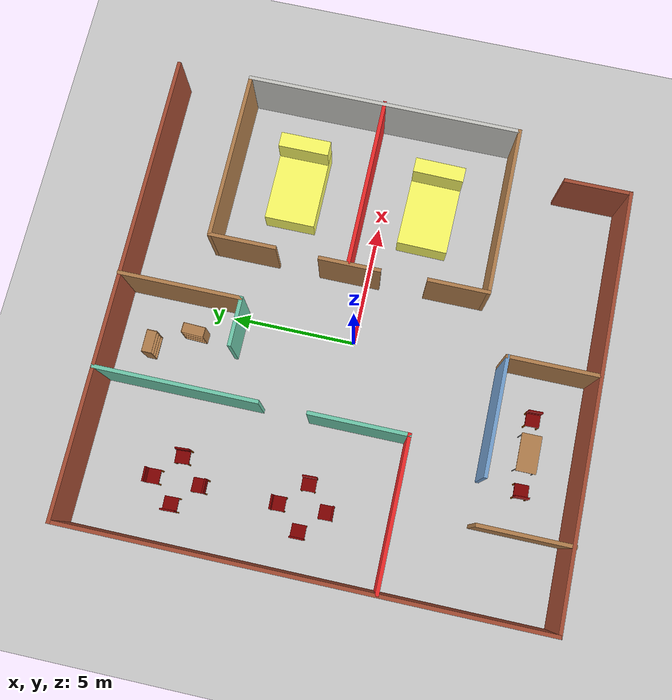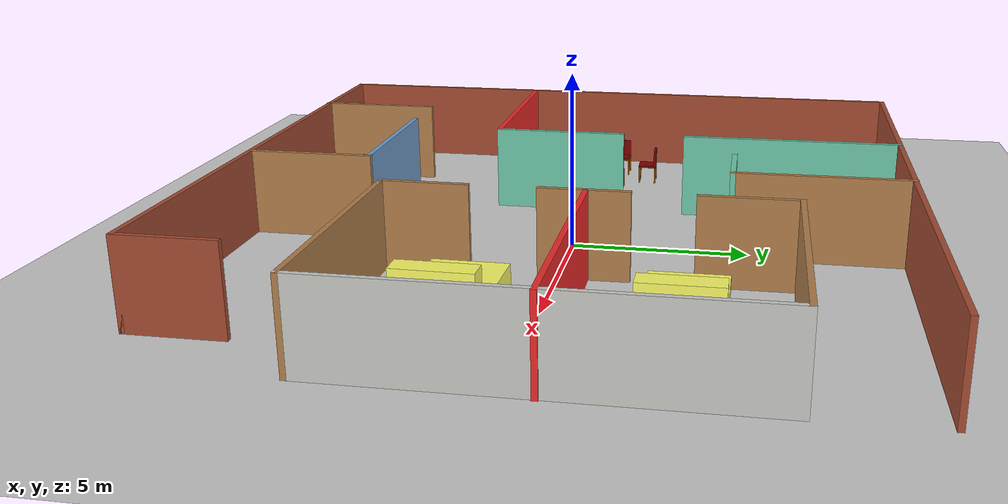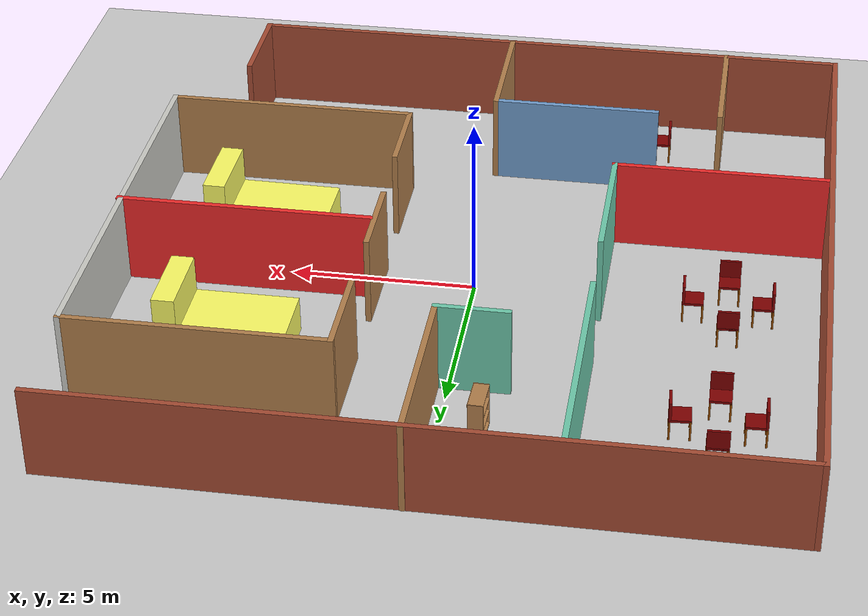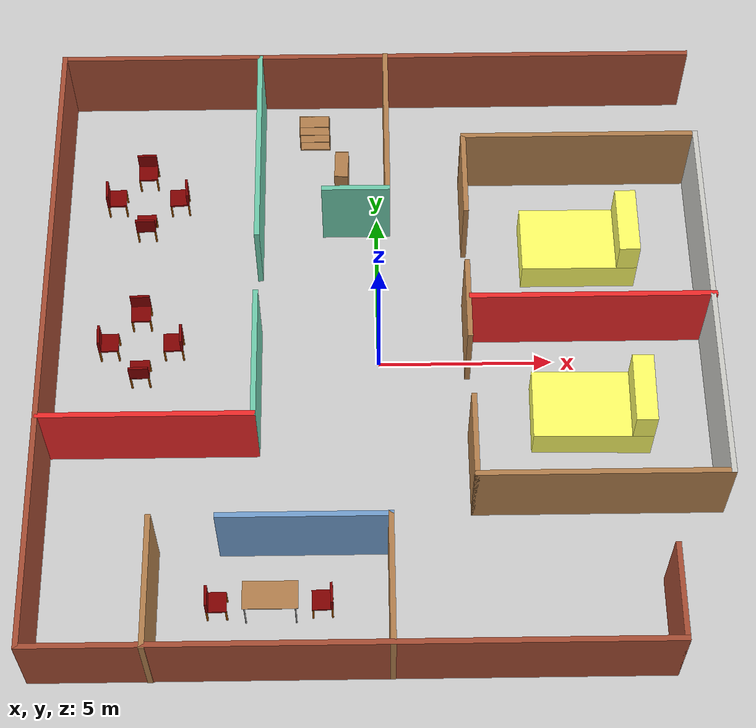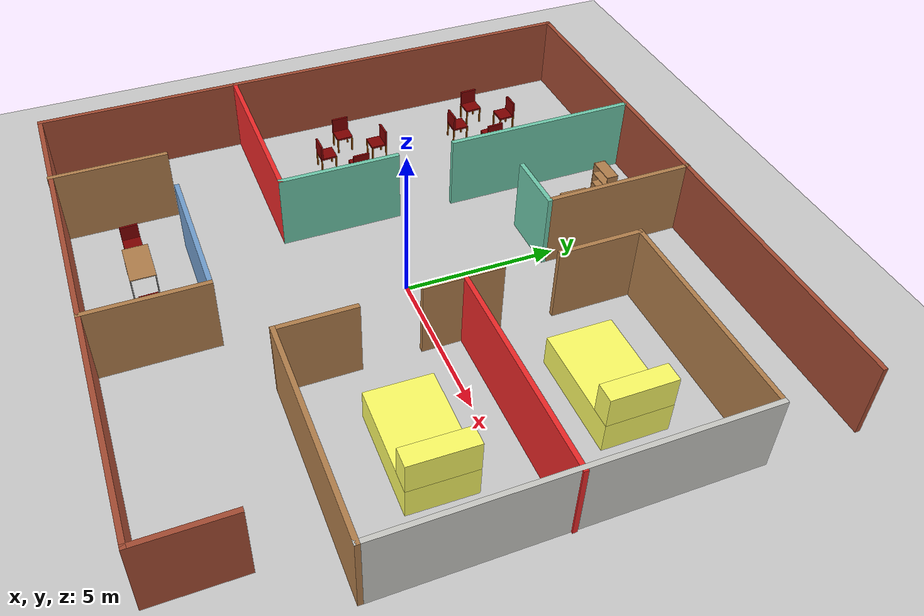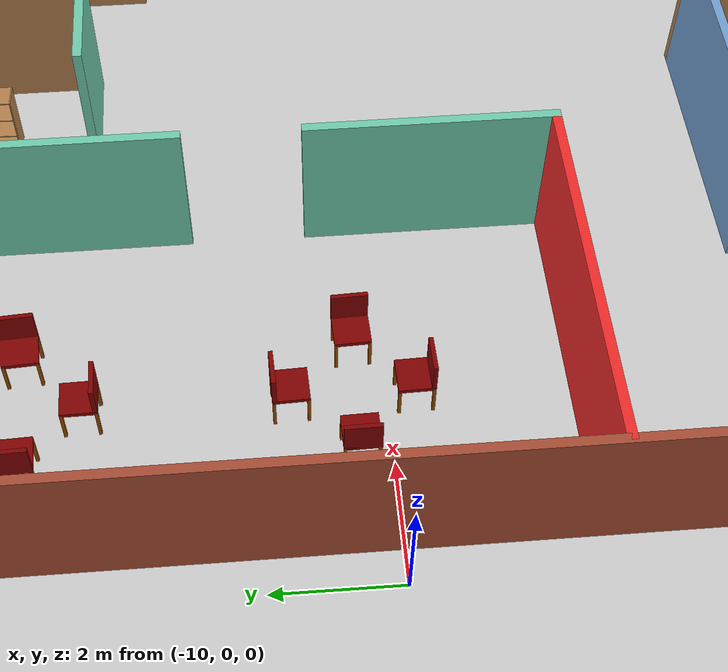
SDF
<sdf version="1.6">
 <world name="default">
  <plugin name="welcome" filename="libwelcome.so"/>
  <light name="sun" type="directional">
   <pose>0 0 10 0 -0 0</pose>
   <diffuse>0.8 0.8 0.8 1</diffuse>
   <specular>0.2 0.2 0.2 1</specular>
   <attenuation>
    <range>1000</range>
    <constant>0.9</constant>
    <linear>0.01</linear>
    <quadratic>0.001</quadratic>
   </attenuation>
   <direction>-0.5 0.1 -0.9</direction>
  </light>
  <model name="ground_plane">
   <static>1</static>
   <link name="link">
    <collision name="collision">
     <geometry><plane><normal>0 0 1</normal><size>100 100</size></plane></geometry>
     <surface>
      <contact><collide_bitmask>65535</collide_bitmask></contact>
      <friction><ode><mu>100</mu><mu2>50</mu2></ode></friction>
     </surface>
    </collision>
    <visual name="visual">
     <cast_shadows>0</cast_shadows>
     <geometry><plane><normal>0 0 1</normal><size>100 100</size></plane></geometry>
     <material>
      <script><uri>file://media/materials/scripts/gazebo.material</uri><name>Gazebo/Grey</name></script>
     </material>
    </visual>
   </link>
  </model>
  <gravity>0 0 -9.8</gravity>
  <magnetic_field>6e-06 2.3e-05 -4.2e-05</magnetic_field>
  <atmosphere type="adiabatic"/>
  <physics name="default_physics" default="0" type="ode">
   <max_step_size>0.001</max_step_size>
   <real_time_factor>1</real_time_factor>
   <real_time_update_rate>1000</real_time_update_rate>
  </physics>
  <scene><ambient>0.4 0.4 0.4 1</ambient><background>0.7 0.7 0.7 1</background><shadows>1</shadows></scene>
  <audio><device>default</device></audio>
  <spherical_coordinates>
   <surface_model>EARTH_WGS84</surface_model>
   <latitude_deg>0</latitude_deg>
   <longitude_deg>0</longitude_deg>
   <elevation>0</elevation>
   <heading_deg>0</heading_deg>
  </spherical_coordinates>
  <model name="building_submit2">
   <pose>0.05273 -0.090017 0 0 -0 0</pose>
   <link name="Wall_13">
    <collision name="Wall_13_Collision">
     <geometry><box><size>19 0.15 2.5</size></box></geometry>
     <pose>0 0 1.25 0 -0 0</pose>
    </collision>
    <visual name="Wall_13_Visual">
     <pose>0 0 1.25 0 -0 0</pose>
     <geometry><box><size>19 0.15 2.5</size></box></geometry>
     <material>
      <script><uri>file://media/materials/scripts/gazebo.material</uri><name>Gazebo/Bricks</name></script>
      <ambient>1 1 1 1</ambient>
     </material>
     <meta><layer>0</layer></meta>
    </visual>
    <pose>-9.41583 0.005472 0 0 -0 -1.5708</pose>
   </link>
   <link name="Wall_15">
    <collision name="Wall_15_Collision">
     <geometry><box><size>18.9075 0.15 2.5</size></box></geometry>
     <pose>0 0 1.25 0 -0 0</pose>
    </collision>
    <visual name="Wall_15_Visual">
     <pose>0 0 1.25 0 -0 0</pose>
     <geometry><box><size>18.9075 0.15 2.5</size></box></geometry>
     <material>
      <script><uri>file://media/materials/scripts/gazebo.material</uri><name>Gazebo/Bricks</name></script>
      <ambient>1 1 1 1</ambient>
     </material>
     <meta><layer>0</layer></meta>
    </visual>
    <pose>-0.037088 9.43047 0 0 -0 0</pose>
   </link>
   <link name="Wall_21">
    <collision name="Wall_21_Collision">
     <geometry><box><size>7 0.15 2.5</size></box></geometry>
     <pose>0 0 1.25 0 -0 0</pose>
    </collision>
    <visual name="Wall_21_Visual">
     <pose>0 0 1.25 0 -0 0</pose>
     <geometry><box><size>7 0.15 2.5</size></box></geometry>
     <material>
      <script><uri>file://media/materials/scripts/gazebo.material</uri><name>Gazebo/Wood</name></script>
      <ambient>1 1 1 1</ambient>
     </material>
     <meta><layer>0</layer></meta>
    </visual>
    <pose>5.94123 6.42349 0 0 -0 3.14159</pose>
   </link>
   <link name="Wall_23">
    <collision name="Wall_23_Collision">
     <geometry><box><size>7 0.15 2.5</size></box></geometry>
     <pose>0 0 1.25 0 -0 0</pose>
    </collision>
    <visual name="Wall_23_Visual">
     <pose>0 0 1.25 0 -0 0</pose>
     <geometry><box><size>7 0.15 2.5</size></box></geometry>
     <material>
      <script><uri>file://media/materials/scripts/gazebo.material</uri><name>Gazebo/Wood</name></script>
      <ambient>1 1 1 1</ambient>
     </material>
     <meta><layer>0</layer></meta>
    </visual>
    <pose>5.94123 -4.67651 0 0 -0 0</pose>
   </link>
   <link name="Wall_25">
    <collision name="Wall_25_Collision">
     <geometry><box><size>7 0.15 2.5</size></box></geometry>
     <pose>0 0 1.25 0 -0 0</pose>
    </collision>
    <visual name="Wall_25_Visual">
     <pose>0 0 1.25 0 -0 0</pose>
     <geometry><box><size>7 0.15 2.5</size></box></geometry>
     <material>
      <script><uri>file://media/materials/scripts/gazebo.material</uri><name>Gazebo/Grey</name></script>
      <ambient>0.937255 0.160784 0.160784 1</ambient>
     </material>
     <meta><layer>0</layer></meta>
    </visual>
    <pose>5.99083 0.872147 0 0 -0 0</pose>
   </link>
   <link name="Wall_27">
    <collision name="Wall_27_Collision">
     <geometry><box><size>11.25 0.15 2.5</size></box></geometry>
     <pose>0 0 1.25 0 -0 0</pose>
    </collision>
    <visual name="Wall_27_Visual">
     <pose>0 0 1.25 0 -0 0</pose>
     <geometry><box><size>11.25 0.15 2.5</size></box></geometry>
     <material>
      <script><uri>file://media/materials/scripts/gazebo.material</uri><name>Gazebo/CeilingTiled</name></script>
      <ambient>1 1 1 1</ambient>
     </material>
     <meta><layer>0</layer></meta>
    </visual>
    <pose>9.36623 0.873493 0 0 -0 -1.5708</pose>
   </link>
   <link name="Wall_36">
    <collision name="Wall_36_Collision">
     <geometry><box><size>17.25 0.15 2.5</size></box></geometry>
     <pose>0 0 1.25 0 -0 0</pose>
    </collision>
    <visual name="Wall_36_Visual">
     <pose>0 0 1.25 0 -0 0</pose>
     <geometry><box><size>17.25 0.15 2.5</size></box></geometry>
     <material>
      <script><uri>file://media/materials/scripts/gazebo.material</uri><name>Gazebo/Bricks</name></script>
      <ambient>1 1 1 1</ambient>
     </material>
     <meta><layer>0</layer></meta>
    </visual>
    <pose>-0.865827 -9.41953 0 0 -0 0</pose>
   </link>
   <link name="Wall_37">
    <collision name="Wall_37_Collision">
     <geometry><box><size>2.75 0.15 2.5</size></box></geometry>
     <pose>0 0 1.25 0 -0 0</pose>
    </collision>
    <visual name="Wall_37_Visual">
     <pose>0 0 1.25 0 -0 0</pose>
     <geometry><box><size>2.75 0.15 2.5</size></box></geometry>
     <material>
      <script><uri>file://media/materials/scripts/gazebo.material</uri><name>Gazebo/Bricks</name></script>
      <ambient>1 1 1 1</ambient>
     </material>
     <meta><layer>0</layer></meta>
    </visual>
    <pose>7.68417 -8.11953 0 0 -0 1.5708</pose>
   </link>
   <link name="Wall_39">
    <collision name="Wall_39_Collision">
     <geometry><box><size>2.75 0.15 2.5</size></box></geometry>
     <pose>0 0 1.25 0 -0 0</pose>
    </collision>
    <visual name="Wall_39_Visual">
     <pose>0 0 1.25 0 -0 0</pose>
     <geometry><box><size>2.75 0.15 2.5</size></box></geometry>
     <material>
      <script><uri>file://media/materials/scripts/gazebo.material</uri><name>Gazebo/Wood</name></script>
      <ambient>1 1 1 1</ambient>
     </material>
     <meta><layer>0</layer></meta>
    </visual>
    <pose>2.51623 5.12349 0 0 -0 -1.5708</pose>
   </link>
   <link name="Wall_41">
    <collision name="Wall_41_Collision">
     <geometry><box><size>2.5 0.15 2.5</size></box></geometry>
     <pose>0 0 1.25 0 -0 0</pose>
    </collision>
    <visual name="Wall_41_Visual">
     <pose>0 0 1.25 0 -0 0</pose>
     <geometry><box><size>2.5 0.15 2.5</size></box></geometry>
     <material>
      <script><uri>file://media/materials/scripts/gazebo.material</uri><name>Gazebo/Wood</name></script>
      <ambient>1 1 1 1</ambient>
     </material>
     <meta><layer>0</layer></meta>
    </visual>
    <pose>2.4831 0.814696 0 0 -0 -1.5708</pose>
   </link>
   <link name="Wall_43">
    <collision name="Wall_43_Collision">
     <geometry><box><size>2.5 0.15 2.5</size></box></geometry>
     <pose>0 0 1.25 0 -0 0</pose>
    </collision>
    <visual name="Wall_43_Visual">
     <pose>0 0 1.25 0 -0 0</pose>
     <geometry><box><size>2.5 0.15 2.5</size></box></geometry>
     <material>
      <script><uri>file://media/materials/scripts/gazebo.material</uri><name>Gazebo/Wood</name></script>
      <ambient>1 1 1 1</ambient>
     </material>
     <meta><layer>0</layer></meta>
    </visual>
    <pose>2.51623 -3.50151 0 0 -0 1.5708</pose>
   </link>
   <link name="Wall_46">
    <collision name="Wall_46_Collision">
     <geometry><box><size>6 0.15 2.5</size></box></geometry>
     <pose>0 0 1.25 0 -0 0</pose>
    </collision>
    <visual name="Wall_46_Visual">
     <pose>0 0 1.25 0 -0 0</pose>
     <geometry><box><size>6 0.15 2.5</size></box></geometry>
     <material>
      <script><uri>file://media/materials/scripts/gazebo.material</uri><name>Gazebo/Grey</name></script>
      <ambient>0.937255 0.160784 0.160784 1</ambient>
     </material>
     <meta><layer>0</layer></meta>
    </visual>
    <pose>-6.43819 -2.78383 0 0 -0 3.14159</pose>
   </link>
   <link name="Wall_48">
    <collision name="Wall_48_Collision">
     <geometry><box><size>3.75 0.15 2.5</size></box></geometry>
     <pose>0 0 1.25 0 -0 0</pose>
    </collision>
    <visual name="Wall_48_Visual">
     <pose>0 0 1.25 0 -0 0</pose>
     <geometry><box><size>3.75 0.15 2.5</size></box></geometry>
     <material>
      <script><uri>file://media/materials/scripts/gazebo.material</uri><name>Gazebo/Wood</name></script>
      <ambient>1 1 1 1</ambient>
     </material>
     <meta><layer>0</layer></meta>
    </visual>
    <pose>-6.2174 -7.64721 0 0 -0 1.5708</pose>
   </link>
   <link name="Wall_50">
    <collision name="Wall_50_Collision">
     <geometry><box><size>3.75 0.15 2.5</size></box></geometry>
     <pose>0 0 1.25 0 -0 0</pose>
    </collision>
    <visual name="Wall_50_Visual">
     <pose>0 0 1.25 0 -0 0</pose>
     <geometry><box><size>3.75 0.15 2.5</size></box></geometry>
     <material>
      <script><uri>file://media/materials/scripts/gazebo.material</uri><name>Gazebo/Wood</name></script>
      <ambient>1 1 1 1</ambient>
     </material>
     <meta><layer>0</layer></meta>
    </visual>
    <pose>0.195698 -7.62076 0 0 -0 -1.5708</pose>
   </link>
   <link name="Wall_52">
    <collision name="Wall_52_Collision">
     <geometry><box><size>4.75 0.15 2.5</size></box></geometry>
     <pose>0 0 1.25 0 -0 0</pose>
    </collision>
    <visual name="Wall_52_Visual">
     <pose>0 0 1.25 0 -0 0</pose>
     <geometry><box><size>4.75 0.15 2.5</size></box></geometry>
     <material>
      <script><uri>file://media/materials/scripts/gazebo.material</uri><name>Gazebo/Grey</name></script>
      <ambient>0.447059 0.623529 0.811765 1</ambient>
     </material>
     <meta><layer>0</layer></meta>
    </visual>
    <pose>-2.1043 -5.82076 0 0 -0 3.14159</pose>
   </link>
   <link name="Wall_55">
    <collision name="Wall_55_Collision">
     <geometry><box><size>5 0.15 2.5</size></box></geometry>
     <pose>0 0 1.25 0 -0 0</pose>
    </collision>
    <visual name="Wall_55_Visual">
     <pose>0 0 1.25 0 -0 0</pose>
     <geometry><box><size>5 0.15 2.5</size></box></geometry>
     <material>
      <script><uri>file://media/materials/scripts/gazebo.material</uri><name>Gazebo/Wood</name></script>
      <ambient>1 1 1 1</ambient>
     </material>
     <meta><layer>0</layer></meta>
    </visual>
    <pose>0.261068 7.02221 0 0 -0 -1.5708</pose>
   </link>
   <link name="Wall_56">
    <collision name="Wall_56_Collision">
     <geometry><box><size>2 0.15 2.5</size></box></geometry>
     <pose>0 0 1.25 0 -0 0</pose>
    </collision>
    <visual name="Wall_56_Visual">
     <pose>0 0 1.25 0 -0 0</pose>
     <geometry><box><size>2 0.15 2.5</size></box></geometry>
     <material>
      <script><uri>file://media/materials/scripts/gazebo.material</uri><name>Gazebo/Grey</name></script>
      <ambient>0.435294 0.796078 0.67451 1</ambient>
     </material>
     <meta><layer>0</layer></meta>
    </visual>
    <pose>-0.663932 4.59721 0 0 -0 3.14159</pose>
   </link>
   <link name="Wall_58">
    <collision name="Wall_58_Collision">
     <geometry><box><size>6.5 0.15 2.5</size></box></geometry>
     <pose>0 0 1.25 0 -0 0</pose>
    </collision>
    <visual name="Wall_58_Visual">
     <pose>0 0 1.25 0 -0 0</pose>
     <geometry><box><size>6.5 0.15 2.5</size></box></geometry>
     <material>
      <script><uri>file://media/materials/scripts/gazebo.material</uri><name>Gazebo/Grey</name></script>
      <ambient>0.435294 0.796078 0.67451 1</ambient>
     </material>
     <meta><layer>0</layer></meta>
    </visual>
    <pose>-3.51319 6.23718 0 0 -0 -1.5708</pose>
   </link>
   <link name="Wall_60">
    <collision name="Wall_60_Collision">
     <geometry><box><size>4 0.15 2.5</size></box></geometry>
     <pose>0 0 1.25 0 -0 0</pose>
    </collision>
    <visual name="Wall_60_Visual">
     <pose>0 0 1.25 0 -0 0</pose>
     <geometry><box><size>4 0.15 2.5</size></box></geometry>
     <material>
      <script><uri>file://media/materials/scripts/gazebo.material</uri><name>Gazebo/Grey</name></script>
      <ambient>0.435294 0.796078 0.67451 1</ambient>
     </material>
     <meta><layer>0</layer></meta>
    </visual>
    <pose>-3.51319 -0.858835 0 0 -0 1.5708</pose>
   </link>
   <static>1</static>
  </model>
  <model name="chair">
   <link name="link_0">
    <inertial>
     <mass>1</mass>
     <inertia>
      <ixx>0.166667</ixx>
      <ixy>0</ixy>
      <ixz>0</ixz>
      <iyy>0.166667</iyy>
      <iyz>0</iyz>
      <izz>0.166667</izz>
     </inertia>
    </inertial>
    <pose>0.000435 0.041667 0.148333 0 -0 0</pose>
    <visual name="visual">
     <geometry><box><size>0.57 0.57 0.07</size></box></geometry>
     <material>
      <lighting>1</lighting>
      <script><uri>file://media/materials/scripts/gazebo.material</uri><name>Gazebo/Grey</name></script>
      <shader type="vertex"><normal_map>__default__</normal_map></shader>
      <ambient>0.502 0 0 1</ambient>
      <diffuse>0.7 0.7 0.7 1</diffuse>
      <specular>0.01 0.01 0.01 1</specular>
      <emissive>0 0 0 1</emissive>
     </material>
    </visual>
    <collision name="collision">
     <geometry><box><size>0.57 0.57 0.07</size></box></geometry>
     <surface>
      <friction>
       <ode><mu>1</mu><mu2>1</mu2><fdir1>0 0 0</fdir1><slip1>0</slip1><slip2>0</slip2></ode>
       <torsional>
        <coefficient>1</coefficient>
        <patch_radius>0</patch_radius>
        <surface_radius>0</surface_radius>
        <use_patch_radius>1</use_patch_radius>
        <ode><slip>0</slip></ode>
       </torsional>
      </friction>
      <bounce><restitution_coefficient>0</restitution_coefficient><threshold>1e+06</threshold></bounce>
      <contact>
       <collide_without_contact>0</collide_without_contact>
       <collide_without_contact_bitmask>1</collide_without_contact_bitmask>
       <collide_bitmask>1</collide_bitmask>
       <ode>
        <soft_cfm>0</soft_cfm>
        <soft_erp>0.2</soft_erp>
        <kp>1e+13</kp>
        <kd>1</kd>
        <max_vel>0.01</max_vel>
        <min_depth>0</min_depth>
       </ode>
       <bullet>
        <split_impulse>1</split_impulse>
        <split_impulse_penetration_threshold>-0.01</split_impulse_penetration_threshold>
        <soft_cfm>0</soft_cfm>
        <soft_erp>0.2</soft_erp>
        <kp>1e+13</kp>
        <kd>1</kd>
       </bullet>
      </contact>
     </surface>
    </collision>
   </link>
   <link name="link_1">
    <inertial>
     <mass>1</mass>
     <inertia>
      <ixx>0.166667</ixx>
      <ixy>0</ixy>
      <ixz>0</ixz>
      <iyy>0.166667</iyy>
      <iyz>0</iyz>
      <izz>0.166667</izz>
     </inertia>
    </inertial>
    <pose>0.000435 -0.208333 0.398333 0 -0 0</pose>
    <visual name="visual">
     <geometry><box><size>0.57 0.07 0.57</size></box></geometry>
     <material>
      <lighting>1</lighting>
      <script><uri>file://media/materials/scripts/gazebo.material</uri><name>Gazebo/Grey</name></script>
      <shader type="vertex"><normal_map>__default__</normal_map></shader>
      <ambient>0.502 0 0 1</ambient>
      <diffuse>0.7 0.7 0.7 1</diffuse>
      <specular>0.01 0.01 0.01 1</specular>
      <emissive>0 0 0 1</emissive>
     </material>
    </visual>
    <collision name="collision">
     <geometry><box><size>0.57 0.07 0.57</size></box></geometry>
     <surface>
      <friction>
       <ode><mu>1</mu><mu2>1</mu2><fdir1>0 0 0</fdir1><slip1>0</slip1><slip2>0</slip2></ode>
       <torsional>
        <coefficient>1</coefficient>
        <patch_radius>0</patch_radius>
        <surface_radius>0</surface_radius>
        <use_patch_radius>1</use_patch_radius>
        <ode><slip>0</slip></ode>
       </torsional>
      </friction>
      <bounce><restitution_coefficient>0</restitution_coefficient><threshold>1e+06</threshold></bounce>
      <contact>
       <collide_without_contact>0</collide_without_contact>
       <collide_without_contact_bitmask>1</collide_without_contact_bitmask>
       <collide_bitmask>1</collide_bitmask>
       <ode>
        <soft_cfm>0</soft_cfm>
        <soft_erp>0.2</soft_erp>
        <kp>1e+13</kp>
        <kd>1</kd>
        <max_vel>0.01</max_vel>
        <min_depth>0</min_depth>
       </ode>
       <bullet>
        <split_impulse>1</split_impulse>
        <split_impulse_penetration_threshold>-0.01</split_impulse_penetration_threshold>
        <soft_cfm>0</soft_cfm>
        <soft_erp>0.2</soft_erp>
        <kp>1e+13</kp>
        <kd>1</kd>
       </bullet>
      </contact>
     </surface>
    </collision>
   </link>
   <link name="link_2">
    <inertial>
     <mass>1</mass>
     <inertia>
      <ixx>0.166667</ixx>
      <ixy>0</ixy>
      <ixz>0</ixz>
      <iyy>0.166667</iyy>
      <iyz>0</iyz>
      <izz>0.166667</izz>
     </inertia>
    </inertial>
    <pose>0.257825 -0.218333 -0.136667 0 -0 0</pose>
    <visual name="visual">
     <geometry><box><size>0.05 0.05 0.57</size></box></geometry>
     <material>
      <lighting>1</lighting>
      <script><uri>file://media/materials/scripts/gazebo.material</uri><name>Gazebo/Grey</name></script>
      <shader type="vertex"><normal_map>__default__</normal_map></shader>
      <ambient>0.588 0.294 0 1</ambient>
      <diffuse>0.7 0.7 0.7 1</diffuse>
      <specular>0.01 0.01 0.01 1</specular>
      <emissive>0 0 0 1</emissive>
     </material>
    </visual>
    <collision name="collision">
     <geometry><box><size>0.05 0.05 0.57</size></box></geometry>
     <surface>
      <friction>
       <ode><mu>1</mu><mu2>1</mu2><fdir1>0 0 0</fdir1><slip1>0</slip1><slip2>0</slip2></ode>
       <torsional>
        <coefficient>1</coefficient>
        <patch_radius>0</patch_radius>
        <surface_radius>0</surface_radius>
        <use_patch_radius>1</use_patch_radius>
        <ode><slip>0</slip></ode>
       </torsional>
      </friction>
      <bounce><restitution_coefficient>0</restitution_coefficient><threshold>1e+06</threshold></bounce>
      <contact>
       <collide_without_contact>0</collide_without_contact>
       <collide_without_contact_bitmask>1</collide_without_contact_bitmask>
       <collide_bitmask>1</collide_bitmask>
       <ode>
        <soft_cfm>0</soft_cfm>
        <soft_erp>0.2</soft_erp>
        <kp>1e+13</kp>
        <kd>1</kd>
        <max_vel>0.01</max_vel>
        <min_depth>0</min_depth>
       </ode>
       <bullet>
        <split_impulse>1</split_impulse>
        <split_impulse_penetration_threshold>-0.01</split_impulse_penetration_threshold>
        <soft_cfm>0</soft_cfm>
        <soft_erp>0.2</soft_erp>
        <kp>1e+13</kp>
        <kd>1</kd>
       </bullet>
      </contact>
     </surface>
    </collision>
   </link>
   <link name="link_2_clone">
    <inertial>
     <mass>1</mass>
     <inertia>
      <ixx>0.166667</ixx>
      <ixy>0</ixy>
      <ixz>0</ixz>
      <iyy>0.166667</iyy>
      <iyz>0</iyz>
      <izz>0.166667</izz>
     </inertia>
    </inertial>
    <pose>-0.259565 -0.218333 -0.136667 0 -0 0</pose>
    <visual name="visual">
     <geometry><box><size>0.05 0.05 0.57</size></box></geometry>
     <material>
      <lighting>1</lighting>
      <script><uri>file://media/materials/scripts/gazebo.material</uri><name>Gazebo/Grey</name></script>
      <shader type="vertex"><normal_map>__default__</normal_map></shader>
      <ambient>0.588 0.294 0 1</ambient>
      <diffuse>0.7 0.7 0.7 1</diffuse>
      <specular>0.01 0.01 0.01 1</specular>
      <emissive>0 0 0 1</emissive>
     </material>
    </visual>
    <collision name="collision">
     <geometry><box><size>0.05 0.05 0.57</size></box></geometry>
     <surface>
      <friction>
       <ode><mu>1</mu><mu2>1</mu2><fdir1>0 0 0</fdir1><slip1>0</slip1><slip2>0</slip2></ode>
       <torsional>
        <coefficient>1</coefficient>
        <patch_radius>0</patch_radius>
        <surface_radius>0</surface_radius>
        <use_patch_radius>1</use_patch_radius>
        <ode><slip>0</slip></ode>
       </torsional>
      </friction>
      <bounce><restitution_coefficient>0</restitution_coefficient><threshold>1e+06</threshold></bounce>
      <contact>
       <collide_without_contact>0</collide_without_contact>
       <collide_without_contact_bitmask>1</collide_without_contact_bitmask>
       <collide_bitmask>1</collide_bitmask>
       <ode>
        <soft_cfm>0</soft_cfm>
        <soft_erp>0.2</soft_erp>
        <kp>1e+13</kp>
        <kd>1</kd>
        <max_vel>0.01</max_vel>
        <min_depth>0</min_depth>
       </ode>
       <bullet>
        <split_impulse>1</split_impulse>
        <split_impulse_penetration_threshold>-0.01</split_impulse_penetration_threshold>
        <soft_cfm>0</soft_cfm>
        <soft_erp>0.2</soft_erp>
        <kp>1e+13</kp>
        <kd>1</kd>
       </bullet>
      </contact>
     </surface>
    </collision>
   </link>
   <link name="link_2_clone_clone">
    <inertial>
     <mass>1</mass>
     <inertia>
      <ixx>0.166667</ixx>
      <ixy>0</ixy>
      <ixz>0</ixz>
      <iyy>0.166667</iyy>
      <iyz>0</iyz>
      <izz>0.166667</izz>
     </inertia>
    </inertial>
    <pose>-0.259565 0.301667 -0.136667 0 -0 0</pose>
    <visual name="visual">
     <geometry><box><size>0.05 0.05 0.57</size></box></geometry>
     <material>
      <lighting>1</lighting>
      <script><uri>file://media/materials/scripts/gazebo.material</uri><name>Gazebo/Grey</name></script>
      <shader type="vertex"><normal_map>__default__</normal_map></shader>
      <ambient>0.588 0.294 0 1</ambient>
      <diffuse>0.7 0.7 0.7 1</diffuse>
      <specular>0.01 0.01 0.01 1</specular>
      <emissive>0 0 0 1</emissive>
     </material>
    </visual>
    <collision name="collision">
     <geometry><box><size>0.05 0.05 0.57</size></box></geometry>
     <surface>
      <friction>
       <ode><mu>1</mu><mu2>1</mu2><fdir1>0 0 0</fdir1><slip1>0</slip1><slip2>0</slip2></ode>
       <torsional>
        <coefficient>1</coefficient>
        <patch_radius>0</patch_radius>
        <surface_radius>0</surface_radius>
        <use_patch_radius>1</use_patch_radius>
        <ode><slip>0</slip></ode>
       </torsional>
      </friction>
      <bounce><restitution_coefficient>0</restitution_coefficient><threshold>1e+06</threshold></bounce>
      <contact>
       <collide_without_contact>0</collide_without_contact>
       <collide_without_contact_bitmask>1</collide_without_contact_bitmask>
       <collide_bitmask>1</collide_bitmask>
       <ode>
        <soft_cfm>0</soft_cfm>
        <soft_erp>0.2</soft_erp>
        <kp>1e+13</kp>
        <kd>1</kd>
        <max_vel>0.01</max_vel>
        <min_depth>0</min_depth>
       </ode>
       <bullet>
        <split_impulse>1</split_impulse>
        <split_impulse_penetration_threshold>-0.01</split_impulse_penetration_threshold>
        <soft_cfm>0</soft_cfm>
        <soft_erp>0.2</soft_erp>
        <kp>1e+13</kp>
        <kd>1</kd>
       </bullet>
      </contact>
     </surface>
    </collision>
   </link>
   <link name="link_2_clone_clone_0">
    <inertial>
     <mass>1</mass>
     <inertia>
      <ixx>0.166667</ixx>
      <ixy>0</ixy>
      <ixz>0</ixz>
      <iyy>0.166667</iyy>
      <iyz>0</iyz>
      <izz>0.166667</izz>
     </inertia>
    </inertial>
    <pose>0.260435 0.301667 -0.136667 0 -0 0</pose>
    <visual name="visual">
     <geometry><box><size>0.05 0.05 0.57</size></box></geometry>
     <material>
      <lighting>1</lighting>
      <script><uri>file://media/materials/scripts/gazebo.material</uri><name>Gazebo/Grey</name></script>
      <shader type="vertex"><normal_map>__default__</normal_map></shader>
      <ambient>0.588 0.294 0 1</ambient>
      <diffuse>0.7 0.7 0.7 1</diffuse>
      <specular>0.01 0.01 0.01 1</specular>
      <emissive>0 0 0 1</emissive>
     </material>
    </visual>
    <collision name="collision">
     <geometry><box><size>0.05 0.05 0.57</size></box></geometry>
     <surface>
      <friction>
       <ode><mu>1</mu><mu2>1</mu2><fdir1>0 0 0</fdir1><slip1>0</slip1><slip2>0</slip2></ode>
       <torsional>
        <coefficient>1</coefficient>
        <patch_radius>0</patch_radius>
        <surface_radius>0</surface_radius>
        <use_patch_radius>1</use_patch_radius>
        <ode><slip>0</slip></ode>
       </torsional>
      </friction>
      <bounce><restitution_coefficient>0</restitution_coefficient><threshold>1e+06</threshold></bounce>
      <contact>
       <collide_without_contact>0</collide_without_contact>
       <collide_without_contact_bitmask>1</collide_without_contact_bitmask>
       <collide_bitmask>1</collide_bitmask>
       <ode>
        <soft_cfm>0</soft_cfm>
        <soft_erp>0.2</soft_erp>
        <kp>1e+13</kp>
        <kd>1</kd>
        <max_vel>0.01</max_vel>
        <min_depth>0</min_depth>
       </ode>
       <bullet>
        <split_impulse>1</split_impulse>
        <split_impulse_penetration_threshold>-0.01</split_impulse_penetration_threshold>
        <soft_cfm>0</soft_cfm>
        <soft_erp>0.2</soft_erp>
        <kp>1e+13</kp>
        <kd>1</kd>
       </bullet>
      </contact>
     </surface>
    </collision>
   </link>
   <joint name="link_0_JOINT_0" type="fixed">
    <parent>link_0</parent>
    <child>link_1</child>
    <physics>
     <ode><limit><cfm>0</cfm><erp>0.2</erp></limit><suspension><cfm>0</cfm><erp>0.2</erp></suspension></ode>
    </physics>
   </joint>
   <joint name="link_0_JOINT_4" type="fixed">
    <parent>link_0</parent>
    <child>link_2</child>
    <physics>
     <ode><limit><cfm>0</cfm><erp>0.2</erp></limit><suspension><cfm>0</cfm><erp>0.2</erp></suspension></ode>
    </physics>
   </joint>
   <joint name="link_0_JOINT_5" type="fixed">
    <parent>link_0</parent>
    <child>link_2_clone</child>
    <physics>
     <ode><limit><cfm>0</cfm><erp>0.2</erp></limit><suspension><cfm>0</cfm><erp>0.2</erp></suspension></ode>
    </physics>
   </joint>
   <joint name="link_0_JOINT_6" type="fixed">
    <parent>link_0</parent>
    <child>link_2_clone_clone_0</child>
    <physics>
     <ode><limit><cfm>0</cfm><erp>0.2</erp></limit><suspension><cfm>0</cfm><erp>0.2</erp></suspension></ode>
    </physics>
   </joint>
   <joint name="link_0_JOINT_7" type="fixed">
    <parent>link_0</parent>
    <child>link_2_clone_clone</child>
    <physics>
     <ode><limit><cfm>0</cfm><erp>0.2</erp></limit><suspension><cfm>0</cfm><erp>0.2</erp></suspension></ode>
    </physics>
   </joint>
   <static>0</static>
   <pose>-6.87287 4.57288 0.421667 1e-06 2e-06 0.01631</pose>
  </model>
  <model name="chair_0">
   <link name="link_0">
    <inertial>
     <mass>1</mass>
     <inertia>
      <ixx>0.166667</ixx>
      <ixy>0</ixy>
      <ixz>0</ixz>
      <iyy>0.166667</iyy>
      <iyz>0</iyz>
      <izz>0.166667</izz>
     </inertia>
    </inertial>
    <pose>0.000435 0.041667 0.148333 0 -0 0</pose>
    <visual name="visual">
     <geometry><box><size>0.57 0.57 0.07</size></box></geometry>
     <material>
      <lighting>1</lighting>
      <script><uri>file://media/materials/scripts/gazebo.material</uri><name>Gazebo/Grey</name></script>
      <shader type="vertex"><normal_map>__default__</normal_map></shader>
      <ambient>0.502 0 0 1</ambient>
      <diffuse>0.7 0.7 0.7 1</diffuse>
      <specular>0.01 0.01 0.01 1</specular>
      <emissive>0 0 0 1</emissive>
     </material>
    </visual>
    <collision name="collision">
     <geometry><box><size>0.57 0.57 0.07</size></box></geometry>
     <surface>
      <friction>
       <ode><mu>1</mu><mu2>1</mu2><fdir1>0 0 0</fdir1><slip1>0</slip1><slip2>0</slip2></ode>
       <torsional>
        <coefficient>1</coefficient>
        <patch_radius>0</patch_radius>
        <surface_radius>0</surface_radius>
        <use_patch_radius>1</use_patch_radius>
        <ode><slip>0</slip></ode>
       </torsional>
      </friction>
      <bounce><restitution_coefficient>0</restitution_coefficient><threshold>1e+06</threshold></bounce>
      <contact>
       <collide_without_contact>0</collide_without_contact>
       <collide_without_contact_bitmask>1</collide_without_contact_bitmask>
       <collide_bitmask>1</collide_bitmask>
       <ode>
        <soft_cfm>0</soft_cfm>
        <soft_erp>0.2</soft_erp>
        <kp>1e+13</kp>
        <kd>1</kd>
        <max_vel>0.01</max_vel>
        <min_depth>0</min_depth>
       </ode>
       <bullet>
        <split_impulse>1</split_impulse>
        <split_impulse_penetration_threshold>-0.01</split_impulse_penetration_threshold>
        <soft_cfm>0</soft_cfm>
        <soft_erp>0.2</soft_erp>
        <kp>1e+13</kp>
        <kd>1</kd>
       </bullet>
      </contact>
     </surface>
    </collision>
   </link>
   <link name="link_1">
    <inertial>
     <mass>1</mass>
     <inertia>
      <ixx>0.166667</ixx>
      <ixy>0</ixy>
      <ixz>0</ixz>
      <iyy>0.166667</iyy>
      <iyz>0</iyz>
      <izz>0.166667</izz>
     </inertia>
    </inertial>
    <pose>0.000435 -0.208333 0.398333 0 -0 0</pose>
    <visual name="visual">
     <geometry><box><size>0.57 0.07 0.57</size></box></geometry>
     <material>
      <lighting>1</lighting>
      <script><uri>file://media/materials/scripts/gazebo.material</uri><name>Gazebo/Grey</name></script>
      <shader type="vertex"><normal_map>__default__</normal_map></shader>
      <ambient>0.502 0 0 1</ambient>
      <diffuse>0.7 0.7 0.7 1</diffuse>
      <specular>0.01 0.01 0.01 1</specular>
      <emissive>0 0 0 1</emissive>
     </material>
    </visual>
    <collision name="collision">
     <geometry><box><size>0.57 0.07 0.57</size></box></geometry>
     <surface>
      <friction>
       <ode><mu>1</mu><mu2>1</mu2><fdir1>0 0 0</fdir1><slip1>0</slip1><slip2>0</slip2></ode>
       <torsional>
        <coefficient>1</coefficient>
        <patch_radius>0</patch_radius>
        <surface_radius>0</surface_radius>
        <use_patch_radius>1</use_patch_radius>
        <ode><slip>0</slip></ode>
       </torsional>
      </friction>
      <bounce><restitution_coefficient>0</restitution_coefficient><threshold>1e+06</threshold></bounce>
      <contact>
       <collide_without_contact>0</collide_without_contact>
       <collide_without_contact_bitmask>1</collide_without_contact_bitmask>
       <collide_bitmask>1</collide_bitmask>
       <ode>
        <soft_cfm>0</soft_cfm>
        <soft_erp>0.2</soft_erp>
        <kp>1e+13</kp>
        <kd>1</kd>
        <max_vel>0.01</max_vel>
        <min_depth>0</min_depth>
       </ode>
       <bullet>
        <split_impulse>1</split_impulse>
        <split_impulse_penetration_threshold>-0.01</split_impulse_penetration_threshold>
        <soft_cfm>0</soft_cfm>
        <soft_erp>0.2</soft_erp>
        <kp>1e+13</kp>
        <kd>1</kd>
       </bullet>
      </contact>
     </surface>
    </collision>
   </link>
   <link name="link_2">
    <inertial>
     <mass>1</mass>
     <inertia>
      <ixx>0.166667</ixx>
      <ixy>0</ixy>
      <ixz>0</ixz>
      <iyy>0.166667</iyy>
      <iyz>0</iyz>
      <izz>0.166667</izz>
     </inertia>
    </inertial>
    <pose>0.257825 -0.218333 -0.136667 0 -0 0</pose>
    <visual name="visual">
     <geometry><box><size>0.05 0.05 0.57</size></box></geometry>
     <material>
      <lighting>1</lighting>
      <script><uri>file://media/materials/scripts/gazebo.material</uri><name>Gazebo/Grey</name></script>
      <shader type="vertex"><normal_map>__default__</normal_map></shader>
      <ambient>0.588 0.294 0 1</ambient>
      <diffuse>0.7 0.7 0.7 1</diffuse>
      <specular>0.01 0.01 0.01 1</specular>
      <emissive>0 0 0 1</emissive>
     </material>
    </visual>
    <collision name="collision">
     <geometry><box><size>0.05 0.05 0.57</size></box></geometry>
     <surface>
      <friction>
       <ode><mu>1</mu><mu2>1</mu2><fdir1>0 0 0</fdir1><slip1>0</slip1><slip2>0</slip2></ode>
       <torsional>
        <coefficient>1</coefficient>
        <patch_radius>0</patch_radius>
        <surface_radius>0</surface_radius>
        <use_patch_radius>1</use_patch_radius>
        <ode><slip>0</slip></ode>
       </torsional>
      </friction>
      <bounce><restitution_coefficient>0</restitution_coefficient><threshold>1e+06</threshold></bounce>
      <contact>
       <collide_without_contact>0</collide_without_contact>
       <collide_without_contact_bitmask>1</collide_without_contact_bitmask>
       <collide_bitmask>1</collide_bitmask>
       <ode>
        <soft_cfm>0</soft_cfm>
        <soft_erp>0.2</soft_erp>
        <kp>1e+13</kp>
        <kd>1</kd>
        <max_vel>0.01</max_vel>
        <min_depth>0</min_depth>
       </ode>
       <bullet>
        <split_impulse>1</split_impulse>
        <split_impulse_penetration_threshold>-0.01</split_impulse_penetration_threshold>
        <soft_cfm>0</soft_cfm>
        <soft_erp>0.2</soft_erp>
        <kp>1e+13</kp>
        <kd>1</kd>
       </bullet>
      </contact>
     </surface>
    </collision>
   </link>
   <link name="link_2_clone">
    <inertial>
     <mass>1</mass>
     <inertia>
      <ixx>0.166667</ixx>
      <ixy>0</ixy>
      <ixz>0</ixz>
      <iyy>0.166667</iyy>
      <iyz>0</iyz>
      <izz>0.166667</izz>
     </inertia>
    </inertial>
    <pose>-0.259565 -0.218333 -0.136667 0 -0 0</pose>
    <visual name="visual">
     <geometry><box><size>0.05 0.05 0.57</size></box></geometry>
     <material>
      <lighting>1</lighting>
      <script><uri>file://media/materials/scripts/gazebo.material</uri><name>Gazebo/Grey</name></script>
      <shader type="vertex"><normal_map>__default__</normal_map></shader>
      <ambient>0.588 0.294 0 1</ambient>
      <diffuse>0.7 0.7 0.7 1</diffuse>
      <specular>0.01 0.01 0.01 1</specular>
      <emissive>0 0 0 1</emissive>
     </material>
    </visual>
    <collision name="collision">
     <geometry><box><size>0.05 0.05 0.57</size></box></geometry>
     <surface>
      <friction>
       <ode><mu>1</mu><mu2>1</mu2><fdir1>0 0 0</fdir1><slip1>0</slip1><slip2>0</slip2></ode>
       <torsional>
        <coefficient>1</coefficient>
        <patch_radius>0</patch_radius>
        <surface_radius>0</surface_radius>
        <use_patch_radius>1</use_patch_radius>
        <ode><slip>0</slip></ode>
       </torsional>
      </friction>
      <bounce><restitution_coefficient>0</restitution_coefficient><threshold>1e+06</threshold></bounce>
      <contact>
       <collide_without_contact>0</collide_without_contact>
       <collide_without_contact_bitmask>1</collide_without_contact_bitmask>
       <collide_bitmask>1</collide_bitmask>
       <ode>
        <soft_cfm>0</soft_cfm>
        <soft_erp>0.2</soft_erp>
        <kp>1e+13</kp>
        <kd>1</kd>
        <max_vel>0.01</max_vel>
        <min_depth>0</min_depth>
       </ode>
       <bullet>
        <split_impulse>1</split_impulse>
        <split_impulse_penetration_threshold>-0.01</split_impulse_penetration_threshold>
        <soft_cfm>0</soft_cfm>
        <soft_erp>0.2</soft_erp>
        <kp>1e+13</kp>
        <kd>1</kd>
       </bullet>
      </contact>
     </surface>
    </collision>
   </link>
   <link name="link_2_clone_clone">
    <inertial>
     <mass>1</mass>
     <inertia>
      <ixx>0.166667</ixx>
      <ixy>0</ixy>
      <ixz>0</ixz>
      <iyy>0.166667</iyy>
      <iyz>0</iyz>
      <izz>0.166667</izz>
     </inertia>
    </inertial>
    <pose>-0.259565 0.301667 -0.136667 0 -0 0</pose>
    <visual name="visual">
     <geometry><box><size>0.05 0.05 0.57</size></box></geometry>
     <material>
      <lighting>1</lighting>
      <script><uri>file://media/materials/scripts/gazebo.material</uri><name>Gazebo/Grey</name></script>
      <shader type="vertex"><normal_map>__default__</normal_map></shader>
      <ambient>0.588 0.294 0 1</ambient>
      <diffuse>0.7 0.7 0.7 1</diffuse>
      <specular>0.01 0.01 0.01 1</specular>
      <emissive>0 0 0 1</emissive>
     </material>
    </visual>
    <collision name="collision">
     <geometry><box><size>0.05 0.05 0.57</size></box></geometry>
     <surface>
      <friction>
       <ode><mu>1</mu><mu2>1</mu2><fdir1>0 0 0</fdir1><slip1>0</slip1><slip2>0</slip2></ode>
       <torsional>
        <coefficient>1</coefficient>
        <patch_radius>0</patch_radius>
        <surface_radius>0</surface_radius>
        <use_patch_radius>1</use_patch_radius>
        <ode><slip>0</slip></ode>
       </torsional>
      </friction>
      <bounce><restitution_coefficient>0</restitution_coefficient><threshold>1e+06</threshold></bounce>
      <contact>
       <collide_without_contact>0</collide_without_contact>
       <collide_without_contact_bitmask>1</collide_without_contact_bitmask>
       <collide_bitmask>1</collide_bitmask>
       <ode>
        <soft_cfm>0</soft_cfm>
        <soft_erp>0.2</soft_erp>
        <kp>1e+13</kp>
        <kd>1</kd>
        <max_vel>0.01</max_vel>
        <min_depth>0</min_depth>
       </ode>
       <bullet>
        <split_impulse>1</split_impulse>
        <split_impulse_penetration_threshold>-0.01</split_impulse_penetration_threshold>
        <soft_cfm>0</soft_cfm>
        <soft_erp>0.2</soft_erp>
        <kp>1e+13</kp>
        <kd>1</kd>
       </bullet>
      </contact>
     </surface>
    </collision>
   </link>
   <link name="link_2_clone_clone_0">
    <inertial>
     <mass>1</mass>
     <inertia>
      <ixx>0.166667</ixx>
      <ixy>0</ixy>
      <ixz>0</ixz>
      <iyy>0.166667</iyy>
      <iyz>0</iyz>
      <izz>0.166667</izz>
     </inertia>
    </inertial>
    <pose>0.260435 0.301667 -0.136667 0 -0 0</pose>
    <visual name="visual">
     <geometry><box><size>0.05 0.05 0.57</size></box></geometry>
     <material>
      <lighting>1</lighting>
      <script><uri>file://media/materials/scripts/gazebo.material</uri><name>Gazebo/Grey</name></script>
      <shader type="vertex"><normal_map>__default__</normal_map></shader>
      <ambient>0.588 0.294 0 1</ambient>
      <diffuse>0.7 0.7 0.7 1</diffuse>
      <specular>0.01 0.01 0.01 1</specular>
      <emissive>0 0 0 1</emissive>
     </material>
    </visual>
    <collision name="collision">
     <geometry><box><size>0.05 0.05 0.57</size></box></geometry>
     <surface>
      <friction>
       <ode><mu>1</mu><mu2>1</mu2><fdir1>0 0 0</fdir1><slip1>0</slip1><slip2>0</slip2></ode>
       <torsional>
        <coefficient>1</coefficient>
        <patch_radius>0</patch_radius>
        <surface_radius>0</surface_radius>
        <use_patch_radius>1</use_patch_radius>
        <ode><slip>0</slip></ode>
       </torsional>
      </friction>
      <bounce><restitution_coefficient>0</restitution_coefficient><threshold>1e+06</threshold></bounce>
      <contact>
       <collide_without_contact>0</collide_without_contact>
       <collide_without_contact_bitmask>1</collide_without_contact_bitmask>
       <collide_bitmask>1</collide_bitmask>
       <ode>
        <soft_cfm>0</soft_cfm>
        <soft_erp>0.2</soft_erp>
        <kp>1e+13</kp>
        <kd>1</kd>
        <max_vel>0.01</max_vel>
        <min_depth>0</min_depth>
       </ode>
       <bullet>
        <split_impulse>1</split_impulse>
        <split_impulse_penetration_threshold>-0.01</split_impulse_penetration_threshold>
        <soft_cfm>0</soft_cfm>
        <soft_erp>0.2</soft_erp>
        <kp>1e+13</kp>
        <kd>1</kd>
       </bullet>
      </contact>
     </surface>
    </collision>
   </link>
   <joint name="link_0_JOINT_0" type="fixed">
    <parent>link_0</parent>
    <child>link_1</child>
    <physics>
     <ode><limit><cfm>0</cfm><erp>0.2</erp></limit><suspension><cfm>0</cfm><erp>0.2</erp></suspension></ode>
    </physics>
   </joint>
   <joint name="link_0_JOINT_4" type="fixed">
    <parent>link_0</parent>
    <child>link_2</child>
    <physics>
     <ode><limit><cfm>0</cfm><erp>0.2</erp></limit><suspension><cfm>0</cfm><erp>0.2</erp></suspension></ode>
    </physics>
   </joint>
   <joint name="link_0_JOINT_5" type="fixed">
    <parent>link_0</parent>
    <child>link_2_clone</child>
    <physics>
     <ode><limit><cfm>0</cfm><erp>0.2</erp></limit><suspension><cfm>0</cfm><erp>0.2</erp></suspension></ode>
    </physics>
   </joint>
   <joint name="link_0_JOINT_6" type="fixed">
    <parent>link_0</parent>
    <child>link_2_clone_clone_0</child>
    <physics>
     <ode><limit><cfm>0</cfm><erp>0.2</erp></limit><suspension><cfm>0</cfm><erp>0.2</erp></suspension></ode>
    </physics>
   </joint>
   <joint name="link_0_JOINT_7" type="fixed">
    <parent>link_0</parent>
    <child>link_2_clone_clone</child>
    <physics>
     <ode><limit><cfm>0</cfm><erp>0.2</erp></limit><suspension><cfm>0</cfm><erp>0.2</erp></suspension></ode>
    </physics>
   </joint>
   <static>0</static>
   <pose>-7.8394 5.52494 0.421667 -1e-06 -1e-06 -1.53299</pose>
  </model>
  <model name="chair_1">
   <link name="link_0">
    <inertial>
     <mass>1</mass>
     <inertia>
      <ixx>0.166667</ixx>
      <ixy>0</ixy>
      <ixz>0</ixz>
      <iyy>0.166667</iyy>
      <iyz>0</iyz>
      <izz>0.166667</izz>
     </inertia>
    </inertial>
    <pose>0.000435 0.041667 0.148333 0 -0 0</pose>
    <visual name="visual">
     <geometry><box><size>0.57 0.57 0.07</size></box></geometry>
     <material>
      <lighting>1</lighting>
      <script><uri>file://media/materials/scripts/gazebo.material</uri><name>Gazebo/Grey</name></script>
      <shader type="vertex"><normal_map>__default__</normal_map></shader>
      <ambient>0.502 0 0 1</ambient>
      <diffuse>0.7 0.7 0.7 1</diffuse>
      <specular>0.01 0.01 0.01 1</specular>
      <emissive>0 0 0 1</emissive>
     </material>
    </visual>
    <collision name="collision">
     <geometry><box><size>0.57 0.57 0.07</size></box></geometry>
     <surface>
      <friction>
       <ode><mu>1</mu><mu2>1</mu2><fdir1>0 0 0</fdir1><slip1>0</slip1><slip2>0</slip2></ode>
       <torsional>
        <coefficient>1</coefficient>
        <patch_radius>0</patch_radius>
        <surface_radius>0</surface_radius>
        <use_patch_radius>1</use_patch_radius>
        <ode><slip>0</slip></ode>
       </torsional>
      </friction>
      <bounce><restitution_coefficient>0</restitution_coefficient><threshold>1e+06</threshold></bounce>
      <contact>
       <collide_without_contact>0</collide_without_contact>
       <collide_without_contact_bitmask>1</collide_without_contact_bitmask>
       <collide_bitmask>1</collide_bitmask>
       <ode>
        <soft_cfm>0</soft_cfm>
        <soft_erp>0.2</soft_erp>
        <kp>1e+13</kp>
        <kd>1</kd>
        <max_vel>0.01</max_vel>
        <min_depth>0</min_depth>
       </ode>
       <bullet>
        <split_impulse>1</split_impulse>
        <split_impulse_penetration_threshold>-0.01</split_impulse_penetration_threshold>
        <soft_cfm>0</soft_cfm>
        <soft_erp>0.2</soft_erp>
        <kp>1e+13</kp>
        <kd>1</kd>
       </bullet>
      </contact>
     </surface>
    </collision>
   </link>
   <link name="link_1">
    <inertial>
     <mass>1</mass>
     <inertia>
      <ixx>0.166667</ixx>
      <ixy>0</ixy>
      <ixz>0</ixz>
      <iyy>0.166667</iyy>
      <iyz>0</iyz>
      <izz>0.166667</izz>
     </inertia>
    </inertial>
    <pose>0.000435 -0.208333 0.398333 0 -0 0</pose>
    <visual name="visual">
     <geometry><box><size>0.57 0.07 0.57</size></box></geometry>
     <material>
      <lighting>1</lighting>
      <script><uri>file://media/materials/scripts/gazebo.material</uri><name>Gazebo/Grey</name></script>
      <shader type="vertex"><normal_map>__default__</normal_map></shader>
      <ambient>0.502 0 0 1</ambient>
      <diffuse>0.7 0.7 0.7 1</diffuse>
      <specular>0.01 0.01 0.01 1</specular>
      <emissive>0 0 0 1</emissive>
     </material>
    </visual>
    <collision name="collision">
     <geometry><box><size>0.57 0.07 0.57</size></box></geometry>
     <surface>
      <friction>
       <ode><mu>1</mu><mu2>1</mu2><fdir1>0 0 0</fdir1><slip1>0</slip1><slip2>0</slip2></ode>
       <torsional>
        <coefficient>1</coefficient>
        <patch_radius>0</patch_radius>
        <surface_radius>0</surface_radius>
        <use_patch_radius>1</use_patch_radius>
        <ode><slip>0</slip></ode>
       </torsional>
      </friction>
      <bounce><restitution_coefficient>0</restitution_coefficient><threshold>1e+06</threshold></bounce>
      <contact>
       <collide_without_contact>0</collide_without_contact>
       <collide_without_contact_bitmask>1</collide_without_contact_bitmask>
       <collide_bitmask>1</collide_bitmask>
       <ode>
        <soft_cfm>0</soft_cfm>
        <soft_erp>0.2</soft_erp>
        <kp>1e+13</kp>
        <kd>1</kd>
        <max_vel>0.01</max_vel>
        <min_depth>0</min_depth>
       </ode>
       <bullet>
        <split_impulse>1</split_impulse>
        <split_impulse_penetration_threshold>-0.01</split_impulse_penetration_threshold>
        <soft_cfm>0</soft_cfm>
        <soft_erp>0.2</soft_erp>
        <kp>1e+13</kp>
        <kd>1</kd>
       </bullet>
      </contact>
     </surface>
    </collision>
   </link>
   <link name="link_2">
    <inertial>
     <mass>1</mass>
     <inertia>
      <ixx>0.166667</ixx>
      <ixy>0</ixy>
      <ixz>0</ixz>
      <iyy>0.166667</iyy>
      <iyz>0</iyz>
      <izz>0.166667</izz>
     </inertia>
    </inertial>
    <pose>0.257825 -0.218333 -0.136667 0 -0 0</pose>
    <visual name="visual">
     <geometry><box><size>0.05 0.05 0.57</size></box></geometry>
     <material>
      <lighting>1</lighting>
      <script><uri>file://media/materials/scripts/gazebo.material</uri><name>Gazebo/Grey</name></script>
      <shader type="vertex"><normal_map>__default__</normal_map></shader>
      <ambient>0.588 0.294 0 1</ambient>
      <diffuse>0.7 0.7 0.7 1</diffuse>
      <specular>0.01 0.01 0.01 1</specular>
      <emissive>0 0 0 1</emissive>
     </material>
    </visual>
    <collision name="collision">
     <geometry><box><size>0.05 0.05 0.57</size></box></geometry>
     <surface>
      <friction>
       <ode><mu>1</mu><mu2>1</mu2><fdir1>0 0 0</fdir1><slip1>0</slip1><slip2>0</slip2></ode>
       <torsional>
        <coefficient>1</coefficient>
        <patch_radius>0</patch_radius>
        <surface_radius>0</surface_radius>
        <use_patch_radius>1</use_patch_radius>
        <ode><slip>0</slip></ode>
       </torsional>
      </friction>
      <bounce><restitution_coefficient>0</restitution_coefficient><threshold>1e+06</threshold></bounce>
      <contact>
       <collide_without_contact>0</collide_without_contact>
       <collide_without_contact_bitmask>1</collide_without_contact_bitmask>
       <collide_bitmask>1</collide_bitmask>
       <ode>
        <soft_cfm>0</soft_cfm>
        <soft_erp>0.2</soft_erp>
        <kp>1e+13</kp>
        <kd>1</kd>
        <max_vel>0.01</max_vel>
        <min_depth>0</min_depth>
       </ode>
       <bullet>
        <split_impulse>1</split_impulse>
        <split_impulse_penetration_threshold>-0.01</split_impulse_penetration_threshold>
        <soft_cfm>0</soft_cfm>
        <soft_erp>0.2</soft_erp>
        <kp>1e+13</kp>
        <kd>1</kd>
       </bullet>
      </contact>
     </surface>
    </collision>
   </link>
   <link name="link_2_clone">
    <inertial>
     <mass>1</mass>
     <inertia>
      <ixx>0.166667</ixx>
      <ixy>0</ixy>
      <ixz>0</ixz>
      <iyy>0.166667</iyy>
      <iyz>0</iyz>
      <izz>0.166667</izz>
     </inertia>
    </inertial>
    <pose>-0.259565 -0.218333 -0.136667 0 -0 0</pose>
    <visual name="visual">
     <geometry><box><size>0.05 0.05 0.57</size></box></geometry>
     <material>
      <lighting>1</lighting>
      <script><uri>file://media/materials/scripts/gazebo.material</uri><name>Gazebo/Grey</name></script>
      <shader type="vertex"><normal_map>__default__</normal_map></shader>
      <ambient>0.588 0.294 0 1</ambient>
      <diffuse>0.7 0.7 0.7 1</diffuse>
      <specular>0.01 0.01 0.01 1</specular>
      <emissive>0 0 0 1</emissive>
     </material>
    </visual>
    <collision name="collision">
     <geometry><box><size>0.05 0.05 0.57</size></box></geometry>
     <surface>
      <friction>
       <ode><mu>1</mu><mu2>1</mu2><fdir1>0 0 0</fdir1><slip1>0</slip1><slip2>0</slip2></ode>
       <torsional>
        <coefficient>1</coefficient>
        <patch_radius>0</patch_radius>
        <surface_radius>0</surface_radius>
        <use_patch_radius>1</use_patch_radius>
        <ode><slip>0</slip></ode>
       </torsional>
      </friction>
      <bounce><restitution_coefficient>0</restitution_coefficient><threshold>1e+06</threshold></bounce>
      <contact>
       <collide_without_contact>0</collide_without_contact>
       <collide_without_contact_bitmask>1</collide_without_contact_bitmask>
       <collide_bitmask>1</collide_bitmask>
       <ode>
        <soft_cfm>0</soft_cfm>
        <soft_erp>0.2</soft_erp>
        <kp>1e+13</kp>
        <kd>1</kd>
        <max_vel>0.01</max_vel>
        <min_depth>0</min_depth>
       </ode>
       <bullet>
        <split_impulse>1</split_impulse>
        <split_impulse_penetration_threshold>-0.01</split_impulse_penetration_threshold>
        <soft_cfm>0</soft_cfm>
        <soft_erp>0.2</soft_erp>
        <kp>1e+13</kp>
        <kd>1</kd>
       </bullet>
      </contact>
     </surface>
    </collision>
   </link>
   <link name="link_2_clone_clone">
    <inertial>
     <mass>1</mass>
     <inertia>
      <ixx>0.166667</ixx>
      <ixy>0</ixy>
      <ixz>0</ixz>
      <iyy>0.166667</iyy>
      <iyz>0</iyz>
      <izz>0.166667</izz>
     </inertia>
    </inertial>
    <pose>-0.259565 0.301667 -0.136667 0 -0 0</pose>
    <visual name="visual">
     <geometry><box><size>0.05 0.05 0.57</size></box></geometry>
     <material>
      <lighting>1</lighting>
      <script><uri>file://media/materials/scripts/gazebo.material</uri><name>Gazebo/Grey</name></script>
      <shader type="vertex"><normal_map>__default__</normal_map></shader>
      <ambient>0.588 0.294 0 1</ambient>
      <diffuse>0.7 0.7 0.7 1</diffuse>
      <specular>0.01 0.01 0.01 1</specular>
      <emissive>0 0 0 1</emissive>
     </material>
    </visual>
    <collision name="collision">
     <geometry><box><size>0.05 0.05 0.57</size></box></geometry>
     <surface>
      <friction>
       <ode><mu>1</mu><mu2>1</mu2><fdir1>0 0 0</fdir1><slip1>0</slip1><slip2>0</slip2></ode>
       <torsional>
        <coefficient>1</coefficient>
        <patch_radius>0</patch_radius>
        <surface_radius>0</surface_radius>
        <use_patch_radius>1</use_patch_radius>
        <ode><slip>0</slip></ode>
       </torsional>
      </friction>
      <bounce><restitution_coefficient>0</restitution_coefficient><threshold>1e+06</threshold></bounce>
      <contact>
       <collide_without_contact>0</collide_without_contact>
       <collide_without_contact_bitmask>1</collide_without_contact_bitmask>
       <collide_bitmask>1</collide_bitmask>
       <ode>
        <soft_cfm>0</soft_cfm>
        <soft_erp>0.2</soft_erp>
        <kp>1e+13</kp>
        <kd>1</kd>
        <max_vel>0.01</max_vel>
        <min_depth>0</min_depth>
       </ode>
       <bullet>
        <split_impulse>1</split_impulse>
        <split_impulse_penetration_threshold>-0.01</split_impulse_penetration_threshold>
        <soft_cfm>0</soft_cfm>
        <soft_erp>0.2</soft_erp>
        <kp>1e+13</kp>
        <kd>1</kd>
       </bullet>
      </contact>
     </surface>
    </collision>
   </link>
   <link name="link_2_clone_clone_0">
    <inertial>
     <mass>1</mass>
     <inertia>
      <ixx>0.166667</ixx>
      <ixy>0</ixy>
      <ixz>0</ixz>
      <iyy>0.166667</iyy>
      <iyz>0</iyz>
      <izz>0.166667</izz>
     </inertia>
    </inertial>
    <pose>0.260435 0.301667 -0.136667 0 -0 0</pose>
    <visual name="visual">
     <geometry><box><size>0.05 0.05 0.57</size></box></geometry>
     <material>
      <lighting>1</lighting>
      <script><uri>file://media/materials/scripts/gazebo.material</uri><name>Gazebo/Grey</name></script>
      <shader type="vertex"><normal_map>__default__</normal_map></shader>
      <ambient>0.588 0.294 0 1</ambient>
      <diffuse>0.7 0.7 0.7 1</diffuse>
      <specular>0.01 0.01 0.01 1</specular>
      <emissive>0 0 0 1</emissive>
     </material>
    </visual>
    <collision name="collision">
     <geometry><box><size>0.05 0.05 0.57</size></box></geometry>
     <surface>
      <friction>
       <ode><mu>1</mu><mu2>1</mu2><fdir1>0 0 0</fdir1><slip1>0</slip1><slip2>0</slip2></ode>
       <torsional>
        <coefficient>1</coefficient>
        <patch_radius>0</patch_radius>
        <surface_radius>0</surface_radius>
        <use_patch_radius>1</use_patch_radius>
        <ode><slip>0</slip></ode>
       </torsional>
      </friction>
      <bounce><restitution_coefficient>0</restitution_coefficient><threshold>1e+06</threshold></bounce>
      <contact>
       <collide_without_contact>0</collide_without_contact>
       <collide_without_contact_bitmask>1</collide_without_contact_bitmask>
       <collide_bitmask>1</collide_bitmask>
       <ode>
        <soft_cfm>0</soft_cfm>
        <soft_erp>0.2</soft_erp>
        <kp>1e+13</kp>
        <kd>1</kd>
        <max_vel>0.01</max_vel>
        <min_depth>0</min_depth>
       </ode>
       <bullet>
        <split_impulse>1</split_impulse>
        <split_impulse_penetration_threshold>-0.01</split_impulse_penetration_threshold>
        <soft_cfm>0</soft_cfm>
        <soft_erp>0.2</soft_erp>
        <kp>1e+13</kp>
        <kd>1</kd>
       </bullet>
      </contact>
     </surface>
    </collision>
   </link>
   <joint name="link_0_JOINT_0" type="fixed">
    <parent>link_0</parent>
    <child>link_1</child>
    <physics>
     <ode><limit><cfm>0</cfm><erp>0.2</erp></limit><suspension><cfm>0</cfm><erp>0.2</erp></suspension></ode>
    </physics>
   </joint>
   <joint name="link_0_JOINT_4" type="fixed">
    <parent>link_0</parent>
    <child>link_2</child>
    <physics>
     <ode><limit><cfm>0</cfm><erp>0.2</erp></limit><suspension><cfm>0</cfm><erp>0.2</erp></suspension></ode>
    </physics>
   </joint>
   <joint name="link_0_JOINT_5" type="fixed">
    <parent>link_0</parent>
    <child>link_2_clone</child>
    <physics>
     <ode><limit><cfm>0</cfm><erp>0.2</erp></limit><suspension><cfm>0</cfm><erp>0.2</erp></suspension></ode>
    </physics>
   </joint>
   <joint name="link_0_JOINT_6" type="fixed">
    <parent>link_0</parent>
    <child>link_2_clone_clone_0</child>
    <physics>
     <ode><limit><cfm>0</cfm><erp>0.2</erp></limit><suspension><cfm>0</cfm><erp>0.2</erp></suspension></ode>
    </physics>
   </joint>
   <joint name="link_0_JOINT_7" type="fixed">
    <parent>link_0</parent>
    <child>link_2_clone_clone</child>
    <physics>
     <ode><limit><cfm>0</cfm><erp>0.2</erp></limit><suspension><cfm>0</cfm><erp>0.2</erp></suspension></ode>
    </physics>
   </joint>
   <static>0</static>
   <pose>-5.88048 5.52776 0.421668 1e-06 2e-06 1.63366</pose>
  </model>
  <model name="chair_2">
   <link name="link_0">
    <inertial>
     <mass>1</mass>
     <inertia>
      <ixx>0.166667</ixx>
      <ixy>0</ixy>
      <ixz>0</ixz>
      <iyy>0.166667</iyy>
      <iyz>0</iyz>
      <izz>0.166667</izz>
     </inertia>
    </inertial>
    <pose>0.000435 0.041667 0.148333 0 -0 0</pose>
    <visual name="visual">
     <geometry><box><size>0.57 0.57 0.07</size></box></geometry>
     <material>
      <lighting>1</lighting>
      <script><uri>file://media/materials/scripts/gazebo.material</uri><name>Gazebo/Grey</name></script>
      <shader type="vertex"><normal_map>__default__</normal_map></shader>
      <ambient>0.502 0 0 1</ambient>
      <diffuse>0.7 0.7 0.7 1</diffuse>
      <specular>0.01 0.01 0.01 1</specular>
      <emissive>0 0 0 1</emissive>
     </material>
    </visual>
    <collision name="collision">
     <geometry><box><size>0.57 0.57 0.07</size></box></geometry>
     <surface>
      <friction>
       <ode><mu>1</mu><mu2>1</mu2><fdir1>0 0 0</fdir1><slip1>0</slip1><slip2>0</slip2></ode>
       <torsional>
        <coefficient>1</coefficient>
        <patch_radius>0</patch_radius>
        <surface_radius>0</surface_radius>
        <use_patch_radius>1</use_patch_radius>
        <ode><slip>0</slip></ode>
       </torsional>
      </friction>
      <bounce><restitution_coefficient>0</restitution_coefficient><threshold>1e+06</threshold></bounce>
      <contact>
       <collide_without_contact>0</collide_without_contact>
       <collide_without_contact_bitmask>1</collide_without_contact_bitmask>
       <collide_bitmask>1</collide_bitmask>
       <ode>
        <soft_cfm>0</soft_cfm>
        <soft_erp>0.2</soft_erp>
        <kp>1e+13</kp>
        <kd>1</kd>
        <max_vel>0.01</max_vel>
        <min_depth>0</min_depth>
       </ode>
       <bullet>
        <split_impulse>1</split_impulse>
        <split_impulse_penetration_threshold>-0.01</split_impulse_penetration_threshold>
        <soft_cfm>0</soft_cfm>
        <soft_erp>0.2</soft_erp>
        <kp>1e+13</kp>
        <kd>1</kd>
       </bullet>
      </contact>
     </surface>
    </collision>
   </link>
   <link name="link_1">
    <inertial>
     <mass>1</mass>
     <inertia>
      <ixx>0.166667</ixx>
      <ixy>0</ixy>
      <ixz>0</ixz>
      <iyy>0.166667</iyy>
      <iyz>0</iyz>
      <izz>0.166667</izz>
     </inertia>
    </inertial>
    <pose>0.000435 -0.208333 0.398333 0 -0 0</pose>
    <visual name="visual">
     <geometry><box><size>0.57 0.07 0.57</size></box></geometry>
     <material>
      <lighting>1</lighting>
      <script><uri>file://media/materials/scripts/gazebo.material</uri><name>Gazebo/Grey</name></script>
      <shader type="vertex"><normal_map>__default__</normal_map></shader>
      <ambient>0.502 0 0 1</ambient>
      <diffuse>0.7 0.7 0.7 1</diffuse>
      <specular>0.01 0.01 0.01 1</specular>
      <emissive>0 0 0 1</emissive>
     </material>
    </visual>
    <collision name="collision">
     <geometry><box><size>0.57 0.07 0.57</size></box></geometry>
     <surface>
      <friction>
       <ode><mu>1</mu><mu2>1</mu2><fdir1>0 0 0</fdir1><slip1>0</slip1><slip2>0</slip2></ode>
       <torsional>
        <coefficient>1</coefficient>
        <patch_radius>0</patch_radius>
        <surface_radius>0</surface_radius>
        <use_patch_radius>1</use_patch_radius>
        <ode><slip>0</slip></ode>
       </torsional>
      </friction>
      <bounce><restitution_coefficient>0</restitution_coefficient><threshold>1e+06</threshold></bounce>
      <contact>
       <collide_without_contact>0</collide_without_contact>
       <collide_without_contact_bitmask>1</collide_without_contact_bitmask>
       <collide_bitmask>1</collide_bitmask>
       <ode>
        <soft_cfm>0</soft_cfm>
        <soft_erp>0.2</soft_erp>
        <kp>1e+13</kp>
        <kd>1</kd>
        <max_vel>0.01</max_vel>
        <min_depth>0</min_depth>
       </ode>
       <bullet>
        <split_impulse>1</split_impulse>
        <split_impulse_penetration_threshold>-0.01</split_impulse_penetration_threshold>
        <soft_cfm>0</soft_cfm>
        <soft_erp>0.2</soft_erp>
        <kp>1e+13</kp>
        <kd>1</kd>
       </bullet>
      </contact>
     </surface>
    </collision>
   </link>
   <link name="link_2">
    <inertial>
     <mass>1</mass>
     <inertia>
      <ixx>0.166667</ixx>
      <ixy>0</ixy>
      <ixz>0</ixz>
      <iyy>0.166667</iyy>
      <iyz>0</iyz>
      <izz>0.166667</izz>
     </inertia>
    </inertial>
    <pose>0.257825 -0.218333 -0.136667 0 -0 0</pose>
    <visual name="visual">
     <geometry><box><size>0.05 0.05 0.57</size></box></geometry>
     <material>
      <lighting>1</lighting>
      <script><uri>file://media/materials/scripts/gazebo.material</uri><name>Gazebo/Grey</name></script>
      <shader type="vertex"><normal_map>__default__</normal_map></shader>
      <ambient>0.588 0.294 0 1</ambient>
      <diffuse>0.7 0.7 0.7 1</diffuse>
      <specular>0.01 0.01 0.01 1</specular>
      <emissive>0 0 0 1</emissive>
     </material>
    </visual>
    <collision name="collision">
     <geometry><box><size>0.05 0.05 0.57</size></box></geometry>
     <surface>
      <friction>
       <ode><mu>1</mu><mu2>1</mu2><fdir1>0 0 0</fdir1><slip1>0</slip1><slip2>0</slip2></ode>
       <torsional>
        <coefficient>1</coefficient>
        <patch_radius>0</patch_radius>
        <surface_radius>0</surface_radius>
        <use_patch_radius>1</use_patch_radius>
        <ode><slip>0</slip></ode>
       </torsional>
      </friction>
      <bounce><restitution_coefficient>0</restitution_coefficient><threshold>1e+06</threshold></bounce>
      <contact>
       <collide_without_contact>0</collide_without_contact>
       <collide_without_contact_bitmask>1</collide_without_contact_bitmask>
       <collide_bitmask>1</collide_bitmask>
       <ode>
        <soft_cfm>0</soft_cfm>
        <soft_erp>0.2</soft_erp>
        <kp>1e+13</kp>
        <kd>1</kd>
        <max_vel>0.01</max_vel>
        <min_depth>0</min_depth>
       </ode>
       <bullet>
        <split_impulse>1</split_impulse>
        <split_impulse_penetration_threshold>-0.01</split_impulse_penetration_threshold>
        <soft_cfm>0</soft_cfm>
        <soft_erp>0.2</soft_erp>
        <kp>1e+13</kp>
        <kd>1</kd>
       </bullet>
      </contact>
     </surface>
    </collision>
   </link>
   <link name="link_2_clone">
    <inertial>
     <mass>1</mass>
     <inertia>
      <ixx>0.166667</ixx>
      <ixy>0</ixy>
      <ixz>0</ixz>
      <iyy>0.166667</iyy>
      <iyz>0</iyz>
      <izz>0.166667</izz>
     </inertia>
    </inertial>
    <pose>-0.259565 -0.218333 -0.136667 0 -0 0</pose>
    <visual name="visual">
     <geometry><box><size>0.05 0.05 0.57</size></box></geometry>
     <material>
      <lighting>1</lighting>
      <script><uri>file://media/materials/scripts/gazebo.material</uri><name>Gazebo/Grey</name></script>
      <shader type="vertex"><normal_map>__default__</normal_map></shader>
      <ambient>0.588 0.294 0 1</ambient>
      <diffuse>0.7 0.7 0.7 1</diffuse>
      <specular>0.01 0.01 0.01 1</specular>
      <emissive>0 0 0 1</emissive>
     </material>
    </visual>
    <collision name="collision">
     <geometry><box><size>0.05 0.05 0.57</size></box></geometry>
     <surface>
      <friction>
       <ode><mu>1</mu><mu2>1</mu2><fdir1>0 0 0</fdir1><slip1>0</slip1><slip2>0</slip2></ode>
       <torsional>
        <coefficient>1</coefficient>
        <patch_radius>0</patch_radius>
        <surface_radius>0</surface_radius>
        <use_patch_radius>1</use_patch_radius>
        <ode><slip>0</slip></ode>
       </torsional>
      </friction>
      <bounce><restitution_coefficient>0</restitution_coefficient><threshold>1e+06</threshold></bounce>
      <contact>
       <collide_without_contact>0</collide_without_contact>
       <collide_without_contact_bitmask>1</collide_without_contact_bitmask>
       <collide_bitmask>1</collide_bitmask>
       <ode>
        <soft_cfm>0</soft_cfm>
        <soft_erp>0.2</soft_erp>
        <kp>1e+13</kp>
        <kd>1</kd>
        <max_vel>0.01</max_vel>
        <min_depth>0</min_depth>
       </ode>
       <bullet>
        <split_impulse>1</split_impulse>
        <split_impulse_penetration_threshold>-0.01</split_impulse_penetration_threshold>
        <soft_cfm>0</soft_cfm>
        <soft_erp>0.2</soft_erp>
        <kp>1e+13</kp>
        <kd>1</kd>
       </bullet>
      </contact>
     </surface>
    </collision>
   </link>
   <link name="link_2_clone_clone">
    <inertial>
     <mass>1</mass>
     <inertia>
      <ixx>0.166667</ixx>
      <ixy>0</ixy>
      <ixz>0</ixz>
      <iyy>0.166667</iyy>
      <iyz>0</iyz>
      <izz>0.166667</izz>
     </inertia>
    </inertial>
    <pose>-0.259565 0.301667 -0.136667 0 -0 0</pose>
    <visual name="visual">
     <geometry><box><size>0.05 0.05 0.57</size></box></geometry>
     <material>
      <lighting>1</lighting>
      <script><uri>file://media/materials/scripts/gazebo.material</uri><name>Gazebo/Grey</name></script>
      <shader type="vertex"><normal_map>__default__</normal_map></shader>
      <ambient>0.588 0.294 0 1</ambient>
      <diffuse>0.7 0.7 0.7 1</diffuse>
      <specular>0.01 0.01 0.01 1</specular>
      <emissive>0 0 0 1</emissive>
     </material>
    </visual>
    <collision name="collision">
     <geometry><box><size>0.05 0.05 0.57</size></box></geometry>
     <surface>
      <friction>
       <ode><mu>1</mu><mu2>1</mu2><fdir1>0 0 0</fdir1><slip1>0</slip1><slip2>0</slip2></ode>
       <torsional>
        <coefficient>1</coefficient>
        <patch_radius>0</patch_radius>
        <surface_radius>0</surface_radius>
        <use_patch_radius>1</use_patch_radius>
        <ode><slip>0</slip></ode>
       </torsional>
      </friction>
      <bounce><restitution_coefficient>0</restitution_coefficient><threshold>1e+06</threshold></bounce>
      <contact>
       <collide_without_contact>0</collide_without_contact>
       <collide_without_contact_bitmask>1</collide_without_contact_bitmask>
       <collide_bitmask>1</collide_bitmask>
       <ode>
        <soft_cfm>0</soft_cfm>
        <soft_erp>0.2</soft_erp>
        <kp>1e+13</kp>
        <kd>1</kd>
        <max_vel>0.01</max_vel>
        <min_depth>0</min_depth>
       </ode>
       <bullet>
        <split_impulse>1</split_impulse>
        <split_impulse_penetration_threshold>-0.01</split_impulse_penetration_threshold>
        <soft_cfm>0</soft_cfm>
        <soft_erp>0.2</soft_erp>
        <kp>1e+13</kp>
        <kd>1</kd>
       </bullet>
      </contact>
     </surface>
    </collision>
   </link>
   <link name="link_2_clone_clone_0">
    <inertial>
     <mass>1</mass>
     <inertia>
      <ixx>0.166667</ixx>
      <ixy>0</ixy>
      <ixz>0</ixz>
      <iyy>0.166667</iyy>
      <iyz>0</iyz>
      <izz>0.166667</izz>
     </inertia>
    </inertial>
    <pose>0.260435 0.301667 -0.136667 0 -0 0</pose>
    <visual name="visual">
     <geometry><box><size>0.05 0.05 0.57</size></box></geometry>
     <material>
      <lighting>1</lighting>
      <script><uri>file://media/materials/scripts/gazebo.material</uri><name>Gazebo/Grey</name></script>
      <shader type="vertex"><normal_map>__default__</normal_map></shader>
      <ambient>0.588 0.294 0 1</ambient>
      <diffuse>0.7 0.7 0.7 1</diffuse>
      <specular>0.01 0.01 0.01 1</specular>
      <emissive>0 0 0 1</emissive>
     </material>
    </visual>
    <collision name="collision">
     <geometry><box><size>0.05 0.05 0.57</size></box></geometry>
     <surface>
      <friction>
       <ode><mu>1</mu><mu2>1</mu2><fdir1>0 0 0</fdir1><slip1>0</slip1><slip2>0</slip2></ode>
       <torsional>
        <coefficient>1</coefficient>
        <patch_radius>0</patch_radius>
        <surface_radius>0</surface_radius>
        <use_patch_radius>1</use_patch_radius>
        <ode><slip>0</slip></ode>
       </torsional>
      </friction>
      <bounce><restitution_coefficient>0</restitution_coefficient><threshold>1e+06</threshold></bounce>
      <contact>
       <collide_without_contact>0</collide_without_contact>
       <collide_without_contact_bitmask>1</collide_without_contact_bitmask>
       <collide_bitmask>1</collide_bitmask>
       <ode>
        <soft_cfm>0</soft_cfm>
        <soft_erp>0.2</soft_erp>
        <kp>1e+13</kp>
        <kd>1</kd>
        <max_vel>0.01</max_vel>
        <min_depth>0</min_depth>
       </ode>
       <bullet>
        <split_impulse>1</split_impulse>
        <split_impulse_penetration_threshold>-0.01</split_impulse_penetration_threshold>
        <soft_cfm>0</soft_cfm>
        <soft_erp>0.2</soft_erp>
        <kp>1e+13</kp>
        <kd>1</kd>
       </bullet>
      </contact>
     </surface>
    </collision>
   </link>
   <joint name="link_0_JOINT_0" type="fixed">
    <parent>link_0</parent>
    <child>link_1</child>
    <physics>
     <ode><limit><cfm>0</cfm><erp>0.2</erp></limit><suspension><cfm>0</cfm><erp>0.2</erp></suspension></ode>
    </physics>
   </joint>
   <joint name="link_0_JOINT_4" type="fixed">
    <parent>link_0</parent>
    <child>link_2</child>
    <physics>
     <ode><limit><cfm>0</cfm><erp>0.2</erp></limit><suspension><cfm>0</cfm><erp>0.2</erp></suspension></ode>
    </physics>
   </joint>
   <joint name="link_0_JOINT_5" type="fixed">
    <parent>link_0</parent>
    <child>link_2_clone</child>
    <physics>
     <ode><limit><cfm>0</cfm><erp>0.2</erp></limit><suspension><cfm>0</cfm><erp>0.2</erp></suspension></ode>
    </physics>
   </joint>
   <joint name="link_0_JOINT_6" type="fixed">
    <parent>link_0</parent>
    <child>link_2_clone_clone_0</child>
    <physics>
     <ode><limit><cfm>0</cfm><erp>0.2</erp></limit><suspension><cfm>0</cfm><erp>0.2</erp></suspension></ode>
    </physics>
   </joint>
   <joint name="link_0_JOINT_7" type="fixed">
    <parent>link_0</parent>
    <child>link_2_clone_clone</child>
    <physics>
     <ode><limit><cfm>0</cfm><erp>0.2</erp></limit><suspension><cfm>0</cfm><erp>0.2</erp></suspension></ode>
    </physics>
   </joint>
   <static>0</static>
   <pose>-6.90129 6.51253 0.421667 1e-06 2e-06 -3.11141</pose>
  </model>
  <model name="chair_3">
   <link name="link_0">
    <inertial>
     <mass>1</mass>
     <inertia>
      <ixx>0.166667</ixx>
      <ixy>0</ixy>
      <ixz>0</ixz>
      <iyy>0.166667</iyy>
      <iyz>0</iyz>
      <izz>0.166667</izz>
     </inertia>
    </inertial>
    <pose>0.000435 0.041667 0.148333 0 -0 0</pose>
    <visual name="visual">
     <geometry><box><size>0.57 0.57 0.07</size></box></geometry>
     <material>
      <lighting>1</lighting>
      <script><uri>file://media/materials/scripts/gazebo.material</uri><name>Gazebo/Grey</name></script>
      <shader type="vertex"><normal_map>__default__</normal_map></shader>
      <ambient>0.502 0 0 1</ambient>
      <diffuse>0.7 0.7 0.7 1</diffuse>
      <specular>0.01 0.01 0.01 1</specular>
      <emissive>0 0 0 1</emissive>
     </material>
    </visual>
    <collision name="collision">
     <geometry><box><size>0.57 0.57 0.07</size></box></geometry>
     <surface>
      <friction>
       <ode><mu>1</mu><mu2>1</mu2><fdir1>0 0 0</fdir1><slip1>0</slip1><slip2>0</slip2></ode>
       <torsional>
        <coefficient>1</coefficient>
        <patch_radius>0</patch_radius>
        <surface_radius>0</surface_radius>
        <use_patch_radius>1</use_patch_radius>
        <ode><slip>0</slip></ode>
       </torsional>
      </friction>
      <bounce><restitution_coefficient>0</restitution_coefficient><threshold>1e+06</threshold></bounce>
      <contact>
       <collide_without_contact>0</collide_without_contact>
       <collide_without_contact_bitmask>1</collide_without_contact_bitmask>
       <collide_bitmask>1</collide_bitmask>
       <ode>
        <soft_cfm>0</soft_cfm>
        <soft_erp>0.2</soft_erp>
        <kp>1e+13</kp>
        <kd>1</kd>
        <max_vel>0.01</max_vel>
        <min_depth>0</min_depth>
       </ode>
       <bullet>
        <split_impulse>1</split_impulse>
        <split_impulse_penetration_threshold>-0.01</split_impulse_penetration_threshold>
        <soft_cfm>0</soft_cfm>
        <soft_erp>0.2</soft_erp>
        <kp>1e+13</kp>
        <kd>1</kd>
       </bullet>
      </contact>
     </surface>
    </collision>
   </link>
   <link name="link_1">
    <inertial>
     <mass>1</mass>
     <inertia>
      <ixx>0.166667</ixx>
      <ixy>0</ixy>
      <ixz>0</ixz>
      <iyy>0.166667</iyy>
      <iyz>0</iyz>
      <izz>0.166667</izz>
     </inertia>
    </inertial>
    <pose>0.000435 -0.208333 0.398333 0 -0 0</pose>
    <visual name="visual">
     <geometry><box><size>0.57 0.07 0.57</size></box></geometry>
     <material>
      <lighting>1</lighting>
      <script><uri>file://media/materials/scripts/gazebo.material</uri><name>Gazebo/Grey</name></script>
      <shader type="vertex"><normal_map>__default__</normal_map></shader>
      <ambient>0.502 0 0 1</ambient>
      <diffuse>0.7 0.7 0.7 1</diffuse>
      <specular>0.01 0.01 0.01 1</specular>
      <emissive>0 0 0 1</emissive>
     </material>
    </visual>
    <collision name="collision">
     <geometry><box><size>0.57 0.07 0.57</size></box></geometry>
     <surface>
      <friction>
       <ode><mu>1</mu><mu2>1</mu2><fdir1>0 0 0</fdir1><slip1>0</slip1><slip2>0</slip2></ode>
       <torsional>
        <coefficient>1</coefficient>
        <patch_radius>0</patch_radius>
        <surface_radius>0</surface_radius>
        <use_patch_radius>1</use_patch_radius>
        <ode><slip>0</slip></ode>
       </torsional>
      </friction>
      <bounce><restitution_coefficient>0</restitution_coefficient><threshold>1e+06</threshold></bounce>
      <contact>
       <collide_without_contact>0</collide_without_contact>
       <collide_without_contact_bitmask>1</collide_without_contact_bitmask>
       <collide_bitmask>1</collide_bitmask>
       <ode>
        <soft_cfm>0</soft_cfm>
        <soft_erp>0.2</soft_erp>
        <kp>1e+13</kp>
        <kd>1</kd>
        <max_vel>0.01</max_vel>
        <min_depth>0</min_depth>
       </ode>
       <bullet>
        <split_impulse>1</split_impulse>
        <split_impulse_penetration_threshold>-0.01</split_impulse_penetration_threshold>
        <soft_cfm>0</soft_cfm>
        <soft_erp>0.2</soft_erp>
        <kp>1e+13</kp>
        <kd>1</kd>
       </bullet>
      </contact>
     </surface>
    </collision>
   </link>
   <link name="link_2">
    <inertial>
     <mass>1</mass>
     <inertia>
      <ixx>0.166667</ixx>
      <ixy>0</ixy>
      <ixz>0</ixz>
      <iyy>0.166667</iyy>
      <iyz>0</iyz>
      <izz>0.166667</izz>
     </inertia>
    </inertial>
    <pose>0.257825 -0.218333 -0.136667 0 -0 0</pose>
    <visual name="visual">
     <geometry><box><size>0.05 0.05 0.57</size></box></geometry>
     <material>
      <lighting>1</lighting>
      <script><uri>file://media/materials/scripts/gazebo.material</uri><name>Gazebo/Grey</name></script>
      <shader type="vertex"><normal_map>__default__</normal_map></shader>
      <ambient>0.588 0.294 0 1</ambient>
      <diffuse>0.7 0.7 0.7 1</diffuse>
      <specular>0.01 0.01 0.01 1</specular>
      <emissive>0 0 0 1</emissive>
     </material>
    </visual>
    <collision name="collision">
     <geometry><box><size>0.05 0.05 0.57</size></box></geometry>
     <surface>
      <friction>
       <ode><mu>1</mu><mu2>1</mu2><fdir1>0 0 0</fdir1><slip1>0</slip1><slip2>0</slip2></ode>
       <torsional>
        <coefficient>1</coefficient>
        <patch_radius>0</patch_radius>
        <surface_radius>0</surface_radius>
        <use_patch_radius>1</use_patch_radius>
        <ode><slip>0</slip></ode>
       </torsional>
      </friction>
      <bounce><restitution_coefficient>0</restitution_coefficient><threshold>1e+06</threshold></bounce>
      <contact>
       <collide_without_contact>0</collide_without_contact>
       <collide_without_contact_bitmask>1</collide_without_contact_bitmask>
       <collide_bitmask>1</collide_bitmask>
       <ode>
        <soft_cfm>0</soft_cfm>
        <soft_erp>0.2</soft_erp>
        <kp>1e+13</kp>
        <kd>1</kd>
        <max_vel>0.01</max_vel>
        <min_depth>0</min_depth>
       </ode>
       <bullet>
        <split_impulse>1</split_impulse>
        <split_impulse_penetration_threshold>-0.01</split_impulse_penetration_threshold>
        <soft_cfm>0</soft_cfm>
        <soft_erp>0.2</soft_erp>
        <kp>1e+13</kp>
        <kd>1</kd>
       </bullet>
      </contact>
     </surface>
    </collision>
   </link>
   <link name="link_2_clone">
    <inertial>
     <mass>1</mass>
     <inertia>
      <ixx>0.166667</ixx>
      <ixy>0</ixy>
      <ixz>0</ixz>
      <iyy>0.166667</iyy>
      <iyz>0</iyz>
      <izz>0.166667</izz>
     </inertia>
    </inertial>
    <pose>-0.259565 -0.218333 -0.136667 0 -0 0</pose>
    <visual name="visual">
     <geometry><box><size>0.05 0.05 0.57</size></box></geometry>
     <material>
      <lighting>1</lighting>
      <script><uri>file://media/materials/scripts/gazebo.material</uri><name>Gazebo/Grey</name></script>
      <shader type="vertex"><normal_map>__default__</normal_map></shader>
      <ambient>0.588 0.294 0 1</ambient>
      <diffuse>0.7 0.7 0.7 1</diffuse>
      <specular>0.01 0.01 0.01 1</specular>
      <emissive>0 0 0 1</emissive>
     </material>
    </visual>
    <collision name="collision">
     <geometry><box><size>0.05 0.05 0.57</size></box></geometry>
     <surface>
      <friction>
       <ode><mu>1</mu><mu2>1</mu2><fdir1>0 0 0</fdir1><slip1>0</slip1><slip2>0</slip2></ode>
       <torsional>
        <coefficient>1</coefficient>
        <patch_radius>0</patch_radius>
        <surface_radius>0</surface_radius>
        <use_patch_radius>1</use_patch_radius>
        <ode><slip>0</slip></ode>
       </torsional>
      </friction>
      <bounce><restitution_coefficient>0</restitution_coefficient><threshold>1e+06</threshold></bounce>
      <contact>
       <collide_without_contact>0</collide_without_contact>
       <collide_without_contact_bitmask>1</collide_without_contact_bitmask>
       <collide_bitmask>1</collide_bitmask>
       <ode>
        <soft_cfm>0</soft_cfm>
        <soft_erp>0.2</soft_erp>
        <kp>1e+13</kp>
        <kd>1</kd>
        <max_vel>0.01</max_vel>
        <min_depth>0</min_depth>
       </ode>
       <bullet>
        <split_impulse>1</split_impulse>
        <split_impulse_penetration_threshold>-0.01</split_impulse_penetration_threshold>
        <soft_cfm>0</soft_cfm>
        <soft_erp>0.2</soft_erp>
        <kp>1e+13</kp>
        <kd>1</kd>
       </bullet>
      </contact>
     </surface>
    </collision>
   </link>
   <link name="link_2_clone_clone">
    <inertial>
     <mass>1</mass>
     <inertia>
      <ixx>0.166667</ixx>
      <ixy>0</ixy>
      <ixz>0</ixz>
      <iyy>0.166667</iyy>
      <iyz>0</iyz>
      <izz>0.166667</izz>
     </inertia>
    </inertial>
    <pose>-0.259565 0.301667 -0.136667 0 -0 0</pose>
    <visual name="visual">
     <geometry><box><size>0.05 0.05 0.57</size></box></geometry>
     <material>
      <lighting>1</lighting>
      <script><uri>file://media/materials/scripts/gazebo.material</uri><name>Gazebo/Grey</name></script>
      <shader type="vertex"><normal_map>__default__</normal_map></shader>
      <ambient>0.588 0.294 0 1</ambient>
      <diffuse>0.7 0.7 0.7 1</diffuse>
      <specular>0.01 0.01 0.01 1</specular>
      <emissive>0 0 0 1</emissive>
     </material>
    </visual>
    <collision name="collision">
     <geometry><box><size>0.05 0.05 0.57</size></box></geometry>
     <surface>
      <friction>
       <ode><mu>1</mu><mu2>1</mu2><fdir1>0 0 0</fdir1><slip1>0</slip1><slip2>0</slip2></ode>
       <torsional>
        <coefficient>1</coefficient>
        <patch_radius>0</patch_radius>
        <surface_radius>0</surface_radius>
        <use_patch_radius>1</use_patch_radius>
        <ode><slip>0</slip></ode>
       </torsional>
      </friction>
      <bounce><restitution_coefficient>0</restitution_coefficient><threshold>1e+06</threshold></bounce>
      <contact>
       <collide_without_contact>0</collide_without_contact>
       <collide_without_contact_bitmask>1</collide_without_contact_bitmask>
       <collide_bitmask>1</collide_bitmask>
       <ode>
        <soft_cfm>0</soft_cfm>
        <soft_erp>0.2</soft_erp>
        <kp>1e+13</kp>
        <kd>1</kd>
        <max_vel>0.01</max_vel>
        <min_depth>0</min_depth>
       </ode>
       <bullet>
        <split_impulse>1</split_impulse>
        <split_impulse_penetration_threshold>-0.01</split_impulse_penetration_threshold>
        <soft_cfm>0</soft_cfm>
        <soft_erp>0.2</soft_erp>
        <kp>1e+13</kp>
        <kd>1</kd>
       </bullet>
      </contact>
     </surface>
    </collision>
   </link>
   <link name="link_2_clone_clone_0">
    <inertial>
     <mass>1</mass>
     <inertia>
      <ixx>0.166667</ixx>
      <ixy>0</ixy>
      <ixz>0</ixz>
      <iyy>0.166667</iyy>
      <iyz>0</iyz>
      <izz>0.166667</izz>
     </inertia>
    </inertial>
    <pose>0.260435 0.301667 -0.136667 0 -0 0</pose>
    <visual name="visual">
     <geometry><box><size>0.05 0.05 0.57</size></box></geometry>
     <material>
      <lighting>1</lighting>
      <script><uri>file://media/materials/scripts/gazebo.material</uri><name>Gazebo/Grey</name></script>
      <shader type="vertex"><normal_map>__default__</normal_map></shader>
      <ambient>0.588 0.294 0 1</ambient>
      <diffuse>0.7 0.7 0.7 1</diffuse>
      <specular>0.01 0.01 0.01 1</specular>
      <emissive>0 0 0 1</emissive>
     </material>
    </visual>
    <collision name="collision">
     <geometry><box><size>0.05 0.05 0.57</size></box></geometry>
     <surface>
      <friction>
       <ode><mu>1</mu><mu2>1</mu2><fdir1>0 0 0</fdir1><slip1>0</slip1><slip2>0</slip2></ode>
       <torsional>
        <coefficient>1</coefficient>
        <patch_radius>0</patch_radius>
        <surface_radius>0</surface_radius>
        <use_patch_radius>1</use_patch_radius>
        <ode><slip>0</slip></ode>
       </torsional>
      </friction>
      <bounce><restitution_coefficient>0</restitution_coefficient><threshold>1e+06</threshold></bounce>
      <contact>
       <collide_without_contact>0</collide_without_contact>
       <collide_without_contact_bitmask>1</collide_without_contact_bitmask>
       <collide_bitmask>1</collide_bitmask>
       <ode>
        <soft_cfm>0</soft_cfm>
        <soft_erp>0.2</soft_erp>
        <kp>1e+13</kp>
        <kd>1</kd>
        <max_vel>0.01</max_vel>
        <min_depth>0</min_depth>
       </ode>
       <bullet>
        <split_impulse>1</split_impulse>
        <split_impulse_penetration_threshold>-0.01</split_impulse_penetration_threshold>
        <soft_cfm>0</soft_cfm>
        <soft_erp>0.2</soft_erp>
        <kp>1e+13</kp>
        <kd>1</kd>
       </bullet>
      </contact>
     </surface>
    </collision>
   </link>
   <joint name="link_0_JOINT_0" type="fixed">
    <parent>link_0</parent>
    <child>link_1</child>
    <physics>
     <ode><limit><cfm>0</cfm><erp>0.2</erp></limit><suspension><cfm>0</cfm><erp>0.2</erp></suspension></ode>
    </physics>
   </joint>
   <joint name="link_0_JOINT_4" type="fixed">
    <parent>link_0</parent>
    <child>link_2</child>
    <physics>
     <ode><limit><cfm>0</cfm><erp>0.2</erp></limit><suspension><cfm>0</cfm><erp>0.2</erp></suspension></ode>
    </physics>
   </joint>
   <joint name="link_0_JOINT_5" type="fixed">
    <parent>link_0</parent>
    <child>link_2_clone</child>
    <physics>
     <ode><limit><cfm>0</cfm><erp>0.2</erp></limit><suspension><cfm>0</cfm><erp>0.2</erp></suspension></ode>
    </physics>
   </joint>
   <joint name="link_0_JOINT_6" type="fixed">
    <parent>link_0</parent>
    <child>link_2_clone_clone_0</child>
    <physics>
     <ode><limit><cfm>0</cfm><erp>0.2</erp></limit><suspension><cfm>0</cfm><erp>0.2</erp></suspension></ode>
    </physics>
   </joint>
   <joint name="link_0_JOINT_7" type="fixed">
    <parent>link_0</parent>
    <child>link_2_clone_clone</child>
    <physics>
     <ode><limit><cfm>0</cfm><erp>0.2</erp></limit><suspension><cfm>0</cfm><erp>0.2</erp></suspension></ode>
    </physics>
   </joint>
   <static>0</static>
   <pose>-5.87253 0.484838 0.421667 0 -1e-06 1.60775</pose>
  </model>
  <model name="chair_4">
   <link name="link_0">
    <inertial>
     <mass>1</mass>
     <inertia>
      <ixx>0.166667</ixx>
      <ixy>0</ixy>
      <ixz>0</ixz>
      <iyy>0.166667</iyy>
      <iyz>0</iyz>
      <izz>0.166667</izz>
     </inertia>
    </inertial>
    <pose>0.000435 0.041667 0.148333 0 -0 0</pose>
    <visual name="visual">
     <geometry><box><size>0.57 0.57 0.07</size></box></geometry>
     <material>
      <lighting>1</lighting>
      <script><uri>file://media/materials/scripts/gazebo.material</uri><name>Gazebo/Grey</name></script>
      <shader type="vertex"><normal_map>__default__</normal_map></shader>
      <ambient>0.502 0 0 1</ambient>
      <diffuse>0.7 0.7 0.7 1</diffuse>
      <specular>0.01 0.01 0.01 1</specular>
      <emissive>0 0 0 1</emissive>
     </material>
    </visual>
    <collision name="collision">
     <geometry><box><size>0.57 0.57 0.07</size></box></geometry>
     <surface>
      <friction>
       <ode><mu>1</mu><mu2>1</mu2><fdir1>0 0 0</fdir1><slip1>0</slip1><slip2>0</slip2></ode>
       <torsional>
        <coefficient>1</coefficient>
        <patch_radius>0</patch_radius>
        <surface_radius>0</surface_radius>
        <use_patch_radius>1</use_patch_radius>
        <ode><slip>0</slip></ode>
       </torsional>
      </friction>
      <bounce><restitution_coefficient>0</restitution_coefficient><threshold>1e+06</threshold></bounce>
      <contact>
       <collide_without_contact>0</collide_without_contact>
       <collide_without_contact_bitmask>1</collide_without_contact_bitmask>
       <collide_bitmask>1</collide_bitmask>
       <ode>
        <soft_cfm>0</soft_cfm>
        <soft_erp>0.2</soft_erp>
        <kp>1e+13</kp>
        <kd>1</kd>
        <max_vel>0.01</max_vel>
        <min_depth>0</min_depth>
       </ode>
       <bullet>
        <split_impulse>1</split_impulse>
        <split_impulse_penetration_threshold>-0.01</split_impulse_penetration_threshold>
        <soft_cfm>0</soft_cfm>
        <soft_erp>0.2</soft_erp>
        <kp>1e+13</kp>
        <kd>1</kd>
       </bullet>
      </contact>
     </surface>
    </collision>
   </link>
   <link name="link_1">
    <inertial>
     <mass>1</mass>
     <inertia>
      <ixx>0.166667</ixx>
      <ixy>0</ixy>
      <ixz>0</ixz>
      <iyy>0.166667</iyy>
      <iyz>0</iyz>
      <izz>0.166667</izz>
     </inertia>
    </inertial>
    <pose>0.000435 -0.208333 0.398333 0 -0 0</pose>
    <visual name="visual">
     <geometry><box><size>0.57 0.07 0.57</size></box></geometry>
     <material>
      <lighting>1</lighting>
      <script><uri>file://media/materials/scripts/gazebo.material</uri><name>Gazebo/Grey</name></script>
      <shader type="vertex"><normal_map>__default__</normal_map></shader>
      <ambient>0.502 0 0 1</ambient>
      <diffuse>0.7 0.7 0.7 1</diffuse>
      <specular>0.01 0.01 0.01 1</specular>
      <emissive>0 0 0 1</emissive>
     </material>
    </visual>
    <collision name="collision">
     <geometry><box><size>0.57 0.07 0.57</size></box></geometry>
     <surface>
      <friction>
       <ode><mu>1</mu><mu2>1</mu2><fdir1>0 0 0</fdir1><slip1>0</slip1><slip2>0</slip2></ode>
       <torsional>
        <coefficient>1</coefficient>
        <patch_radius>0</patch_radius>
        <surface_radius>0</surface_radius>
        <use_patch_radius>1</use_patch_radius>
        <ode><slip>0</slip></ode>
       </torsional>
      </friction>
      <bounce><restitution_coefficient>0</restitution_coefficient><threshold>1e+06</threshold></bounce>
      <contact>
       <collide_without_contact>0</collide_without_contact>
       <collide_without_contact_bitmask>1</collide_without_contact_bitmask>
       <collide_bitmask>1</collide_bitmask>
       <ode>
        <soft_cfm>0</soft_cfm>
        <soft_erp>0.2</soft_erp>
        <kp>1e+13</kp>
        <kd>1</kd>
        <max_vel>0.01</max_vel>
        <min_depth>0</min_depth>
       </ode>
       <bullet>
        <split_impulse>1</split_impulse>
        <split_impulse_penetration_threshold>-0.01</split_impulse_penetration_threshold>
        <soft_cfm>0</soft_cfm>
        <soft_erp>0.2</soft_erp>
        <kp>1e+13</kp>
        <kd>1</kd>
       </bullet>
      </contact>
     </surface>
    </collision>
   </link>
   <link name="link_2">
    <inertial>
     <mass>1</mass>
     <inertia>
      <ixx>0.166667</ixx>
      <ixy>0</ixy>
      <ixz>0</ixz>
      <iyy>0.166667</iyy>
      <iyz>0</iyz>
      <izz>0.166667</izz>
     </inertia>
    </inertial>
    <pose>0.257825 -0.218333 -0.136667 0 -0 0</pose>
    <visual name="visual">
     <geometry><box><size>0.05 0.05 0.57</size></box></geometry>
     <material>
      <lighting>1</lighting>
      <script><uri>file://media/materials/scripts/gazebo.material</uri><name>Gazebo/Grey</name></script>
      <shader type="vertex"><normal_map>__default__</normal_map></shader>
      <ambient>0.588 0.294 0 1</ambient>
      <diffuse>0.7 0.7 0.7 1</diffuse>
      <specular>0.01 0.01 0.01 1</specular>
      <emissive>0 0 0 1</emissive>
     </material>
    </visual>
    <collision name="collision">
     <geometry><box><size>0.05 0.05 0.57</size></box></geometry>
     <surface>
      <friction>
       <ode><mu>1</mu><mu2>1</mu2><fdir1>0 0 0</fdir1><slip1>0</slip1><slip2>0</slip2></ode>
       <torsional>
        <coefficient>1</coefficient>
        <patch_radius>0</patch_radius>
        <surface_radius>0</surface_radius>
        <use_patch_radius>1</use_patch_radius>
        <ode><slip>0</slip></ode>
       </torsional>
      </friction>
      <bounce><restitution_coefficient>0</restitution_coefficient><threshold>1e+06</threshold></bounce>
      <contact>
       <collide_without_contact>0</collide_without_contact>
       <collide_without_contact_bitmask>1</collide_without_contact_bitmask>
       <collide_bitmask>1</collide_bitmask>
       <ode>
        <soft_cfm>0</soft_cfm>
        <soft_erp>0.2</soft_erp>
        <kp>1e+13</kp>
        <kd>1</kd>
        <max_vel>0.01</max_vel>
        <min_depth>0</min_depth>
       </ode>
       <bullet>
        <split_impulse>1</split_impulse>
        <split_impulse_penetration_threshold>-0.01</split_impulse_penetration_threshold>
        <soft_cfm>0</soft_cfm>
        <soft_erp>0.2</soft_erp>
        <kp>1e+13</kp>
        <kd>1</kd>
       </bullet>
      </contact>
     </surface>
    </collision>
   </link>
   <link name="link_2_clone">
    <inertial>
     <mass>1</mass>
     <inertia>
      <ixx>0.166667</ixx>
      <ixy>0</ixy>
      <ixz>0</ixz>
      <iyy>0.166667</iyy>
      <iyz>0</iyz>
      <izz>0.166667</izz>
     </inertia>
    </inertial>
    <pose>-0.259565 -0.218333 -0.136667 0 -0 0</pose>
    <visual name="visual">
     <geometry><box><size>0.05 0.05 0.57</size></box></geometry>
     <material>
      <lighting>1</lighting>
      <script><uri>file://media/materials/scripts/gazebo.material</uri><name>Gazebo/Grey</name></script>
      <shader type="vertex"><normal_map>__default__</normal_map></shader>
      <ambient>0.588 0.294 0 1</ambient>
      <diffuse>0.7 0.7 0.7 1</diffuse>
      <specular>0.01 0.01 0.01 1</specular>
      <emissive>0 0 0 1</emissive>
     </material>
    </visual>
    <collision name="collision">
     <geometry><box><size>0.05 0.05 0.57</size></box></geometry>
     <surface>
      <friction>
       <ode><mu>1</mu><mu2>1</mu2><fdir1>0 0 0</fdir1><slip1>0</slip1><slip2>0</slip2></ode>
       <torsional>
        <coefficient>1</coefficient>
        <patch_radius>0</patch_radius>
        <surface_radius>0</surface_radius>
        <use_patch_radius>1</use_patch_radius>
        <ode><slip>0</slip></ode>
       </torsional>
      </friction>
      <bounce><restitution_coefficient>0</restitution_coefficient><threshold>1e+06</threshold></bounce>
      <contact>
       <collide_without_contact>0</collide_without_contact>
       <collide_without_contact_bitmask>1</collide_without_contact_bitmask>
       <collide_bitmask>1</collide_bitmask>
       <ode>
        <soft_cfm>0</soft_cfm>
        <soft_erp>0.2</soft_erp>
        <kp>1e+13</kp>
        <kd>1</kd>
        <max_vel>0.01</max_vel>
        <min_depth>0</min_depth>
       </ode>
       <bullet>
        <split_impulse>1</split_impulse>
        <split_impulse_penetration_threshold>-0.01</split_impulse_penetration_threshold>
        <soft_cfm>0</soft_cfm>
        <soft_erp>0.2</soft_erp>
        <kp>1e+13</kp>
        <kd>1</kd>
       </bullet>
      </contact>
     </surface>
    </collision>
   </link>
   <link name="link_2_clone_clone">
    <inertial>
     <mass>1</mass>
     <inertia>
      <ixx>0.166667</ixx>
      <ixy>0</ixy>
      <ixz>0</ixz>
      <iyy>0.166667</iyy>
      <iyz>0</iyz>
      <izz>0.166667</izz>
     </inertia>
    </inertial>
    <pose>-0.259565 0.301667 -0.136667 0 -0 0</pose>
    <visual name="visual">
     <geometry><box><size>0.05 0.05 0.57</size></box></geometry>
     <material>
      <lighting>1</lighting>
      <script><uri>file://media/materials/scripts/gazebo.material</uri><name>Gazebo/Grey</name></script>
      <shader type="vertex"><normal_map>__default__</normal_map></shader>
      <ambient>0.588 0.294 0 1</ambient>
      <diffuse>0.7 0.7 0.7 1</diffuse>
      <specular>0.01 0.01 0.01 1</specular>
      <emissive>0 0 0 1</emissive>
     </material>
    </visual>
    <collision name="collision">
     <geometry><box><size>0.05 0.05 0.57</size></box></geometry>
     <surface>
      <friction>
       <ode><mu>1</mu><mu2>1</mu2><fdir1>0 0 0</fdir1><slip1>0</slip1><slip2>0</slip2></ode>
       <torsional>
        <coefficient>1</coefficient>
        <patch_radius>0</patch_radius>
        <surface_radius>0</surface_radius>
        <use_patch_radius>1</use_patch_radius>
        <ode><slip>0</slip></ode>
       </torsional>
      </friction>
      <bounce><restitution_coefficient>0</restitution_coefficient><threshold>1e+06</threshold></bounce>
      <contact>
       <collide_without_contact>0</collide_without_contact>
       <collide_without_contact_bitmask>1</collide_without_contact_bitmask>
       <collide_bitmask>1</collide_bitmask>
       <ode>
        <soft_cfm>0</soft_cfm>
        <soft_erp>0.2</soft_erp>
        <kp>1e+13</kp>
        <kd>1</kd>
        <max_vel>0.01</max_vel>
        <min_depth>0</min_depth>
       </ode>
       <bullet>
        <split_impulse>1</split_impulse>
        <split_impulse_penetration_threshold>-0.01</split_impulse_penetration_threshold>
        <soft_cfm>0</soft_cfm>
        <soft_erp>0.2</soft_erp>
        <kp>1e+13</kp>
        <kd>1</kd>
       </bullet>
      </contact>
     </surface>
    </collision>
   </link>
   <link name="link_2_clone_clone_0">
    <inertial>
     <mass>1</mass>
     <inertia>
      <ixx>0.166667</ixx>
      <ixy>0</ixy>
      <ixz>0</ixz>
      <iyy>0.166667</iyy>
      <iyz>0</iyz>
      <izz>0.166667</izz>
     </inertia>
    </inertial>
    <pose>0.260435 0.301667 -0.136667 0 -0 0</pose>
    <visual name="visual">
     <geometry><box><size>0.05 0.05 0.57</size></box></geometry>
     <material>
      <lighting>1</lighting>
      <script><uri>file://media/materials/scripts/gazebo.material</uri><name>Gazebo/Grey</name></script>
      <shader type="vertex"><normal_map>__default__</normal_map></shader>
      <ambient>0.588 0.294 0 1</ambient>
      <diffuse>0.7 0.7 0.7 1</diffuse>
      <specular>0.01 0.01 0.01 1</specular>
      <emissive>0 0 0 1</emissive>
     </material>
    </visual>
    <collision name="collision">
     <geometry><box><size>0.05 0.05 0.57</size></box></geometry>
     <surface>
      <friction>
       <ode><mu>1</mu><mu2>1</mu2><fdir1>0 0 0</fdir1><slip1>0</slip1><slip2>0</slip2></ode>
       <torsional>
        <coefficient>1</coefficient>
        <patch_radius>0</patch_radius>
        <surface_radius>0</surface_radius>
        <use_patch_radius>1</use_patch_radius>
        <ode><slip>0</slip></ode>
       </torsional>
      </friction>
      <bounce><restitution_coefficient>0</restitution_coefficient><threshold>1e+06</threshold></bounce>
      <contact>
       <collide_without_contact>0</collide_without_contact>
       <collide_without_contact_bitmask>1</collide_without_contact_bitmask>
       <collide_bitmask>1</collide_bitmask>
       <ode>
        <soft_cfm>0</soft_cfm>
        <soft_erp>0.2</soft_erp>
        <kp>1e+13</kp>
        <kd>1</kd>
        <max_vel>0.01</max_vel>
        <min_depth>0</min_depth>
       </ode>
       <bullet>
        <split_impulse>1</split_impulse>
        <split_impulse_penetration_threshold>-0.01</split_impulse_penetration_threshold>
        <soft_cfm>0</soft_cfm>
        <soft_erp>0.2</soft_erp>
        <kp>1e+13</kp>
        <kd>1</kd>
       </bullet>
      </contact>
     </surface>
    </collision>
   </link>
   <joint name="link_0_JOINT_0" type="fixed">
    <parent>link_0</parent>
    <child>link_1</child>
    <physics>
     <ode><limit><cfm>0</cfm><erp>0.2</erp></limit><suspension><cfm>0</cfm><erp>0.2</erp></suspension></ode>
    </physics>
   </joint>
   <joint name="link_0_JOINT_4" type="fixed">
    <parent>link_0</parent>
    <child>link_2</child>
    <physics>
     <ode><limit><cfm>0</cfm><erp>0.2</erp></limit><suspension><cfm>0</cfm><erp>0.2</erp></suspension></ode>
    </physics>
   </joint>
   <joint name="link_0_JOINT_5" type="fixed">
    <parent>link_0</parent>
    <child>link_2_clone</child>
    <physics>
     <ode><limit><cfm>0</cfm><erp>0.2</erp></limit><suspension><cfm>0</cfm><erp>0.2</erp></suspension></ode>
    </physics>
   </joint>
   <joint name="link_0_JOINT_6" type="fixed">
    <parent>link_0</parent>
    <child>link_2_clone_clone_0</child>
    <physics>
     <ode><limit><cfm>0</cfm><erp>0.2</erp></limit><suspension><cfm>0</cfm><erp>0.2</erp></suspension></ode>
    </physics>
   </joint>
   <joint name="link_0_JOINT_7" type="fixed">
    <parent>link_0</parent>
    <child>link_2_clone_clone</child>
    <physics>
     <ode><limit><cfm>0</cfm><erp>0.2</erp></limit><suspension><cfm>0</cfm><erp>0.2</erp></suspension></ode>
    </physics>
   </joint>
   <static>0</static>
   <pose>-6.83781 -0.444356 0.421668 2e-06 -0 0.022793</pose>
  </model>
  <model name="chair_5">
   <link name="link_0">
    <inertial>
     <mass>1</mass>
     <inertia>
      <ixx>0.166667</ixx>
      <ixy>0</ixy>
      <ixz>0</ixz>
      <iyy>0.166667</iyy>
      <iyz>0</iyz>
      <izz>0.166667</izz>
     </inertia>
    </inertial>
    <pose>0.000435 0.041667 0.148333 0 -0 0</pose>
    <visual name="visual">
     <geometry><box><size>0.57 0.57 0.07</size></box></geometry>
     <material>
      <lighting>1</lighting>
      <script><uri>file://media/materials/scripts/gazebo.material</uri><name>Gazebo/Grey</name></script>
      <shader type="vertex"><normal_map>__default__</normal_map></shader>
      <ambient>0.502 0 0 1</ambient>
      <diffuse>0.7 0.7 0.7 1</diffuse>
      <specular>0.01 0.01 0.01 1</specular>
      <emissive>0 0 0 1</emissive>
     </material>
    </visual>
    <collision name="collision">
     <geometry><box><size>0.57 0.57 0.07</size></box></geometry>
     <surface>
      <friction>
       <ode><mu>1</mu><mu2>1</mu2><fdir1>0 0 0</fdir1><slip1>0</slip1><slip2>0</slip2></ode>
       <torsional>
        <coefficient>1</coefficient>
        <patch_radius>0</patch_radius>
        <surface_radius>0</surface_radius>
        <use_patch_radius>1</use_patch_radius>
        <ode><slip>0</slip></ode>
       </torsional>
      </friction>
      <bounce><restitution_coefficient>0</restitution_coefficient><threshold>1e+06</threshold></bounce>
      <contact>
       <collide_without_contact>0</collide_without_contact>
       <collide_without_contact_bitmask>1</collide_without_contact_bitmask>
       <collide_bitmask>1</collide_bitmask>
       <ode>
        <soft_cfm>0</soft_cfm>
        <soft_erp>0.2</soft_erp>
        <kp>1e+13</kp>
        <kd>1</kd>
        <max_vel>0.01</max_vel>
        <min_depth>0</min_depth>
       </ode>
       <bullet>
        <split_impulse>1</split_impulse>
        <split_impulse_penetration_threshold>-0.01</split_impulse_penetration_threshold>
        <soft_cfm>0</soft_cfm>
        <soft_erp>0.2</soft_erp>
        <kp>1e+13</kp>
        <kd>1</kd>
       </bullet>
      </contact>
     </surface>
    </collision>
   </link>
   <link name="link_1">
    <inertial>
     <mass>1</mass>
     <inertia>
      <ixx>0.166667</ixx>
      <ixy>0</ixy>
      <ixz>0</ixz>
      <iyy>0.166667</iyy>
      <iyz>0</iyz>
      <izz>0.166667</izz>
     </inertia>
    </inertial>
    <pose>0.000435 -0.208333 0.398333 0 -0 0</pose>
    <visual name="visual">
     <geometry><box><size>0.57 0.07 0.57</size></box></geometry>
     <material>
      <lighting>1</lighting>
      <script><uri>file://media/materials/scripts/gazebo.material</uri><name>Gazebo/Grey</name></script>
      <shader type="vertex"><normal_map>__default__</normal_map></shader>
      <ambient>0.502 0 0 1</ambient>
      <diffuse>0.7 0.7 0.7 1</diffuse>
      <specular>0.01 0.01 0.01 1</specular>
      <emissive>0 0 0 1</emissive>
     </material>
    </visual>
    <collision name="collision">
     <geometry><box><size>0.57 0.07 0.57</size></box></geometry>
     <surface>
      <friction>
       <ode><mu>1</mu><mu2>1</mu2><fdir1>0 0 0</fdir1><slip1>0</slip1><slip2>0</slip2></ode>
       <torsional>
        <coefficient>1</coefficient>
        <patch_radius>0</patch_radius>
        <surface_radius>0</surface_radius>
        <use_patch_radius>1</use_patch_radius>
        <ode><slip>0</slip></ode>
       </torsional>
      </friction>
      <bounce><restitution_coefficient>0</restitution_coefficient><threshold>1e+06</threshold></bounce>
      <contact>
       <collide_without_contact>0</collide_without_contact>
       <collide_without_contact_bitmask>1</collide_without_contact_bitmask>
       <collide_bitmask>1</collide_bitmask>
       <ode>
        <soft_cfm>0</soft_cfm>
        <soft_erp>0.2</soft_erp>
        <kp>1e+13</kp>
        <kd>1</kd>
        <max_vel>0.01</max_vel>
        <min_depth>0</min_depth>
       </ode>
       <bullet>
        <split_impulse>1</split_impulse>
        <split_impulse_penetration_threshold>-0.01</split_impulse_penetration_threshold>
        <soft_cfm>0</soft_cfm>
        <soft_erp>0.2</soft_erp>
        <kp>1e+13</kp>
        <kd>1</kd>
       </bullet>
      </contact>
     </surface>
    </collision>
   </link>
   <link name="link_2">
    <inertial>
     <mass>1</mass>
     <inertia>
      <ixx>0.166667</ixx>
      <ixy>0</ixy>
      <ixz>0</ixz>
      <iyy>0.166667</iyy>
      <iyz>0</iyz>
      <izz>0.166667</izz>
     </inertia>
    </inertial>
    <pose>0.257825 -0.218333 -0.136667 0 -0 0</pose>
    <visual name="visual">
     <geometry><box><size>0.05 0.05 0.57</size></box></geometry>
     <material>
      <lighting>1</lighting>
      <script><uri>file://media/materials/scripts/gazebo.material</uri><name>Gazebo/Grey</name></script>
      <shader type="vertex"><normal_map>__default__</normal_map></shader>
      <ambient>0.588 0.294 0 1</ambient>
      <diffuse>0.7 0.7 0.7 1</diffuse>
      <specular>0.01 0.01 0.01 1</specular>
      <emissive>0 0 0 1</emissive>
     </material>
    </visual>
    <collision name="collision">
     <geometry><box><size>0.05 0.05 0.57</size></box></geometry>
     <surface>
      <friction>
       <ode><mu>1</mu><mu2>1</mu2><fdir1>0 0 0</fdir1><slip1>0</slip1><slip2>0</slip2></ode>
       <torsional>
        <coefficient>1</coefficient>
        <patch_radius>0</patch_radius>
        <surface_radius>0</surface_radius>
        <use_patch_radius>1</use_patch_radius>
        <ode><slip>0</slip></ode>
       </torsional>
      </friction>
      <bounce><restitution_coefficient>0</restitution_coefficient><threshold>1e+06</threshold></bounce>
      <contact>
       <collide_without_contact>0</collide_without_contact>
       <collide_without_contact_bitmask>1</collide_without_contact_bitmask>
       <collide_bitmask>1</collide_bitmask>
       <ode>
        <soft_cfm>0</soft_cfm>
        <soft_erp>0.2</soft_erp>
        <kp>1e+13</kp>
        <kd>1</kd>
        <max_vel>0.01</max_vel>
        <min_depth>0</min_depth>
       </ode>
       <bullet>
        <split_impulse>1</split_impulse>
        <split_impulse_penetration_threshold>-0.01</split_impulse_penetration_threshold>
        <soft_cfm>0</soft_cfm>
        <soft_erp>0.2</soft_erp>
        <kp>1e+13</kp>
        <kd>1</kd>
       </bullet>
      </contact>
     </surface>
    </collision>
   </link>
   <link name="link_2_clone">
    <inertial>
     <mass>1</mass>
     <inertia>
      <ixx>0.166667</ixx>
      <ixy>0</ixy>
      <ixz>0</ixz>
      <iyy>0.166667</iyy>
      <iyz>0</iyz>
      <izz>0.166667</izz>
     </inertia>
    </inertial>
    <pose>-0.259565 -0.218333 -0.136667 0 -0 0</pose>
    <visual name="visual">
     <geometry><box><size>0.05 0.05 0.57</size></box></geometry>
     <material>
      <lighting>1</lighting>
      <script><uri>file://media/materials/scripts/gazebo.material</uri><name>Gazebo/Grey</name></script>
      <shader type="vertex"><normal_map>__default__</normal_map></shader>
      <ambient>0.588 0.294 0 1</ambient>
      <diffuse>0.7 0.7 0.7 1</diffuse>
      <specular>0.01 0.01 0.01 1</specular>
      <emissive>0 0 0 1</emissive>
     </material>
    </visual>
    <collision name="collision">
     <geometry><box><size>0.05 0.05 0.57</size></box></geometry>
     <surface>
      <friction>
       <ode><mu>1</mu><mu2>1</mu2><fdir1>0 0 0</fdir1><slip1>0</slip1><slip2>0</slip2></ode>
       <torsional>
        <coefficient>1</coefficient>
        <patch_radius>0</patch_radius>
        <surface_radius>0</surface_radius>
        <use_patch_radius>1</use_patch_radius>
        <ode><slip>0</slip></ode>
       </torsional>
      </friction>
      <bounce><restitution_coefficient>0</restitution_coefficient><threshold>1e+06</threshold></bounce>
      <contact>
       <collide_without_contact>0</collide_without_contact>
       <collide_without_contact_bitmask>1</collide_without_contact_bitmask>
       <collide_bitmask>1</collide_bitmask>
       <ode>
        <soft_cfm>0</soft_cfm>
        <soft_erp>0.2</soft_erp>
        <kp>1e+13</kp>
        <kd>1</kd>
        <max_vel>0.01</max_vel>
        <min_depth>0</min_depth>
       </ode>
       <bullet>
        <split_impulse>1</split_impulse>
        <split_impulse_penetration_threshold>-0.01</split_impulse_penetration_threshold>
        <soft_cfm>0</soft_cfm>
        <soft_erp>0.2</soft_erp>
        <kp>1e+13</kp>
        <kd>1</kd>
       </bullet>
      </contact>
     </surface>
    </collision>
   </link>
   <link name="link_2_clone_clone">
    <inertial>
     <mass>1</mass>
     <inertia>
      <ixx>0.166667</ixx>
      <ixy>0</ixy>
      <ixz>0</ixz>
      <iyy>0.166667</iyy>
      <iyz>0</iyz>
      <izz>0.166667</izz>
     </inertia>
    </inertial>
    <pose>-0.259565 0.301667 -0.136667 0 -0 0</pose>
    <visual name="visual">
     <geometry><box><size>0.05 0.05 0.57</size></box></geometry>
     <material>
      <lighting>1</lighting>
      <script><uri>file://media/materials/scripts/gazebo.material</uri><name>Gazebo/Grey</name></script>
      <shader type="vertex"><normal_map>__default__</normal_map></shader>
      <ambient>0.588 0.294 0 1</ambient>
      <diffuse>0.7 0.7 0.7 1</diffuse>
      <specular>0.01 0.01 0.01 1</specular>
      <emissive>0 0 0 1</emissive>
     </material>
    </visual>
    <collision name="collision">
     <geometry><box><size>0.05 0.05 0.57</size></box></geometry>
     <surface>
      <friction>
       <ode><mu>1</mu><mu2>1</mu2><fdir1>0 0 0</fdir1><slip1>0</slip1><slip2>0</slip2></ode>
       <torsional>
        <coefficient>1</coefficient>
        <patch_radius>0</patch_radius>
        <surface_radius>0</surface_radius>
        <use_patch_radius>1</use_patch_radius>
        <ode><slip>0</slip></ode>
       </torsional>
      </friction>
      <bounce><restitution_coefficient>0</restitution_coefficient><threshold>1e+06</threshold></bounce>
      <contact>
       <collide_without_contact>0</collide_without_contact>
       <collide_without_contact_bitmask>1</collide_without_contact_bitmask>
       <collide_bitmask>1</collide_bitmask>
       <ode>
        <soft_cfm>0</soft_cfm>
        <soft_erp>0.2</soft_erp>
        <kp>1e+13</kp>
        <kd>1</kd>
        <max_vel>0.01</max_vel>
        <min_depth>0</min_depth>
       </ode>
       <bullet>
        <split_impulse>1</split_impulse>
        <split_impulse_penetration_threshold>-0.01</split_impulse_penetration_threshold>
        <soft_cfm>0</soft_cfm>
        <soft_erp>0.2</soft_erp>
        <kp>1e+13</kp>
        <kd>1</kd>
       </bullet>
      </contact>
     </surface>
    </collision>
   </link>
   <link name="link_2_clone_clone_0">
    <inertial>
     <mass>1</mass>
     <inertia>
      <ixx>0.166667</ixx>
      <ixy>0</ixy>
      <ixz>0</ixz>
      <iyy>0.166667</iyy>
      <iyz>0</iyz>
      <izz>0.166667</izz>
     </inertia>
    </inertial>
    <pose>0.260435 0.301667 -0.136667 0 -0 0</pose>
    <visual name="visual">
     <geometry><box><size>0.05 0.05 0.57</size></box></geometry>
     <material>
      <lighting>1</lighting>
      <script><uri>file://media/materials/scripts/gazebo.material</uri><name>Gazebo/Grey</name></script>
      <shader type="vertex"><normal_map>__default__</normal_map></shader>
      <ambient>0.588 0.294 0 1</ambient>
      <diffuse>0.7 0.7 0.7 1</diffuse>
      <specular>0.01 0.01 0.01 1</specular>
      <emissive>0 0 0 1</emissive>
     </material>
    </visual>
    <collision name="collision">
     <geometry><box><size>0.05 0.05 0.57</size></box></geometry>
     <surface>
      <friction>
       <ode><mu>1</mu><mu2>1</mu2><fdir1>0 0 0</fdir1><slip1>0</slip1><slip2>0</slip2></ode>
       <torsional>
        <coefficient>1</coefficient>
        <patch_radius>0</patch_radius>
        <surface_radius>0</surface_radius>
        <use_patch_radius>1</use_patch_radius>
        <ode><slip>0</slip></ode>
       </torsional>
      </friction>
      <bounce><restitution_coefficient>0</restitution_coefficient><threshold>1e+06</threshold></bounce>
      <contact>
       <collide_without_contact>0</collide_without_contact>
       <collide_without_contact_bitmask>1</collide_without_contact_bitmask>
       <collide_bitmask>1</collide_bitmask>
       <ode>
        <soft_cfm>0</soft_cfm>
        <soft_erp>0.2</soft_erp>
        <kp>1e+13</kp>
        <kd>1</kd>
        <max_vel>0.01</max_vel>
        <min_depth>0</min_depth>
       </ode>
       <bullet>
        <split_impulse>1</split_impulse>
        <split_impulse_penetration_threshold>-0.01</split_impulse_penetration_threshold>
        <soft_cfm>0</soft_cfm>
        <soft_erp>0.2</soft_erp>
        <kp>1e+13</kp>
        <kd>1</kd>
       </bullet>
      </contact>
     </surface>
    </collision>
   </link>
   <joint name="link_0_JOINT_0" type="fixed">
    <parent>link_0</parent>
    <child>link_1</child>
    <physics>
     <ode><limit><cfm>0</cfm><erp>0.2</erp></limit><suspension><cfm>0</cfm><erp>0.2</erp></suspension></ode>
    </physics>
   </joint>
   <joint name="link_0_JOINT_4" type="fixed">
    <parent>link_0</parent>
    <child>link_2</child>
    <physics>
     <ode><limit><cfm>0</cfm><erp>0.2</erp></limit><suspension><cfm>0</cfm><erp>0.2</erp></suspension></ode>
    </physics>
   </joint>
   <joint name="link_0_JOINT_5" type="fixed">
    <parent>link_0</parent>
    <child>link_2_clone</child>
    <physics>
     <ode><limit><cfm>0</cfm><erp>0.2</erp></limit><suspension><cfm>0</cfm><erp>0.2</erp></suspension></ode>
    </physics>
   </joint>
   <joint name="link_0_JOINT_6" type="fixed">
    <parent>link_0</parent>
    <child>link_2_clone_clone_0</child>
    <physics>
     <ode><limit><cfm>0</cfm><erp>0.2</erp></limit><suspension><cfm>0</cfm><erp>0.2</erp></suspension></ode>
    </physics>
   </joint>
   <joint name="link_0_JOINT_7" type="fixed">
    <parent>link_0</parent>
    <child>link_2_clone_clone</child>
    <physics>
     <ode><limit><cfm>0</cfm><erp>0.2</erp></limit><suspension><cfm>0</cfm><erp>0.2</erp></suspension></ode>
    </physics>
   </joint>
   <static>0</static>
   <pose>-7.81077 0.489319 0.421667 1e-06 2e-06 -1.54953</pose>
  </model>
  <model name="chair_6">
   <link name="link_0">
    <inertial>
     <mass>1</mass>
     <inertia>
      <ixx>0.166667</ixx>
      <ixy>0</ixy>
      <ixz>0</ixz>
      <iyy>0.166667</iyy>
      <iyz>0</iyz>
      <izz>0.166667</izz>
     </inertia>
    </inertial>
    <pose>0.000435 0.041667 0.148333 0 -0 0</pose>
    <visual name="visual">
     <geometry><box><size>0.57 0.57 0.07</size></box></geometry>
     <material>
      <lighting>1</lighting>
      <script><uri>file://media/materials/scripts/gazebo.material</uri><name>Gazebo/Grey</name></script>
      <shader type="vertex"><normal_map>__default__</normal_map></shader>
      <ambient>0.502 0 0 1</ambient>
      <diffuse>0.7 0.7 0.7 1</diffuse>
      <specular>0.01 0.01 0.01 1</specular>
      <emissive>0 0 0 1</emissive>
     </material>
    </visual>
    <collision name="collision">
     <geometry><box><size>0.57 0.57 0.07</size></box></geometry>
     <surface>
      <friction>
       <ode><mu>1</mu><mu2>1</mu2><fdir1>0 0 0</fdir1><slip1>0</slip1><slip2>0</slip2></ode>
       <torsional>
        <coefficient>1</coefficient>
        <patch_radius>0</patch_radius>
        <surface_radius>0</surface_radius>
        <use_patch_radius>1</use_patch_radius>
        <ode><slip>0</slip></ode>
       </torsional>
      </friction>
      <bounce><restitution_coefficient>0</restitution_coefficient><threshold>1e+06</threshold></bounce>
      <contact>
       <collide_without_contact>0</collide_without_contact>
       <collide_without_contact_bitmask>1</collide_without_contact_bitmask>
       <collide_bitmask>1</collide_bitmask>
       <ode>
        <soft_cfm>0</soft_cfm>
        <soft_erp>0.2</soft_erp>
        <kp>1e+13</kp>
        <kd>1</kd>
        <max_vel>0.01</max_vel>
        <min_depth>0</min_depth>
       </ode>
       <bullet>
        <split_impulse>1</split_impulse>
        <split_impulse_penetration_threshold>-0.01</split_impulse_penetration_threshold>
        <soft_cfm>0</soft_cfm>
        <soft_erp>0.2</soft_erp>
        <kp>1e+13</kp>
        <kd>1</kd>
       </bullet>
      </contact>
     </surface>
    </collision>
   </link>
   <link name="link_1">
    <inertial>
     <mass>1</mass>
     <inertia>
      <ixx>0.166667</ixx>
      <ixy>0</ixy>
      <ixz>0</ixz>
      <iyy>0.166667</iyy>
      <iyz>0</iyz>
      <izz>0.166667</izz>
     </inertia>
    </inertial>
    <pose>0.000435 -0.208333 0.398333 0 -0 0</pose>
    <visual name="visual">
     <geometry><box><size>0.57 0.07 0.57</size></box></geometry>
     <material>
      <lighting>1</lighting>
      <script><uri>file://media/materials/scripts/gazebo.material</uri><name>Gazebo/Grey</name></script>
      <shader type="vertex"><normal_map>__default__</normal_map></shader>
      <ambient>0.502 0 0 1</ambient>
      <diffuse>0.7 0.7 0.7 1</diffuse>
      <specular>0.01 0.01 0.01 1</specular>
      <emissive>0 0 0 1</emissive>
     </material>
    </visual>
    <collision name="collision">
     <geometry><box><size>0.57 0.07 0.57</size></box></geometry>
     <surface>
      <friction>
       <ode><mu>1</mu><mu2>1</mu2><fdir1>0 0 0</fdir1><slip1>0</slip1><slip2>0</slip2></ode>
       <torsional>
        <coefficient>1</coefficient>
        <patch_radius>0</patch_radius>
        <surface_radius>0</surface_radius>
        <use_patch_radius>1</use_patch_radius>
        <ode><slip>0</slip></ode>
       </torsional>
      </friction>
      <bounce><restitution_coefficient>0</restitution_coefficient><threshold>1e+06</threshold></bounce>
      <contact>
       <collide_without_contact>0</collide_without_contact>
       <collide_without_contact_bitmask>1</collide_without_contact_bitmask>
       <collide_bitmask>1</collide_bitmask>
       <ode>
        <soft_cfm>0</soft_cfm>
        <soft_erp>0.2</soft_erp>
        <kp>1e+13</kp>
        <kd>1</kd>
        <max_vel>0.01</max_vel>
        <min_depth>0</min_depth>
       </ode>
       <bullet>
        <split_impulse>1</split_impulse>
        <split_impulse_penetration_threshold>-0.01</split_impulse_penetration_threshold>
        <soft_cfm>0</soft_cfm>
        <soft_erp>0.2</soft_erp>
        <kp>1e+13</kp>
        <kd>1</kd>
       </bullet>
      </contact>
     </surface>
    </collision>
   </link>
   <link name="link_2">
    <inertial>
     <mass>1</mass>
     <inertia>
      <ixx>0.166667</ixx>
      <ixy>0</ixy>
      <ixz>0</ixz>
      <iyy>0.166667</iyy>
      <iyz>0</iyz>
      <izz>0.166667</izz>
     </inertia>
    </inertial>
    <pose>0.257825 -0.218333 -0.136667 0 -0 0</pose>
    <visual name="visual">
     <geometry><box><size>0.05 0.05 0.57</size></box></geometry>
     <material>
      <lighting>1</lighting>
      <script><uri>file://media/materials/scripts/gazebo.material</uri><name>Gazebo/Grey</name></script>
      <shader type="vertex"><normal_map>__default__</normal_map></shader>
      <ambient>0.588 0.294 0 1</ambient>
      <diffuse>0.7 0.7 0.7 1</diffuse>
      <specular>0.01 0.01 0.01 1</specular>
      <emissive>0 0 0 1</emissive>
     </material>
    </visual>
    <collision name="collision">
     <geometry><box><size>0.05 0.05 0.57</size></box></geometry>
     <surface>
      <friction>
       <ode><mu>1</mu><mu2>1</mu2><fdir1>0 0 0</fdir1><slip1>0</slip1><slip2>0</slip2></ode>
       <torsional>
        <coefficient>1</coefficient>
        <patch_radius>0</patch_radius>
        <surface_radius>0</surface_radius>
        <use_patch_radius>1</use_patch_radius>
        <ode><slip>0</slip></ode>
       </torsional>
      </friction>
      <bounce><restitution_coefficient>0</restitution_coefficient><threshold>1e+06</threshold></bounce>
      <contact>
       <collide_without_contact>0</collide_without_contact>
       <collide_without_contact_bitmask>1</collide_without_contact_bitmask>
       <collide_bitmask>1</collide_bitmask>
       <ode>
        <soft_cfm>0</soft_cfm>
        <soft_erp>0.2</soft_erp>
        <kp>1e+13</kp>
        <kd>1</kd>
        <max_vel>0.01</max_vel>
        <min_depth>0</min_depth>
       </ode>
       <bullet>
        <split_impulse>1</split_impulse>
        <split_impulse_penetration_threshold>-0.01</split_impulse_penetration_threshold>
        <soft_cfm>0</soft_cfm>
        <soft_erp>0.2</soft_erp>
        <kp>1e+13</kp>
        <kd>1</kd>
       </bullet>
      </contact>
     </surface>
    </collision>
   </link>
   <link name="link_2_clone">
    <inertial>
     <mass>1</mass>
     <inertia>
      <ixx>0.166667</ixx>
      <ixy>0</ixy>
      <ixz>0</ixz>
      <iyy>0.166667</iyy>
      <iyz>0</iyz>
      <izz>0.166667</izz>
     </inertia>
    </inertial>
    <pose>-0.259565 -0.218333 -0.136667 0 -0 0</pose>
    <visual name="visual">
     <geometry><box><size>0.05 0.05 0.57</size></box></geometry>
     <material>
      <lighting>1</lighting>
      <script><uri>file://media/materials/scripts/gazebo.material</uri><name>Gazebo/Grey</name></script>
      <shader type="vertex"><normal_map>__default__</normal_map></shader>
      <ambient>0.588 0.294 0 1</ambient>
      <diffuse>0.7 0.7 0.7 1</diffuse>
      <specular>0.01 0.01 0.01 1</specular>
      <emissive>0 0 0 1</emissive>
     </material>
    </visual>
    <collision name="collision">
     <geometry><box><size>0.05 0.05 0.57</size></box></geometry>
     <surface>
      <friction>
       <ode><mu>1</mu><mu2>1</mu2><fdir1>0 0 0</fdir1><slip1>0</slip1><slip2>0</slip2></ode>
       <torsional>
        <coefficient>1</coefficient>
        <patch_radius>0</patch_radius>
        <surface_radius>0</surface_radius>
        <use_patch_radius>1</use_patch_radius>
        <ode><slip>0</slip></ode>
       </torsional>
      </friction>
      <bounce><restitution_coefficient>0</restitution_coefficient><threshold>1e+06</threshold></bounce>
      <contact>
       <collide_without_contact>0</collide_without_contact>
       <collide_without_contact_bitmask>1</collide_without_contact_bitmask>
       <collide_bitmask>1</collide_bitmask>
       <ode>
        <soft_cfm>0</soft_cfm>
        <soft_erp>0.2</soft_erp>
        <kp>1e+13</kp>
        <kd>1</kd>
        <max_vel>0.01</max_vel>
        <min_depth>0</min_depth>
       </ode>
       <bullet>
        <split_impulse>1</split_impulse>
        <split_impulse_penetration_threshold>-0.01</split_impulse_penetration_threshold>
        <soft_cfm>0</soft_cfm>
        <soft_erp>0.2</soft_erp>
        <kp>1e+13</kp>
        <kd>1</kd>
       </bullet>
      </contact>
     </surface>
    </collision>
   </link>
   <link name="link_2_clone_clone">
    <inertial>
     <mass>1</mass>
     <inertia>
      <ixx>0.166667</ixx>
      <ixy>0</ixy>
      <ixz>0</ixz>
      <iyy>0.166667</iyy>
      <iyz>0</iyz>
      <izz>0.166667</izz>
     </inertia>
    </inertial>
    <pose>-0.259565 0.301667 -0.136667 0 -0 0</pose>
    <visual name="visual">
     <geometry><box><size>0.05 0.05 0.57</size></box></geometry>
     <material>
      <lighting>1</lighting>
      <script><uri>file://media/materials/scripts/gazebo.material</uri><name>Gazebo/Grey</name></script>
      <shader type="vertex"><normal_map>__default__</normal_map></shader>
      <ambient>0.588 0.294 0 1</ambient>
      <diffuse>0.7 0.7 0.7 1</diffuse>
      <specular>0.01 0.01 0.01 1</specular>
      <emissive>0 0 0 1</emissive>
     </material>
    </visual>
    <collision name="collision">
     <geometry><box><size>0.05 0.05 0.57</size></box></geometry>
     <surface>
      <friction>
       <ode><mu>1</mu><mu2>1</mu2><fdir1>0 0 0</fdir1><slip1>0</slip1><slip2>0</slip2></ode>
       <torsional>
        <coefficient>1</coefficient>
        <patch_radius>0</patch_radius>
        <surface_radius>0</surface_radius>
        <use_patch_radius>1</use_patch_radius>
        <ode><slip>0</slip></ode>
       </torsional>
      </friction>
      <bounce><restitution_coefficient>0</restitution_coefficient><threshold>1e+06</threshold></bounce>
      <contact>
       <collide_without_contact>0</collide_without_contact>
       <collide_without_contact_bitmask>1</collide_without_contact_bitmask>
       <collide_bitmask>1</collide_bitmask>
       <ode>
        <soft_cfm>0</soft_cfm>
        <soft_erp>0.2</soft_erp>
        <kp>1e+13</kp>
        <kd>1</kd>
        <max_vel>0.01</max_vel>
        <min_depth>0</min_depth>
       </ode>
       <bullet>
        <split_impulse>1</split_impulse>
        <split_impulse_penetration_threshold>-0.01</split_impulse_penetration_threshold>
        <soft_cfm>0</soft_cfm>
        <soft_erp>0.2</soft_erp>
        <kp>1e+13</kp>
        <kd>1</kd>
       </bullet>
      </contact>
     </surface>
    </collision>
   </link>
   <link name="link_2_clone_clone_0">
    <inertial>
     <mass>1</mass>
     <inertia>
      <ixx>0.166667</ixx>
      <ixy>0</ixy>
      <ixz>0</ixz>
      <iyy>0.166667</iyy>
      <iyz>0</iyz>
      <izz>0.166667</izz>
     </inertia>
    </inertial>
    <pose>0.260435 0.301667 -0.136667 0 -0 0</pose>
    <visual name="visual">
     <geometry><box><size>0.05 0.05 0.57</size></box></geometry>
     <material>
      <lighting>1</lighting>
      <script><uri>file://media/materials/scripts/gazebo.material</uri><name>Gazebo/Grey</name></script>
      <shader type="vertex"><normal_map>__default__</normal_map></shader>
      <ambient>0.588 0.294 0 1</ambient>
      <diffuse>0.7 0.7 0.7 1</diffuse>
      <specular>0.01 0.01 0.01 1</specular>
      <emissive>0 0 0 1</emissive>
     </material>
    </visual>
    <collision name="collision">
     <geometry><box><size>0.05 0.05 0.57</size></box></geometry>
     <surface>
      <friction>
       <ode><mu>1</mu><mu2>1</mu2><fdir1>0 0 0</fdir1><slip1>0</slip1><slip2>0</slip2></ode>
       <torsional>
        <coefficient>1</coefficient>
        <patch_radius>0</patch_radius>
        <surface_radius>0</surface_radius>
        <use_patch_radius>1</use_patch_radius>
        <ode><slip>0</slip></ode>
       </torsional>
      </friction>
      <bounce><restitution_coefficient>0</restitution_coefficient><threshold>1e+06</threshold></bounce>
      <contact>
       <collide_without_contact>0</collide_without_contact>
       <collide_without_contact_bitmask>1</collide_without_contact_bitmask>
       <collide_bitmask>1</collide_bitmask>
       <ode>
        <soft_cfm>0</soft_cfm>
        <soft_erp>0.2</soft_erp>
        <kp>1e+13</kp>
        <kd>1</kd>
        <max_vel>0.01</max_vel>
        <min_depth>0</min_depth>
       </ode>
       <bullet>
        <split_impulse>1</split_impulse>
        <split_impulse_penetration_threshold>-0.01</split_impulse_penetration_threshold>
        <soft_cfm>0</soft_cfm>
        <soft_erp>0.2</soft_erp>
        <kp>1e+13</kp>
        <kd>1</kd>
       </bullet>
      </contact>
     </surface>
    </collision>
   </link>
   <joint name="link_0_JOINT_0" type="fixed">
    <parent>link_0</parent>
    <child>link_1</child>
    <physics>
     <ode><limit><cfm>0</cfm><erp>0.2</erp></limit><suspension><cfm>0</cfm><erp>0.2</erp></suspension></ode>
    </physics>
   </joint>
   <joint name="link_0_JOINT_4" type="fixed">
    <parent>link_0</parent>
    <child>link_2</child>
    <physics>
     <ode><limit><cfm>0</cfm><erp>0.2</erp></limit><suspension><cfm>0</cfm><erp>0.2</erp></suspension></ode>
    </physics>
   </joint>
   <joint name="link_0_JOINT_5" type="fixed">
    <parent>link_0</parent>
    <child>link_2_clone</child>
    <physics>
     <ode><limit><cfm>0</cfm><erp>0.2</erp></limit><suspension><cfm>0</cfm><erp>0.2</erp></suspension></ode>
    </physics>
   </joint>
   <joint name="link_0_JOINT_6" type="fixed">
    <parent>link_0</parent>
    <child>link_2_clone_clone_0</child>
    <physics>
     <ode><limit><cfm>0</cfm><erp>0.2</erp></limit><suspension><cfm>0</cfm><erp>0.2</erp></suspension></ode>
    </physics>
   </joint>
   <joint name="link_0_JOINT_7" type="fixed">
    <parent>link_0</parent>
    <child>link_2_clone_clone</child>
    <physics>
     <ode><limit><cfm>0</cfm><erp>0.2</erp></limit><suspension><cfm>0</cfm><erp>0.2</erp></suspension></ode>
    </physics>
   </joint>
   <static>0</static>
   <pose>-6.88555 1.5237 0.421667 -0 -1e-06 -3.10557</pose>
  </model>
  <model name="bookshelf">
   <static>1</static>
   <link name="link">
    <inertial><mass>1</mass></inertial>
    <collision name="back">
     <pose>0 0.005 0.6 0 -0 0</pose>
     <geometry><box><size>0.9 0.01 1.2</size></box></geometry>
    </collision>
    <visual name="visual1">
     <pose>0 0.005 0.6 0 -0 0</pose>
     <geometry><box><size>0.9 0.01 1.2</size></box></geometry>
     <material>
      <script><uri>file://media/materials/scripts/gazebo.material</uri><name>Gazebo/Wood</name></script>
     </material>
    </visual>
    <collision name="left_side">
     <pose>0.45 -0.195 0.6 0 -0 0</pose>
     <geometry><box><size>0.02 0.4 1.2</size></box></geometry>
    </collision>
    <visual name="visual2">
     <pose>0.45 -0.195 0.6 0 -0 0</pose>
     <geometry><box><size>0.02 0.4 1.2</size></box></geometry>
     <material>
      <script><uri>file://media/materials/scripts/gazebo.material</uri><name>Gazebo/Wood</name></script>
     </material>
    </visual>
    <collision name="right_side">
     <pose>-0.45 -0.195 0.6 0 -0 0</pose>
     <geometry><box><size>0.02 0.4 1.2</size></box></geometry>
    </collision>
    <visual name="visual3">
     <pose>-0.45 -0.195 0.6 0 -0 0</pose>
     <geometry><box><size>0.02 0.4 1.2</size></box></geometry>
     <material>
      <script><uri>file://media/materials/scripts/gazebo.material</uri><name>Gazebo/Wood</name></script>
     </material>
    </visual>
    <collision name="bottom">
     <pose>0 -0.195 0.03 0 -0 0</pose>
     <geometry><box><size>0.88 0.4 0.06</size></box></geometry>
    </collision>
    <visual name="visual4">
     <pose>0 -0.195 0.03 0 -0 0</pose>
     <geometry><box><size>0.88 0.4 0.06</size></box></geometry>
     <material>
      <script><uri>file://media/materials/scripts/gazebo.material</uri><name>Gazebo/Wood</name></script>
     </material>
    </visual>
    <collision name="top">
     <pose>0 -0.195 1.19 0 -0 0</pose>
     <geometry><box><size>0.88 0.4 0.02</size></box></geometry>
    </collision>
    <visual name="visual5">
     <pose>0 -0.195 1.19 0 -0 0</pose>
     <geometry><box><size>0.88 0.4 0.02</size></box></geometry>
     <material>
      <script><uri>file://media/materials/scripts/gazebo.material</uri><name>Gazebo/Wood</name></script>
     </material>
    </visual>
    <collision name="low_shelf">
     <pose>0 -0.195 0.43 0 -0 0</pose>
     <geometry><box><size>0.88 0.4 0.02</size></box></geometry>
    </collision>
    <visual name="visual6">
     <pose>0 -0.195 0.43 0 -0 0</pose>
     <geometry><box><size>0.88 0.4 0.02</size></box></geometry>
     <material>
      <script><uri>file://media/materials/scripts/gazebo.material</uri><name>Gazebo/Wood</name></script>
     </material>
    </visual>
    <collision name="high_shelf">
     <pose>0 -0.195 0.8 0 -0 0</pose>
     <geometry><box><size>0.88 0.4 0.02</size></box></geometry>
    </collision>
    <visual name="visual7">
     <pose>0 -0.195 0.8 0 -0 0</pose>
     <geometry><box><size>0.88 0.4 0.02</size></box></geometry>
     <material>
      <script><uri>file://media/materials/scripts/gazebo.material</uri><name>Gazebo/Wood</name></script>
     </material>
    </visual>
   </link>
   <pose>-1.85535 8.04776 0 0 -0 0</pose>
  </model>
  <model name="bookshelf_0">
   <static>1</static>
   <link name="link">
    <inertial><mass>1</mass></inertial>
    <collision name="back">
     <pose>0 0.005 0.6 0 -0 0</pose>
     <geometry><box><size>0.9 0.01 1.2</size></box></geometry>
    </collision>
    <visual name="visual1">
     <pose>0 0.005 0.6 0 -0 0</pose>
     <geometry><box><size>0.9 0.01 1.2</size></box></geometry>
     <material>
      <script><uri>file://media/materials/scripts/gazebo.material</uri><name>Gazebo/Wood</name></script>
     </material>
    </visual>
    <collision name="left_side">
     <pose>0.45 -0.195 0.6 0 -0 0</pose>
     <geometry><box><size>0.02 0.4 1.2</size></box></geometry>
    </collision>
    <visual name="visual2">
     <pose>0.45 -0.195 0.6 0 -0 0</pose>
     <geometry><box><size>0.02 0.4 1.2</size></box></geometry>
     <material>
      <script><uri>file://media/materials/scripts/gazebo.material</uri><name>Gazebo/Wood</name></script>
     </material>
    </visual>
    <collision name="right_side">
     <pose>-0.45 -0.195 0.6 0 -0 0</pose>
     <geometry><box><size>0.02 0.4 1.2</size></box></geometry>
    </collision>
    <visual name="visual3">
     <pose>-0.45 -0.195 0.6 0 -0 0</pose>
     <geometry><box><size>0.02 0.4 1.2</size></box></geometry>
     <material>
      <script><uri>file://media/materials/scripts/gazebo.material</uri><name>Gazebo/Wood</name></script>
     </material>
    </visual>
    <collision name="bottom">
     <pose>0 -0.195 0.03 0 -0 0</pose>
     <geometry><box><size>0.88 0.4 0.06</size></box></geometry>
    </collision>
    <visual name="visual4">
     <pose>0 -0.195 0.03 0 -0 0</pose>
     <geometry><box><size>0.88 0.4 0.06</size></box></geometry>
     <material>
      <script><uri>file://media/materials/scripts/gazebo.material</uri><name>Gazebo/Wood</name></script>
     </material>
    </visual>
    <collision name="top">
     <pose>0 -0.195 1.19 0 -0 0</pose>
     <geometry><box><size>0.88 0.4 0.02</size></box></geometry>
    </collision>
    <visual name="visual5">
     <pose>0 -0.195 1.19 0 -0 0</pose>
     <geometry><box><size>0.88 0.4 0.02</size></box></geometry>
     <material>
      <script><uri>file://media/materials/scripts/gazebo.material</uri><name>Gazebo/Wood</name></script>
     </material>
    </visual>
    <collision name="low_shelf">
     <pose>0 -0.195 0.43 0 -0 0</pose>
     <geometry><box><size>0.88 0.4 0.02</size></box></geometry>
    </collision>
    <visual name="visual6">
     <pose>0 -0.195 0.43 0 -0 0</pose>
     <geometry><box><size>0.88 0.4 0.02</size></box></geometry>
     <material>
      <script><uri>file://media/materials/scripts/gazebo.material</uri><name>Gazebo/Wood</name></script>
     </material>
    </visual>
    <collision name="high_shelf">
     <pose>0 -0.195 0.8 0 -0 0</pose>
     <geometry><box><size>0.88 0.4 0.02</size></box></geometry>
    </collision>
    <visual name="visual7">
     <pose>0 -0.195 0.8 0 -0 0</pose>
     <geometry><box><size>0.88 0.4 0.02</size></box></geometry>
     <material>
      <script><uri>file://media/materials/scripts/gazebo.material</uri><name>Gazebo/Wood</name></script>
     </material>
    </visual>
   </link>
   <pose>-0.843321 6.25962 0 0 0 -1.60485</pose>
  </model>
  <model name="chair_7">
   <link name="link_0">
    <inertial>
     <mass>1</mass>
     <inertia>
      <ixx>0.166667</ixx>
      <ixy>0</ixy>
      <ixz>0</ixz>
      <iyy>0.166667</iyy>
      <iyz>0</iyz>
      <izz>0.166667</izz>
     </inertia>
    </inertial>
    <pose>0.000435 0.041667 0.148333 0 -0 0</pose>
    <visual name="visual">
     <geometry><box><size>0.57 0.57 0.07</size></box></geometry>
     <material>
      <lighting>1</lighting>
      <script><uri>file://media/materials/scripts/gazebo.material</uri><name>Gazebo/Grey</name></script>
      <shader type="vertex"><normal_map>__default__</normal_map></shader>
      <ambient>0.502 0 0 1</ambient>
      <diffuse>0.7 0.7 0.7 1</diffuse>
      <specular>0.01 0.01 0.01 1</specular>
      <emissive>0 0 0 1</emissive>
     </material>
    </visual>
    <collision name="collision">
     <geometry><box><size>0.57 0.57 0.07</size></box></geometry>
     <surface>
      <friction>
       <ode><mu>1</mu><mu2>1</mu2><fdir1>0 0 0</fdir1><slip1>0</slip1><slip2>0</slip2></ode>
       <torsional>
        <coefficient>1</coefficient>
        <patch_radius>0</patch_radius>
        <surface_radius>0</surface_radius>
        <use_patch_radius>1</use_patch_radius>
        <ode><slip>0</slip></ode>
       </torsional>
      </friction>
      <bounce><restitution_coefficient>0</restitution_coefficient><threshold>1e+06</threshold></bounce>
      <contact>
       <collide_without_contact>0</collide_without_contact>
       <collide_without_contact_bitmask>1</collide_without_contact_bitmask>
       <collide_bitmask>1</collide_bitmask>
       <ode>
        <soft_cfm>0</soft_cfm>
        <soft_erp>0.2</soft_erp>
        <kp>1e+13</kp>
        <kd>1</kd>
        <max_vel>0.01</max_vel>
        <min_depth>0</min_depth>
       </ode>
       <bullet>
        <split_impulse>1</split_impulse>
        <split_impulse_penetration_threshold>-0.01</split_impulse_penetration_threshold>
        <soft_cfm>0</soft_cfm>
        <soft_erp>0.2</soft_erp>
        <kp>1e+13</kp>
        <kd>1</kd>
       </bullet>
      </contact>
     </surface>
    </collision>
   </link>
   <link name="link_1">
    <inertial>
     <mass>1</mass>
     <inertia>
      <ixx>0.166667</ixx>
      <ixy>0</ixy>
      <ixz>0</ixz>
      <iyy>0.166667</iyy>
      <iyz>0</iyz>
      <izz>0.166667</izz>
     </inertia>
    </inertial>
    <pose>0.000435 -0.208333 0.398333 0 -0 0</pose>
    <visual name="visual">
     <geometry><box><size>0.57 0.07 0.57</size></box></geometry>
     <material>
      <lighting>1</lighting>
      <script><uri>file://media/materials/scripts/gazebo.material</uri><name>Gazebo/Grey</name></script>
      <shader type="vertex"><normal_map>__default__</normal_map></shader>
      <ambient>0.502 0 0 1</ambient>
      <diffuse>0.7 0.7 0.7 1</diffuse>
      <specular>0.01 0.01 0.01 1</specular>
      <emissive>0 0 0 1</emissive>
     </material>
    </visual>
    <collision name="collision">
     <geometry><box><size>0.57 0.07 0.57</size></box></geometry>
     <surface>
      <friction>
       <ode><mu>1</mu><mu2>1</mu2><fdir1>0 0 0</fdir1><slip1>0</slip1><slip2>0</slip2></ode>
       <torsional>
        <coefficient>1</coefficient>
        <patch_radius>0</patch_radius>
        <surface_radius>0</surface_radius>
        <use_patch_radius>1</use_patch_radius>
        <ode><slip>0</slip></ode>
       </torsional>
      </friction>
      <bounce><restitution_coefficient>0</restitution_coefficient><threshold>1e+06</threshold></bounce>
      <contact>
       <collide_without_contact>0</collide_without_contact>
       <collide_without_contact_bitmask>1</collide_without_contact_bitmask>
       <collide_bitmask>1</collide_bitmask>
       <ode>
        <soft_cfm>0</soft_cfm>
        <soft_erp>0.2</soft_erp>
        <kp>1e+13</kp>
        <kd>1</kd>
        <max_vel>0.01</max_vel>
        <min_depth>0</min_depth>
       </ode>
       <bullet>
        <split_impulse>1</split_impulse>
        <split_impulse_penetration_threshold>-0.01</split_impulse_penetration_threshold>
        <soft_cfm>0</soft_cfm>
        <soft_erp>0.2</soft_erp>
        <kp>1e+13</kp>
        <kd>1</kd>
       </bullet>
      </contact>
     </surface>
    </collision>
   </link>
   <link name="link_2">
    <inertial>
     <mass>1</mass>
     <inertia>
      <ixx>0.166667</ixx>
      <ixy>0</ixy>
      <ixz>0</ixz>
      <iyy>0.166667</iyy>
      <iyz>0</iyz>
      <izz>0.166667</izz>
     </inertia>
    </inertial>
    <pose>0.257825 -0.218333 -0.136667 0 -0 0</pose>
    <visual name="visual">
     <geometry><box><size>0.05 0.05 0.57</size></box></geometry>
     <material>
      <lighting>1</lighting>
      <script><uri>file://media/materials/scripts/gazebo.material</uri><name>Gazebo/Grey</name></script>
      <shader type="vertex"><normal_map>__default__</normal_map></shader>
      <ambient>0.588 0.294 0 1</ambient>
      <diffuse>0.7 0.7 0.7 1</diffuse>
      <specular>0.01 0.01 0.01 1</specular>
      <emissive>0 0 0 1</emissive>
     </material>
    </visual>
    <collision name="collision">
     <geometry><box><size>0.05 0.05 0.57</size></box></geometry>
     <surface>
      <friction>
       <ode><mu>1</mu><mu2>1</mu2><fdir1>0 0 0</fdir1><slip1>0</slip1><slip2>0</slip2></ode>
       <torsional>
        <coefficient>1</coefficient>
        <patch_radius>0</patch_radius>
        <surface_radius>0</surface_radius>
        <use_patch_radius>1</use_patch_radius>
        <ode><slip>0</slip></ode>
       </torsional>
      </friction>
      <bounce><restitution_coefficient>0</restitution_coefficient><threshold>1e+06</threshold></bounce>
      <contact>
       <collide_without_contact>0</collide_without_contact>
       <collide_without_contact_bitmask>1</collide_without_contact_bitmask>
       <collide_bitmask>1</collide_bitmask>
       <ode>
        <soft_cfm>0</soft_cfm>
        <soft_erp>0.2</soft_erp>
        <kp>1e+13</kp>
        <kd>1</kd>
        <max_vel>0.01</max_vel>
        <min_depth>0</min_depth>
       </ode>
       <bullet>
        <split_impulse>1</split_impulse>
        <split_impulse_penetration_threshold>-0.01</split_impulse_penetration_threshold>
        <soft_cfm>0</soft_cfm>
        <soft_erp>0.2</soft_erp>
        <kp>1e+13</kp>
        <kd>1</kd>
       </bullet>
      </contact>
     </surface>
    </collision>
   </link>
   <link name="link_2_clone">
    <inertial>
     <mass>1</mass>
     <inertia>
      <ixx>0.166667</ixx>
      <ixy>0</ixy>
      <ixz>0</ixz>
      <iyy>0.166667</iyy>
      <iyz>0</iyz>
      <izz>0.166667</izz>
     </inertia>
    </inertial>
    <pose>-0.259565 -0.218333 -0.136667 0 -0 0</pose>
    <visual name="visual">
     <geometry><box><size>0.05 0.05 0.57</size></box></geometry>
     <material>
      <lighting>1</lighting>
      <script><uri>file://media/materials/scripts/gazebo.material</uri><name>Gazebo/Grey</name></script>
      <shader type="vertex"><normal_map>__default__</normal_map></shader>
      <ambient>0.588 0.294 0 1</ambient>
      <diffuse>0.7 0.7 0.7 1</diffuse>
      <specular>0.01 0.01 0.01 1</specular>
      <emissive>0 0 0 1</emissive>
     </material>
    </visual>
    <collision name="collision">
     <geometry><box><size>0.05 0.05 0.57</size></box></geometry>
     <surface>
      <friction>
       <ode><mu>1</mu><mu2>1</mu2><fdir1>0 0 0</fdir1><slip1>0</slip1><slip2>0</slip2></ode>
       <torsional>
        <coefficient>1</coefficient>
        <patch_radius>0</patch_radius>
        <surface_radius>0</surface_radius>
        <use_patch_radius>1</use_patch_radius>
        <ode><slip>0</slip></ode>
       </torsional>
      </friction>
      <bounce><restitution_coefficient>0</restitution_coefficient><threshold>1e+06</threshold></bounce>
      <contact>
       <collide_without_contact>0</collide_without_contact>
       <collide_without_contact_bitmask>1</collide_without_contact_bitmask>
       <collide_bitmask>1</collide_bitmask>
       <ode>
        <soft_cfm>0</soft_cfm>
        <soft_erp>0.2</soft_erp>
        <kp>1e+13</kp>
        <kd>1</kd>
        <max_vel>0.01</max_vel>
        <min_depth>0</min_depth>
       </ode>
       <bullet>
        <split_impulse>1</split_impulse>
        <split_impulse_penetration_threshold>-0.01</split_impulse_penetration_threshold>
        <soft_cfm>0</soft_cfm>
        <soft_erp>0.2</soft_erp>
        <kp>1e+13</kp>
        <kd>1</kd>
       </bullet>
      </contact>
     </surface>
    </collision>
   </link>
   <link name="link_2_clone_clone">
    <inertial>
     <mass>1</mass>
     <inertia>
      <ixx>0.166667</ixx>
      <ixy>0</ixy>
      <ixz>0</ixz>
      <iyy>0.166667</iyy>
      <iyz>0</iyz>
      <izz>0.166667</izz>
     </inertia>
    </inertial>
    <pose>-0.259565 0.301667 -0.136667 0 -0 0</pose>
    <visual name="visual">
     <geometry><box><size>0.05 0.05 0.57</size></box></geometry>
     <material>
      <lighting>1</lighting>
      <script><uri>file://media/materials/scripts/gazebo.material</uri><name>Gazebo/Grey</name></script>
      <shader type="vertex"><normal_map>__default__</normal_map></shader>
      <ambient>0.588 0.294 0 1</ambient>
      <diffuse>0.7 0.7 0.7 1</diffuse>
      <specular>0.01 0.01 0.01 1</specular>
      <emissive>0 0 0 1</emissive>
     </material>
    </visual>
    <collision name="collision">
     <geometry><box><size>0.05 0.05 0.57</size></box></geometry>
     <surface>
      <friction>
       <ode><mu>1</mu><mu2>1</mu2><fdir1>0 0 0</fdir1><slip1>0</slip1><slip2>0</slip2></ode>
       <torsional>
        <coefficient>1</coefficient>
        <patch_radius>0</patch_radius>
        <surface_radius>0</surface_radius>
        <use_patch_radius>1</use_patch_radius>
        <ode><slip>0</slip></ode>
       </torsional>
      </friction>
      <bounce><restitution_coefficient>0</restitution_coefficient><threshold>1e+06</threshold></bounce>
      <contact>
       <collide_without_contact>0</collide_without_contact>
       <collide_without_contact_bitmask>1</collide_without_contact_bitmask>
       <collide_bitmask>1</collide_bitmask>
       <ode>
        <soft_cfm>0</soft_cfm>
        <soft_erp>0.2</soft_erp>
        <kp>1e+13</kp>
        <kd>1</kd>
        <max_vel>0.01</max_vel>
        <min_depth>0</min_depth>
       </ode>
       <bullet>
        <split_impulse>1</split_impulse>
        <split_impulse_penetration_threshold>-0.01</split_impulse_penetration_threshold>
        <soft_cfm>0</soft_cfm>
        <soft_erp>0.2</soft_erp>
        <kp>1e+13</kp>
        <kd>1</kd>
       </bullet>
      </contact>
     </surface>
    </collision>
   </link>
   <link name="link_2_clone_clone_0">
    <inertial>
     <mass>1</mass>
     <inertia>
      <ixx>0.166667</ixx>
      <ixy>0</ixy>
      <ixz>0</ixz>
      <iyy>0.166667</iyy>
      <iyz>0</iyz>
      <izz>0.166667</izz>
     </inertia>
    </inertial>
    <pose>0.260435 0.301667 -0.136667 0 -0 0</pose>
    <visual name="visual">
     <geometry><box><size>0.05 0.05 0.57</size></box></geometry>
     <material>
      <lighting>1</lighting>
      <script><uri>file://media/materials/scripts/gazebo.material</uri><name>Gazebo/Grey</name></script>
      <shader type="vertex"><normal_map>__default__</normal_map></shader>
      <ambient>0.588 0.294 0 1</ambient>
      <diffuse>0.7 0.7 0.7 1</diffuse>
      <specular>0.01 0.01 0.01 1</specular>
      <emissive>0 0 0 1</emissive>
     </material>
    </visual>
    <collision name="collision">
     <geometry><box><size>0.05 0.05 0.57</size></box></geometry>
     <surface>
      <friction>
       <ode><mu>1</mu><mu2>1</mu2><fdir1>0 0 0</fdir1><slip1>0</slip1><slip2>0</slip2></ode>
       <torsional>
        <coefficient>1</coefficient>
        <patch_radius>0</patch_radius>
        <surface_radius>0</surface_radius>
        <use_patch_radius>1</use_patch_radius>
        <ode><slip>0</slip></ode>
       </torsional>
      </friction>
      <bounce><restitution_coefficient>0</restitution_coefficient><threshold>1e+06</threshold></bounce>
      <contact>
       <collide_without_contact>0</collide_without_contact>
       <collide_without_contact_bitmask>1</collide_without_contact_bitmask>
       <collide_bitmask>1</collide_bitmask>
       <ode>
        <soft_cfm>0</soft_cfm>
        <soft_erp>0.2</soft_erp>
        <kp>1e+13</kp>
        <kd>1</kd>
        <max_vel>0.01</max_vel>
        <min_depth>0</min_depth>
       </ode>
       <bullet>
        <split_impulse>1</split_impulse>
        <split_impulse_penetration_threshold>-0.01</split_impulse_penetration_threshold>
        <soft_cfm>0</soft_cfm>
        <soft_erp>0.2</soft_erp>
        <kp>1e+13</kp>
        <kd>1</kd>
       </bullet>
      </contact>
     </surface>
    </collision>
   </link>
   <joint name="link_0_JOINT_0" type="fixed">
    <parent>link_0</parent>
    <child>link_1</child>
    <physics>
     <ode><limit><cfm>0</cfm><erp>0.2</erp></limit><suspension><cfm>0</cfm><erp>0.2</erp></suspension></ode>
    </physics>
   </joint>
   <joint name="link_0_JOINT_4" type="fixed">
    <parent>link_0</parent>
    <child>link_2</child>
    <physics>
     <ode><limit><cfm>0</cfm><erp>0.2</erp></limit><suspension><cfm>0</cfm><erp>0.2</erp></suspension></ode>
    </physics>
   </joint>
   <joint name="link_0_JOINT_5" type="fixed">
    <parent>link_0</parent>
    <child>link_2_clone</child>
    <physics>
     <ode><limit><cfm>0</cfm><erp>0.2</erp></limit><suspension><cfm>0</cfm><erp>0.2</erp></suspension></ode>
    </physics>
   </joint>
   <joint name="link_0_JOINT_6" type="fixed">
    <parent>link_0</parent>
    <child>link_2_clone_clone_0</child>
    <physics>
     <ode><limit><cfm>0</cfm><erp>0.2</erp></limit><suspension><cfm>0</cfm><erp>0.2</erp></suspension></ode>
    </physics>
   </joint>
   <joint name="link_0_JOINT_7" type="fixed">
    <parent>link_0</parent>
    <child>link_2_clone_clone</child>
    <physics>
     <ode><limit><cfm>0</cfm><erp>0.2</erp></limit><suspension><cfm>0</cfm><erp>0.2</erp></suspension></ode>
    </physics>
   </joint>
   <static>0</static>
   <pose>-1.56478 -7.54986 0.421667 1e-06 2e-06 1.59927</pose>
  </model>
  <model name="chair_8">
   <link name="link_0">
    <inertial>
     <mass>1</mass>
     <inertia>
      <ixx>0.166667</ixx>
      <ixy>0</ixy>
      <ixz>0</ixz>
      <iyy>0.166667</iyy>
      <iyz>0</iyz>
      <izz>0.166667</izz>
     </inertia>
    </inertial>
    <pose>0.000435 0.041667 0.148333 0 -0 0</pose>
    <visual name="visual">
     <geometry><box><size>0.57 0.57 0.07</size></box></geometry>
     <material>
      <lighting>1</lighting>
      <script><uri>file://media/materials/scripts/gazebo.material</uri><name>Gazebo/Grey</name></script>
      <shader type="vertex"><normal_map>__default__</normal_map></shader>
      <ambient>0.502 0 0 1</ambient>
      <diffuse>0.7 0.7 0.7 1</diffuse>
      <specular>0.01 0.01 0.01 1</specular>
      <emissive>0 0 0 1</emissive>
     </material>
    </visual>
    <collision name="collision">
     <geometry><box><size>0.57 0.57 0.07</size></box></geometry>
     <surface>
      <friction>
       <ode><mu>1</mu><mu2>1</mu2><fdir1>0 0 0</fdir1><slip1>0</slip1><slip2>0</slip2></ode>
       <torsional>
        <coefficient>1</coefficient>
        <patch_radius>0</patch_radius>
        <surface_radius>0</surface_radius>
        <use_patch_radius>1</use_patch_radius>
        <ode><slip>0</slip></ode>
       </torsional>
      </friction>
      <bounce><restitution_coefficient>0</restitution_coefficient><threshold>1e+06</threshold></bounce>
      <contact>
       <collide_without_contact>0</collide_without_contact>
       <collide_without_contact_bitmask>1</collide_without_contact_bitmask>
       <collide_bitmask>1</collide_bitmask>
       <ode>
        <soft_cfm>0</soft_cfm>
        <soft_erp>0.2</soft_erp>
        <kp>1e+13</kp>
        <kd>1</kd>
        <max_vel>0.01</max_vel>
        <min_depth>0</min_depth>
       </ode>
       <bullet>
        <split_impulse>1</split_impulse>
        <split_impulse_penetration_threshold>-0.01</split_impulse_penetration_threshold>
        <soft_cfm>0</soft_cfm>
        <soft_erp>0.2</soft_erp>
        <kp>1e+13</kp>
        <kd>1</kd>
       </bullet>
      </contact>
     </surface>
    </collision>
   </link>
   <link name="link_1">
    <inertial>
     <mass>1</mass>
     <inertia>
      <ixx>0.166667</ixx>
      <ixy>0</ixy>
      <ixz>0</ixz>
      <iyy>0.166667</iyy>
      <iyz>0</iyz>
      <izz>0.166667</izz>
     </inertia>
    </inertial>
    <pose>0.000435 -0.208333 0.398333 0 -0 0</pose>
    <visual name="visual">
     <geometry><box><size>0.57 0.07 0.57</size></box></geometry>
     <material>
      <lighting>1</lighting>
      <script><uri>file://media/materials/scripts/gazebo.material</uri><name>Gazebo/Grey</name></script>
      <shader type="vertex"><normal_map>__default__</normal_map></shader>
      <ambient>0.502 0 0 1</ambient>
      <diffuse>0.7 0.7 0.7 1</diffuse>
      <specular>0.01 0.01 0.01 1</specular>
      <emissive>0 0 0 1</emissive>
     </material>
    </visual>
    <collision name="collision">
     <geometry><box><size>0.57 0.07 0.57</size></box></geometry>
     <surface>
      <friction>
       <ode><mu>1</mu><mu2>1</mu2><fdir1>0 0 0</fdir1><slip1>0</slip1><slip2>0</slip2></ode>
       <torsional>
        <coefficient>1</coefficient>
        <patch_radius>0</patch_radius>
        <surface_radius>0</surface_radius>
        <use_patch_radius>1</use_patch_radius>
        <ode><slip>0</slip></ode>
       </torsional>
      </friction>
      <bounce><restitution_coefficient>0</restitution_coefficient><threshold>1e+06</threshold></bounce>
      <contact>
       <collide_without_contact>0</collide_without_contact>
       <collide_without_contact_bitmask>1</collide_without_contact_bitmask>
       <collide_bitmask>1</collide_bitmask>
       <ode>
        <soft_cfm>0</soft_cfm>
        <soft_erp>0.2</soft_erp>
        <kp>1e+13</kp>
        <kd>1</kd>
        <max_vel>0.01</max_vel>
        <min_depth>0</min_depth>
       </ode>
       <bullet>
        <split_impulse>1</split_impulse>
        <split_impulse_penetration_threshold>-0.01</split_impulse_penetration_threshold>
        <soft_cfm>0</soft_cfm>
        <soft_erp>0.2</soft_erp>
        <kp>1e+13</kp>
        <kd>1</kd>
       </bullet>
      </contact>
     </surface>
    </collision>
   </link>
   <link name="link_2">
    <inertial>
     <mass>1</mass>
     <inertia>
      <ixx>0.166667</ixx>
      <ixy>0</ixy>
      <ixz>0</ixz>
      <iyy>0.166667</iyy>
      <iyz>0</iyz>
      <izz>0.166667</izz>
     </inertia>
    </inertial>
    <pose>0.257825 -0.218333 -0.136667 0 -0 0</pose>
    <visual name="visual">
     <geometry><box><size>0.05 0.05 0.57</size></box></geometry>
     <material>
      <lighting>1</lighting>
      <script><uri>file://media/materials/scripts/gazebo.material</uri><name>Gazebo/Grey</name></script>
      <shader type="vertex"><normal_map>__default__</normal_map></shader>
      <ambient>0.588 0.294 0 1</ambient>
      <diffuse>0.7 0.7 0.7 1</diffuse>
      <specular>0.01 0.01 0.01 1</specular>
      <emissive>0 0 0 1</emissive>
     </material>
    </visual>
    <collision name="collision">
     <geometry><box><size>0.05 0.05 0.57</size></box></geometry>
     <surface>
      <friction>
       <ode><mu>1</mu><mu2>1</mu2><fdir1>0 0 0</fdir1><slip1>0</slip1><slip2>0</slip2></ode>
       <torsional>
        <coefficient>1</coefficient>
        <patch_radius>0</patch_radius>
        <surface_radius>0</surface_radius>
        <use_patch_radius>1</use_patch_radius>
        <ode><slip>0</slip></ode>
       </torsional>
      </friction>
      <bounce><restitution_coefficient>0</restitution_coefficient><threshold>1e+06</threshold></bounce>
      <contact>
       <collide_without_contact>0</collide_without_contact>
       <collide_without_contact_bitmask>1</collide_without_contact_bitmask>
       <collide_bitmask>1</collide_bitmask>
       <ode>
        <soft_cfm>0</soft_cfm>
        <soft_erp>0.2</soft_erp>
        <kp>1e+13</kp>
        <kd>1</kd>
        <max_vel>0.01</max_vel>
        <min_depth>0</min_depth>
       </ode>
       <bullet>
        <split_impulse>1</split_impulse>
        <split_impulse_penetration_threshold>-0.01</split_impulse_penetration_threshold>
        <soft_cfm>0</soft_cfm>
        <soft_erp>0.2</soft_erp>
        <kp>1e+13</kp>
        <kd>1</kd>
       </bullet>
      </contact>
     </surface>
    </collision>
   </link>
   <link name="link_2_clone">
    <inertial>
     <mass>1</mass>
     <inertia>
      <ixx>0.166667</ixx>
      <ixy>0</ixy>
      <ixz>0</ixz>
      <iyy>0.166667</iyy>
      <iyz>0</iyz>
      <izz>0.166667</izz>
     </inertia>
    </inertial>
    <pose>-0.259565 -0.218333 -0.136667 0 -0 0</pose>
    <visual name="visual">
     <geometry><box><size>0.05 0.05 0.57</size></box></geometry>
     <material>
      <lighting>1</lighting>
      <script><uri>file://media/materials/scripts/gazebo.material</uri><name>Gazebo/Grey</name></script>
      <shader type="vertex"><normal_map>__default__</normal_map></shader>
      <ambient>0.588 0.294 0 1</ambient>
      <diffuse>0.7 0.7 0.7 1</diffuse>
      <specular>0.01 0.01 0.01 1</specular>
      <emissive>0 0 0 1</emissive>
     </material>
    </visual>
    <collision name="collision">
     <geometry><box><size>0.05 0.05 0.57</size></box></geometry>
     <surface>
      <friction>
       <ode><mu>1</mu><mu2>1</mu2><fdir1>0 0 0</fdir1><slip1>0</slip1><slip2>0</slip2></ode>
       <torsional>
        <coefficient>1</coefficient>
        <patch_radius>0</patch_radius>
        <surface_radius>0</surface_radius>
        <use_patch_radius>1</use_patch_radius>
        <ode><slip>0</slip></ode>
       </torsional>
      </friction>
      <bounce><restitution_coefficient>0</restitution_coefficient><threshold>1e+06</threshold></bounce>
      <contact>
       <collide_without_contact>0</collide_without_contact>
       <collide_without_contact_bitmask>1</collide_without_contact_bitmask>
       <collide_bitmask>1</collide_bitmask>
       <ode>
        <soft_cfm>0</soft_cfm>
        <soft_erp>0.2</soft_erp>
        <kp>1e+13</kp>
        <kd>1</kd>
        <max_vel>0.01</max_vel>
        <min_depth>0</min_depth>
       </ode>
       <bullet>
        <split_impulse>1</split_impulse>
        <split_impulse_penetration_threshold>-0.01</split_impulse_penetration_threshold>
        <soft_cfm>0</soft_cfm>
        <soft_erp>0.2</soft_erp>
        <kp>1e+13</kp>
        <kd>1</kd>
       </bullet>
      </contact>
     </surface>
    </collision>
   </link>
   <link name="link_2_clone_clone">
    <inertial>
     <mass>1</mass>
     <inertia>
      <ixx>0.166667</ixx>
      <ixy>0</ixy>
      <ixz>0</ixz>
      <iyy>0.166667</iyy>
      <iyz>0</iyz>
      <izz>0.166667</izz>
     </inertia>
    </inertial>
    <pose>-0.259565 0.301667 -0.136667 0 -0 0</pose>
    <visual name="visual">
     <geometry><box><size>0.05 0.05 0.57</size></box></geometry>
     <material>
      <lighting>1</lighting>
      <script><uri>file://media/materials/scripts/gazebo.material</uri><name>Gazebo/Grey</name></script>
      <shader type="vertex"><normal_map>__default__</normal_map></shader>
      <ambient>0.588 0.294 0 1</ambient>
      <diffuse>0.7 0.7 0.7 1</diffuse>
      <specular>0.01 0.01 0.01 1</specular>
      <emissive>0 0 0 1</emissive>
     </material>
    </visual>
    <collision name="collision">
     <geometry><box><size>0.05 0.05 0.57</size></box></geometry>
     <surface>
      <friction>
       <ode><mu>1</mu><mu2>1</mu2><fdir1>0 0 0</fdir1><slip1>0</slip1><slip2>0</slip2></ode>
       <torsional>
        <coefficient>1</coefficient>
        <patch_radius>0</patch_radius>
        <surface_radius>0</surface_radius>
        <use_patch_radius>1</use_patch_radius>
        <ode><slip>0</slip></ode>
       </torsional>
      </friction>
      <bounce><restitution_coefficient>0</restitution_coefficient><threshold>1e+06</threshold></bounce>
      <contact>
       <collide_without_contact>0</collide_without_contact>
       <collide_without_contact_bitmask>1</collide_without_contact_bitmask>
       <collide_bitmask>1</collide_bitmask>
       <ode>
        <soft_cfm>0</soft_cfm>
        <soft_erp>0.2</soft_erp>
        <kp>1e+13</kp>
        <kd>1</kd>
        <max_vel>0.01</max_vel>
        <min_depth>0</min_depth>
       </ode>
       <bullet>
        <split_impulse>1</split_impulse>
        <split_impulse_penetration_threshold>-0.01</split_impulse_penetration_threshold>
        <soft_cfm>0</soft_cfm>
        <soft_erp>0.2</soft_erp>
        <kp>1e+13</kp>
        <kd>1</kd>
       </bullet>
      </contact>
     </surface>
    </collision>
   </link>
   <link name="link_2_clone_clone_0">
    <inertial>
     <mass>1</mass>
     <inertia>
      <ixx>0.166667</ixx>
      <ixy>0</ixy>
      <ixz>0</ixz>
      <iyy>0.166667</iyy>
      <iyz>0</iyz>
      <izz>0.166667</izz>
     </inertia>
    </inertial>
    <pose>0.260435 0.301667 -0.136667 0 -0 0</pose>
    <visual name="visual">
     <geometry><box><size>0.05 0.05 0.57</size></box></geometry>
     <material>
      <lighting>1</lighting>
      <script><uri>file://media/materials/scripts/gazebo.material</uri><name>Gazebo/Grey</name></script>
      <shader type="vertex"><normal_map>__default__</normal_map></shader>
      <ambient>0.588 0.294 0 1</ambient>
      <diffuse>0.7 0.7 0.7 1</diffuse>
      <specular>0.01 0.01 0.01 1</specular>
      <emissive>0 0 0 1</emissive>
     </material>
    </visual>
    <collision name="collision">
     <geometry><box><size>0.05 0.05 0.57</size></box></geometry>
     <surface>
      <friction>
       <ode><mu>1</mu><mu2>1</mu2><fdir1>0 0 0</fdir1><slip1>0</slip1><slip2>0</slip2></ode>
       <torsional>
        <coefficient>1</coefficient>
        <patch_radius>0</patch_radius>
        <surface_radius>0</surface_radius>
        <use_patch_radius>1</use_patch_radius>
        <ode><slip>0</slip></ode>
       </torsional>
      </friction>
      <bounce><restitution_coefficient>0</restitution_coefficient><threshold>1e+06</threshold></bounce>
      <contact>
       <collide_without_contact>0</collide_without_contact>
       <collide_without_contact_bitmask>1</collide_without_contact_bitmask>
       <collide_bitmask>1</collide_bitmask>
       <ode>
        <soft_cfm>0</soft_cfm>
        <soft_erp>0.2</soft_erp>
        <kp>1e+13</kp>
        <kd>1</kd>
        <max_vel>0.01</max_vel>
        <min_depth>0</min_depth>
       </ode>
       <bullet>
        <split_impulse>1</split_impulse>
        <split_impulse_penetration_threshold>-0.01</split_impulse_penetration_threshold>
        <soft_cfm>0</soft_cfm>
        <soft_erp>0.2</soft_erp>
        <kp>1e+13</kp>
        <kd>1</kd>
       </bullet>
      </contact>
     </surface>
    </collision>
   </link>
   <joint name="link_0_JOINT_0" type="fixed">
    <parent>link_0</parent>
    <child>link_1</child>
    <physics>
     <ode><limit><cfm>0</cfm><erp>0.2</erp></limit><suspension><cfm>0</cfm><erp>0.2</erp></suspension></ode>
    </physics>
   </joint>
   <joint name="link_0_JOINT_4" type="fixed">
    <parent>link_0</parent>
    <child>link_2</child>
    <physics>
     <ode><limit><cfm>0</cfm><erp>0.2</erp></limit><suspension><cfm>0</cfm><erp>0.2</erp></suspension></ode>
    </physics>
   </joint>
   <joint name="link_0_JOINT_5" type="fixed">
    <parent>link_0</parent>
    <child>link_2_clone</child>
    <physics>
     <ode><limit><cfm>0</cfm><erp>0.2</erp></limit><suspension><cfm>0</cfm><erp>0.2</erp></suspension></ode>
    </physics>
   </joint>
   <joint name="link_0_JOINT_6" type="fixed">
    <parent>link_0</parent>
    <child>link_2_clone_clone_0</child>
    <physics>
     <ode><limit><cfm>0</cfm><erp>0.2</erp></limit><suspension><cfm>0</cfm><erp>0.2</erp></suspension></ode>
    </physics>
   </joint>
   <joint name="link_0_JOINT_7" type="fixed">
    <parent>link_0</parent>
    <child>link_2_clone_clone</child>
    <physics>
     <ode><limit><cfm>0</cfm><erp>0.2</erp></limit><suspension><cfm>0</cfm><erp>0.2</erp></suspension></ode>
    </physics>
   </joint>
   <static>0</static>
   <pose>-4.49452 -7.58522 0.421667 1e-06 2e-06 -1.54426</pose>
  </model>
  <model name="table">
   <static>1</static>
   <link name="link">
    <collision name="surface">
     <pose>0 0 1 0 -0 0</pose>
     <geometry><box><size>1.5 0.8 0.03</size></box></geometry>
     <surface><friction><ode><mu>0.6</mu><mu2>0.6</mu2></ode></friction></surface>
    </collision>
    <visual name="visual1">
     <pose>0 0 1 0 -0 0</pose>
     <geometry><box><size>1.5 0.8 0.03</size></box></geometry>
     <material>
      <script><uri>file://media/materials/scripts/gazebo.material</uri><name>Gazebo/Wood</name></script>
     </material>
    </visual>
    <collision name="front_left_leg">
     <pose>0.68 0.38 0.5 0 -0 0</pose>
     <geometry><cylinder><radius>0.02</radius><length>1</length></cylinder></geometry>
    </collision>
    <visual name="front_left_leg">
     <pose>0.68 0.38 0.5 0 -0 0</pose>
     <geometry><cylinder><radius>0.02</radius><length>1</length></cylinder></geometry>
     <material>
      <script><uri>file://media/materials/scripts/gazebo.material</uri><name>Gazebo/Grey</name></script>
     </material>
    </visual>
    <collision name="front_right_leg">
     <pose>0.68 -0.38 0.5 0 -0 0</pose>
     <geometry><cylinder><radius>0.02</radius><length>1</length></cylinder></geometry>
    </collision>
    <visual name="front_right_leg">
     <pose>0.68 -0.38 0.5 0 -0 0</pose>
     <geometry><cylinder><radius>0.02</radius><length>1</length></cylinder></geometry>
     <material>
      <script><uri>file://media/materials/scripts/gazebo.material</uri><name>Gazebo/Grey</name></script>
     </material>
    </visual>
    <collision name="back_right_leg">
     <pose>-0.68 -0.38 0.5 0 -0 0</pose>
     <geometry><cylinder><radius>0.02</radius><length>1</length></cylinder></geometry>
    </collision>
    <visual name="back_right_leg">
     <pose>-0.68 -0.38 0.5 0 -0 0</pose>
     <geometry><cylinder><radius>0.02</radius><length>1</length></cylinder></geometry>
     <material>
      <script><uri>file://media/materials/scripts/gazebo.material</uri><name>Gazebo/Grey</name></script>
     </material>
    </visual>
    <collision name="back_left_leg">
     <pose>-0.68 0.38 0.5 0 -0 0</pose>
     <geometry><cylinder><radius>0.02</radius><length>1</length></cylinder></geometry>
    </collision>
    <visual name="back_left_leg">
     <pose>-0.68 0.38 0.5 0 -0 0</pose>
     <geometry><cylinder><radius>0.02</radius><length>1</length></cylinder></geometry>
     <material>
      <script><uri>file://media/materials/scripts/gazebo.material</uri><name>Gazebo/Grey</name></script>
     </material>
    </visual>
   </link>
   <pose>-2.99322 -7.56656 0 0 -0 0</pose>
  </model>
  <model name="bed">
   <link name="link_0">
    <inertial>
     <mass>6.82794</mass>
     <inertia><ixx>2.95336</ixx><ixy>0</ixy><ixz>0</ixz><iyy>6.89905</iyy><iyz>0</iyz><izz>8.71442</izz></inertia>
    </inertial>
    <pose>-0.686745 0.00181 -0.5 0 -0 0</pose>
    <visual name="visual">
     <geometry><box><size>3.35 2.05 1</size></box></geometry>
     <material>
      <lighting>1</lighting>
      <script><uri>file://media/materials/scripts/gazebo.material</uri><name>Gazebo/Grey</name></script>
      <shader type="vertex"><normal_map>__default__</normal_map></shader>
      <ambient>1 1 0.4 1</ambient>
      <diffuse>0.7 0.7 0.7 1</diffuse>
      <specular>0.01 0.01 0.01 1</specular>
      <emissive>0 0 0 1</emissive>
     </material>
    </visual>
    <collision name="collision">
     <geometry><box><size>3.35 2.05 1</size></box></geometry>
     <surface>
      <friction>
       <ode><mu>1</mu><mu2>1</mu2><fdir1>0 0 0</fdir1><slip1>0</slip1><slip2>0</slip2></ode>
       <torsional>
        <coefficient>1</coefficient>
        <patch_radius>0</patch_radius>
        <surface_radius>0</surface_radius>
        <use_patch_radius>1</use_patch_radius>
        <ode><slip>0</slip></ode>
       </torsional>
      </friction>
      <bounce><restitution_coefficient>0</restitution_coefficient><threshold>1e+06</threshold></bounce>
      <contact>
       <collide_without_contact>0</collide_without_contact>
       <collide_without_contact_bitmask>1</collide_without_contact_bitmask>
       <collide_bitmask>1</collide_bitmask>
       <ode>
        <soft_cfm>0</soft_cfm>
        <soft_erp>0.2</soft_erp>
        <kp>1e+13</kp>
        <kd>1</kd>
        <max_vel>0.01</max_vel>
        <min_depth>0</min_depth>
       </ode>
       <bullet>
        <split_impulse>1</split_impulse>
        <split_impulse_penetration_threshold>-0.01</split_impulse_penetration_threshold>
        <soft_cfm>0</soft_cfm>
        <soft_erp>0.2</soft_erp>
        <kp>1e+13</kp>
        <kd>1</kd>
       </bullet>
      </contact>
     </surface>
    </collision>
   </link>
   <link name="link_1">
    <inertial>
     <mass>1.46441</mass>
     <inertia>
      <ixx>0.634881</ixx>
      <ixy>0</ixy>
      <ixz>0</ixz>
      <iyy>0.166371</iyy>
      <iyz>0</iyz>
      <izz>0.557184</izz>
     </inertia>
    </inertial>
    <pose>0.686742 -0.00181 0.5 0 -0 0</pose>
    <visual name="visual">
     <geometry><box><size>0.602759 2.05 1</size></box></geometry>
     <material>
      <lighting>1</lighting>
      <script><uri>file://media/materials/scripts/gazebo.material</uri><name>Gazebo/Grey</name></script>
      <shader type="vertex"><normal_map>__default__</normal_map></shader>
      <ambient>1 1 0.4 1</ambient>
      <diffuse>0.7 0.7 0.7 1</diffuse>
      <specular>0.01 0.01 0.01 1</specular>
      <emissive>0 0 0 1</emissive>
     </material>
    </visual>
    <collision name="collision">
     <geometry><box><size>0.602759 2.05 1</size></box></geometry>
     <surface>
      <friction>
       <ode><mu>1</mu><mu2>1</mu2><fdir1>0 0 0</fdir1><slip1>0</slip1><slip2>0</slip2></ode>
       <torsional>
        <coefficient>1</coefficient>
        <patch_radius>0</patch_radius>
        <surface_radius>0</surface_radius>
        <use_patch_radius>1</use_patch_radius>
        <ode><slip>0</slip></ode>
       </torsional>
      </friction>
      <bounce><restitution_coefficient>0</restitution_coefficient><threshold>1e+06</threshold></bounce>
      <contact>
       <collide_without_contact>0</collide_without_contact>
       <collide_without_contact_bitmask>1</collide_without_contact_bitmask>
       <collide_bitmask>1</collide_bitmask>
       <ode>
        <soft_cfm>0</soft_cfm>
        <soft_erp>0.2</soft_erp>
        <kp>1e+13</kp>
        <kd>1</kd>
        <max_vel>0.01</max_vel>
        <min_depth>0</min_depth>
       </ode>
       <bullet>
        <split_impulse>1</split_impulse>
        <split_impulse_penetration_threshold>-0.01</split_impulse_penetration_threshold>
        <soft_cfm>0</soft_cfm>
        <soft_erp>0.2</soft_erp>
        <kp>1e+13</kp>
        <kd>1</kd>
       </bullet>
      </contact>
     </surface>
    </collision>
   </link>
   <joint name="link_0_JOINT_0" type="fixed">
    <parent>link_0</parent>
    <child>link_1</child>
    <physics>
     <ode><limit><cfm>0</cfm><erp>0.2</erp></limit><suspension><cfm>0</cfm><erp>0.2</erp></suspension></ode>
    </physics>
   </joint>
   <static>0</static>
   <pose>6.58696 3.61709 0.999994 4e-06 -1e-06 -2.3e-05</pose>
  </model>
  <model name="bed_0">
   <link name="link_0">
    <inertial>
     <mass>6.82794</mass>
     <inertia><ixx>2.95336</ixx><ixy>0</ixy><ixz>0</ixz><iyy>6.89905</iyy><iyz>0</iyz><izz>8.71442</izz></inertia>
    </inertial>
    <pose>-0.686745 0.00181 -0.5 0 -0 0</pose>
    <visual name="visual">
     <geometry><box><size>3.35 2.05 1</size></box></geometry>
     <material>
      <lighting>1</lighting>
      <script><uri>file://media/materials/scripts/gazebo.material</uri><name>Gazebo/Grey</name></script>
      <shader type="vertex"><normal_map>__default__</normal_map></shader>
      <ambient>1 1 0.4 1</ambient>
      <diffuse>0.7 0.7 0.7 1</diffuse>
      <specular>0.01 0.01 0.01 1</specular>
      <emissive>0 0 0 1</emissive>
     </material>
    </visual>
    <collision name="collision">
     <geometry><box><size>3.35 2.05 1</size></box></geometry>
     <surface>
      <friction>
       <ode><mu>1</mu><mu2>1</mu2><fdir1>0 0 0</fdir1><slip1>0</slip1><slip2>0</slip2></ode>
       <torsional>
        <coefficient>1</coefficient>
        <patch_radius>0</patch_radius>
        <surface_radius>0</surface_radius>
        <use_patch_radius>1</use_patch_radius>
        <ode><slip>0</slip></ode>
       </torsional>
      </friction>
      <bounce><restitution_coefficient>0</restitution_coefficient><threshold>1e+06</threshold></bounce>
      <contact>
       <collide_without_contact>0</collide_without_contact>
       <collide_without_contact_bitmask>1</collide_without_contact_bitmask>
       <collide_bitmask>1</collide_bitmask>
       <ode>
        <soft_cfm>0</soft_cfm>
        <soft_erp>0.2</soft_erp>
        <kp>1e+13</kp>
        <kd>1</kd>
        <max_vel>0.01</max_vel>
        <min_depth>0</min_depth>
       </ode>
       <bullet>
        <split_impulse>1</split_impulse>
        <split_impulse_penetration_threshold>-0.01</split_impulse_penetration_threshold>
        <soft_cfm>0</soft_cfm>
        <soft_erp>0.2</soft_erp>
        <kp>1e+13</kp>
        <kd>1</kd>
       </bullet>
      </contact>
     </surface>
    </collision>
   </link>
   <link name="link_1">
    <inertial>
     <mass>1.46441</mass>
     <inertia>
      <ixx>0.634881</ixx>
      <ixy>0</ixy>
      <ixz>0</ixz>
      <iyy>0.166371</iyy>
      <iyz>0</iyz>
      <izz>0.557184</izz>
     </inertia>
    </inertial>
    <pose>0.686742 -0.00181 0.5 0 -0 0</pose>
    <visual name="visual">
     <geometry><box><size>0.602759 2.05 1</size></box></geometry>
     <material>
      <lighting>1</lighting>
      <script><uri>file://media/materials/scripts/gazebo.material</uri><name>Gazebo/Grey</name></script>
      <shader type="vertex"><normal_map>__default__</normal_map></shader>
      <ambient>1 1 0.4 1</ambient>
      <diffuse>0.7 0.7 0.7 1</diffuse>
      <specular>0.01 0.01 0.01 1</specular>
      <emissive>0 0 0 1</emissive>
     </material>
    </visual>
    <collision name="collision">
     <geometry><box><size>0.602759 2.05 1</size></box></geometry>
     <surface>
      <friction>
       <ode><mu>1</mu><mu2>1</mu2><fdir1>0 0 0</fdir1><slip1>0</slip1><slip2>0</slip2></ode>
       <torsional>
        <coefficient>1</coefficient>
        <patch_radius>0</patch_radius>
        <surface_radius>0</surface_radius>
        <use_patch_radius>1</use_patch_radius>
        <ode><slip>0</slip></ode>
       </torsional>
      </friction>
      <bounce><restitution_coefficient>0</restitution_coefficient><threshold>1e+06</threshold></bounce>
      <contact>
       <collide_without_contact>0</collide_without_contact>
       <collide_without_contact_bitmask>1</collide_without_contact_bitmask>
       <collide_bitmask>1</collide_bitmask>
       <ode>
        <soft_cfm>0</soft_cfm>
        <soft_erp>0.2</soft_erp>
        <kp>1e+13</kp>
        <kd>1</kd>
        <max_vel>0.01</max_vel>
        <min_depth>0</min_depth>
       </ode>
       <bullet>
        <split_impulse>1</split_impulse>
        <split_impulse_penetration_threshold>-0.01</split_impulse_penetration_threshold>
        <soft_cfm>0</soft_cfm>
        <soft_erp>0.2</soft_erp>
        <kp>1e+13</kp>
        <kd>1</kd>
       </bullet>
      </contact>
     </surface>
    </collision>
   </link>
   <joint name="link_0_JOINT_0" type="fixed">
    <parent>link_0</parent>
    <child>link_1</child>
    <physics>
     <ode><limit><cfm>0</cfm><erp>0.2</erp></limit><suspension><cfm>0</cfm><erp>0.2</erp></suspension></ode>
    </physics>
   </joint>
   <static>0</static>
   <pose>6.64673 -1.92525 0.999994 -4e-06 -1e-06 -0.016715</pose>
  </model>
 </world>
</sdf>
